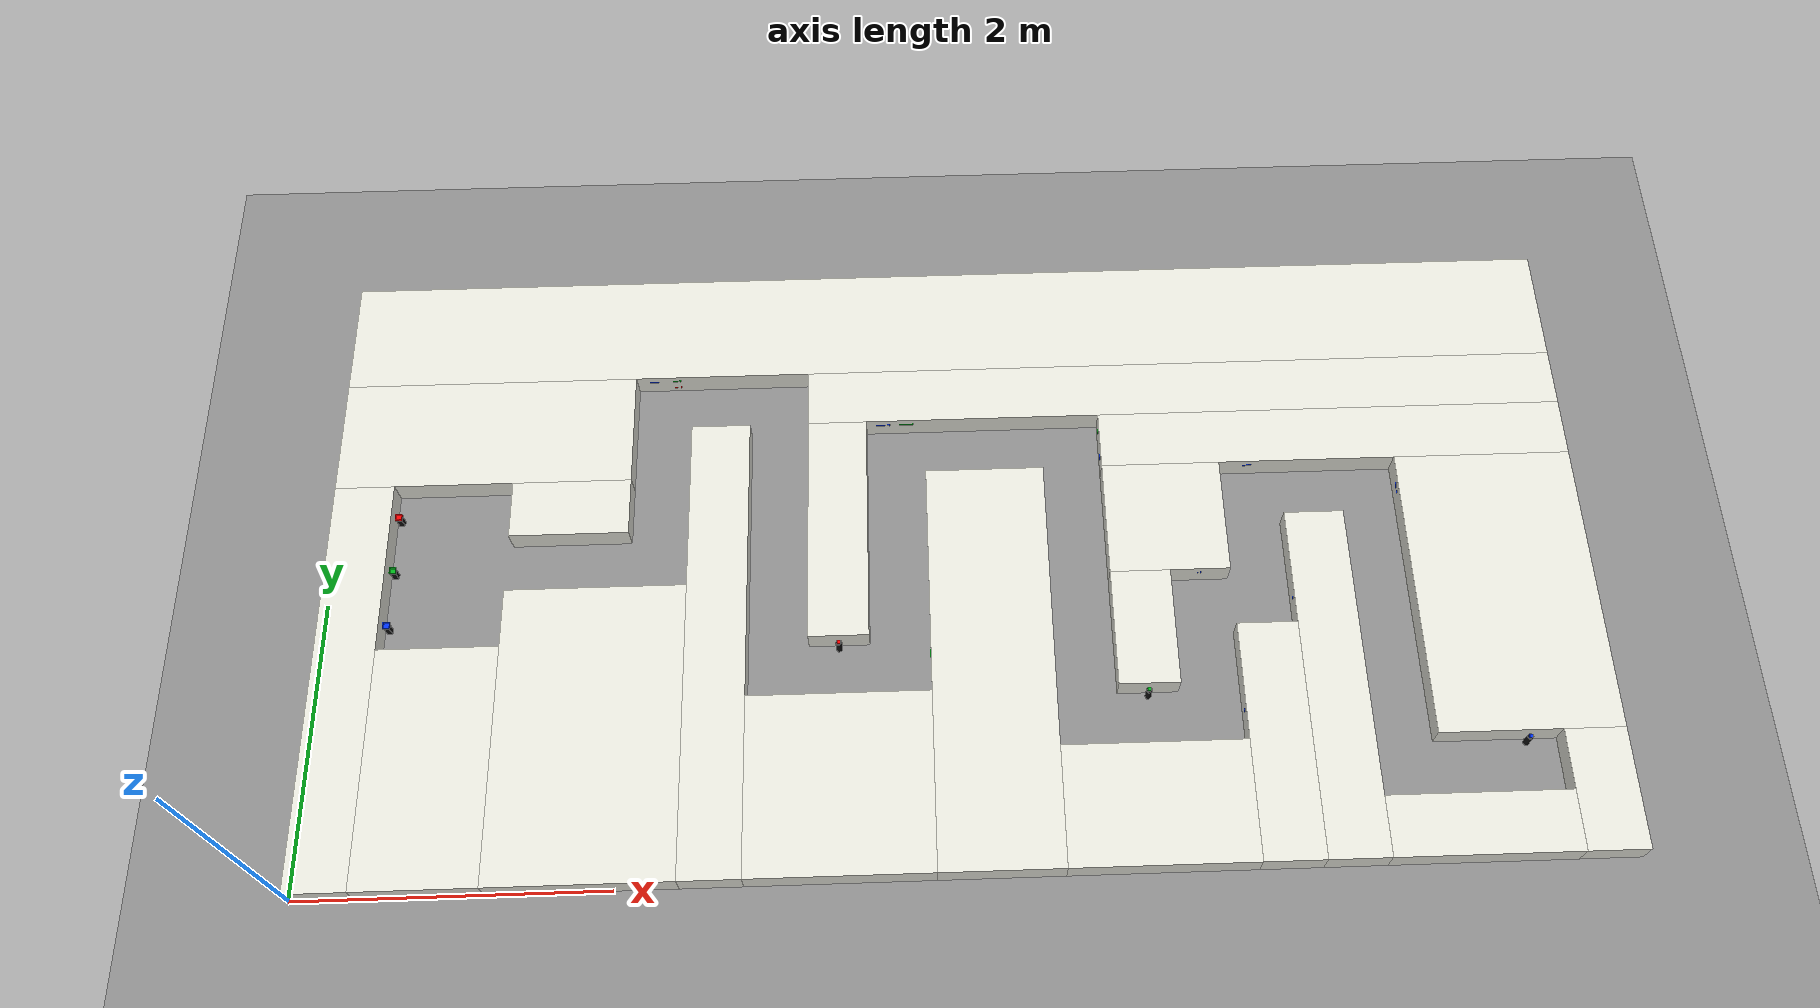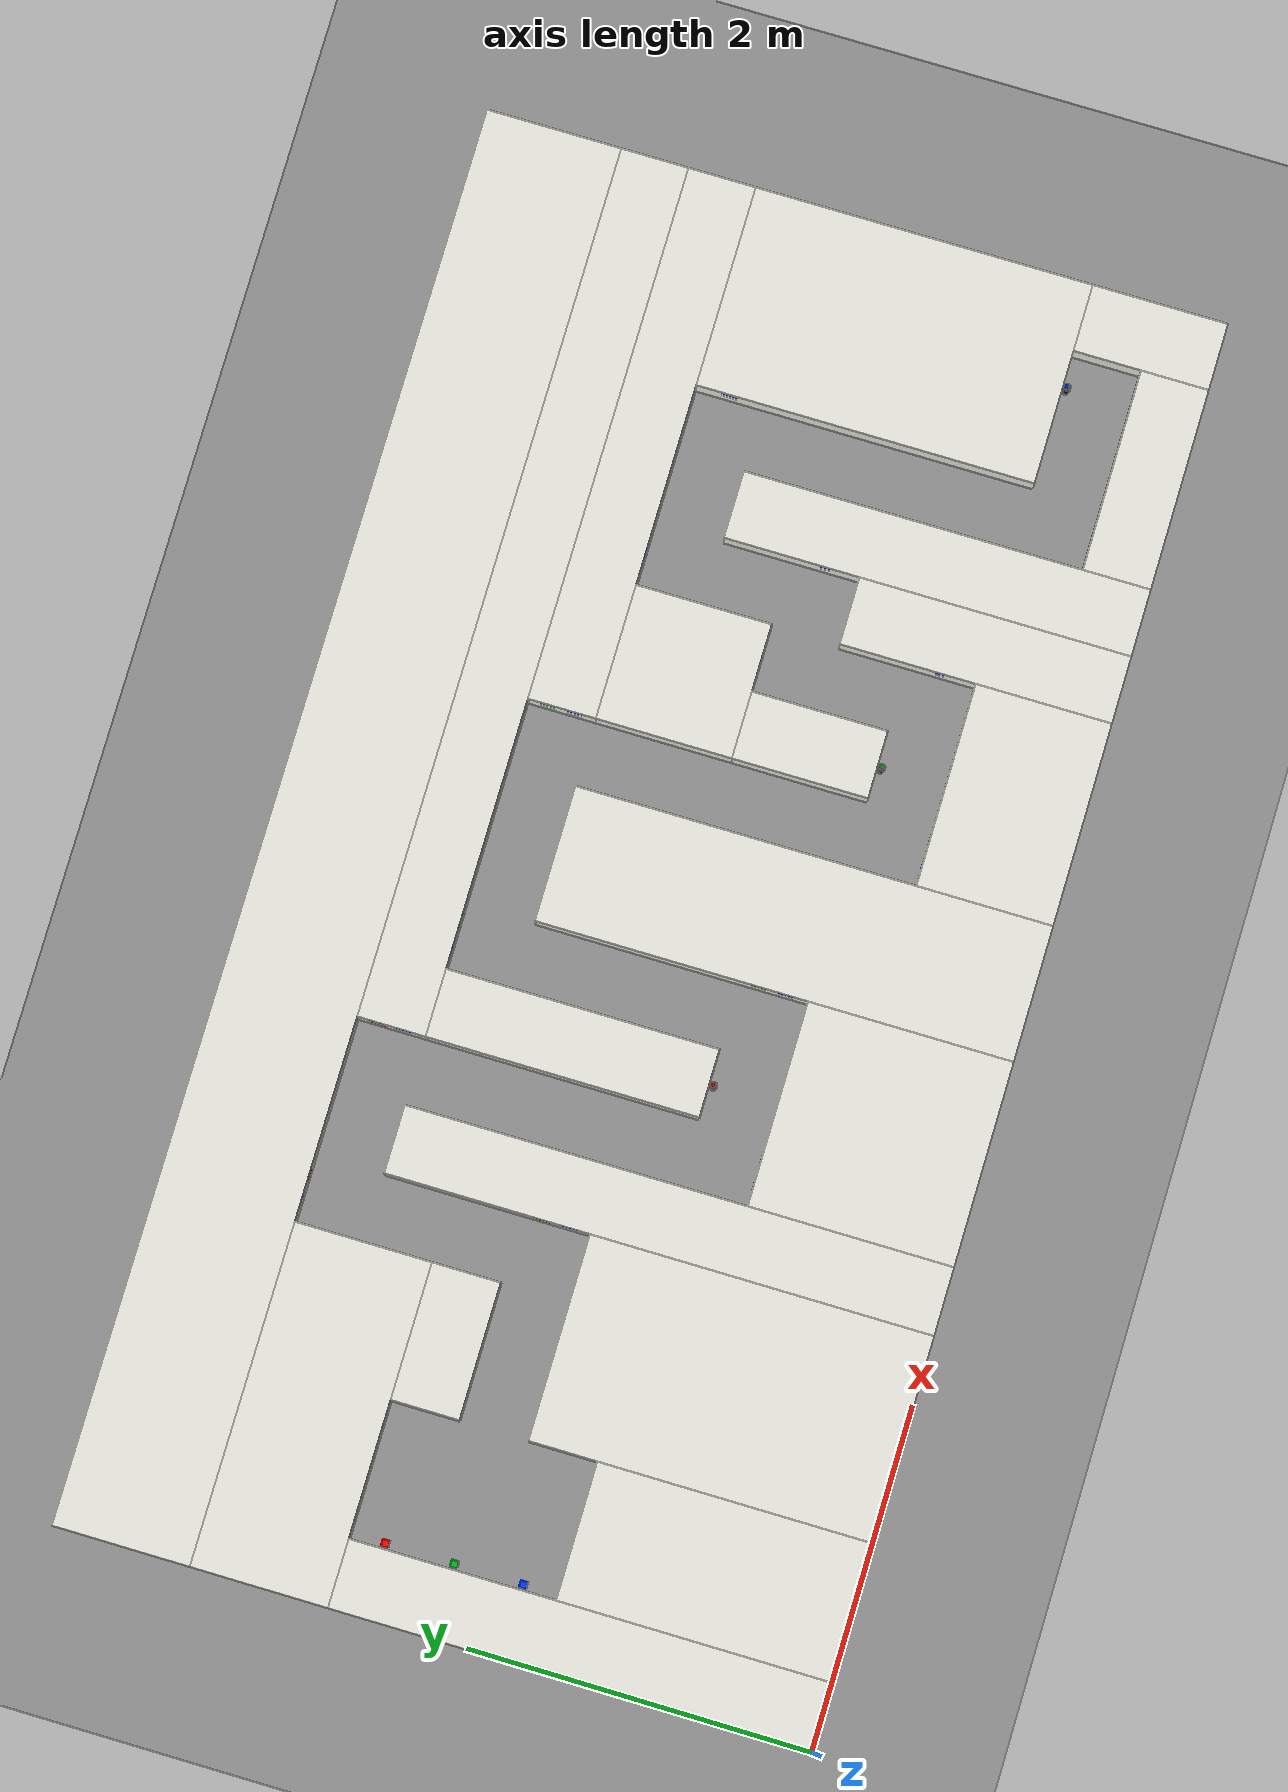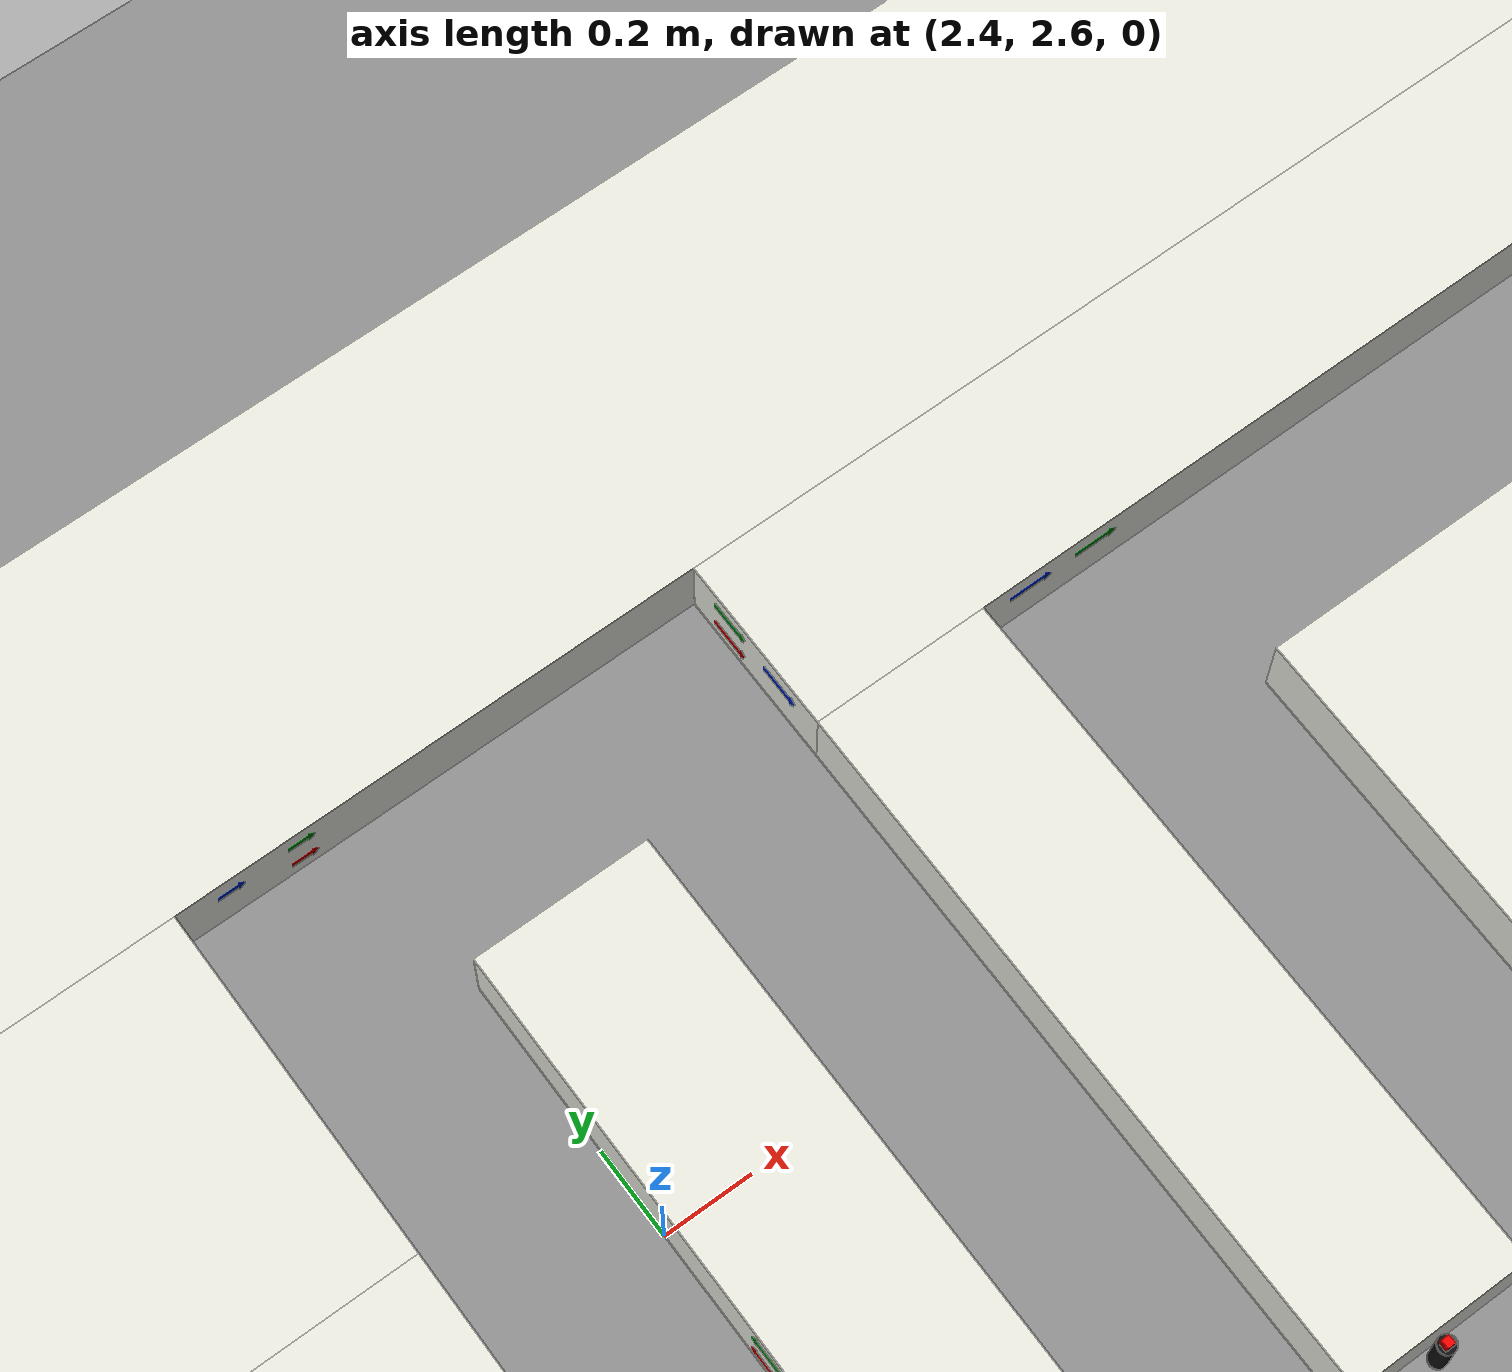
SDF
<?xml version="1.0"?>
<!-- Generado por gen_maze.py a partir de mazes/e1_serpentina_simple.yaml. No editar a mano: editar el YAML y regenerar. -->
<!-- E1 Serpentina: curvas y largos de flecha (simple: sin flechas laterales ni zonas) -->
<!-- Inicio del robot: x=1 y=2.2 yaw=0 -->
<sdf version="1.9">
  <world name="ros2_world">

    <plugin filename="gz-sim-physics-system"
            name="gz::sim::systems::Physics"/>

    <plugin filename="gz-sim-user-commands-system"
            name="gz::sim::systems::UserCommands"/>

    <plugin filename="gz-sim-scene-broadcaster-system"
            name="gz::sim::systems::SceneBroadcaster"/>

    <plugin filename="gz-sim-sensors-system"
            name="gz::sim::systems::Sensors">
      <render_engine>ogre2</render_engine>
    </plugin>

    <light type="directional" name="sun">
      <pose>0 0 10 0 0 0</pose>
      <diffuse>0.8 0.8 0.8 1</diffuse>
      <specular>0.2 0.2 0.2 1</specular>
      <direction>-0.5 0.1 -0.9</direction>
    </light>

    <model name="ground_plane">
      <static>true</static>
      <link name="link">
        <collision name="collision">
          <geometry>
            <plane>
              <normal>0 0 1</normal>
              <size>30 30</size>
            </plane>
          </geometry>
        </collision>
        <visual name="visual">
          <geometry>
            <plane>
              <normal>0 0 1</normal>
              <size>30 30</size>
            </plane>
          </geometry>
          <material>
            <ambient>0.55 0.55 0.55 1</ambient>
            <diffuse>0.55 0.55 0.55 1</diffuse>
          </material>
        </visual>
      </link>
    </model>

    <model name="paredes">
      <static>true</static>
      <link name="bloque_0">
        <pose>4.2 4 0.085 0 0 0</pose>
        <collision name="colision">
          <pose>0 0 0 0 0 0</pose>
          <geometry><box><size>8.4 0.8 0.17</size></box></geometry>
        </collision>
        <visual name="visual">
          <pose>0 0 0 0 0 0</pose>
          <geometry><box><size>8.4 0.8 0.17</size></box></geometry>
          <material>
            <ambient>0.9 0.9 0.86 1</ambient>
            <diffuse>0.9 0.9 0.86 1</diffuse>
          </material>
        </visual>
      </link>
      <link name="bloque_1">
        <pose>1 3.2 0.085 0 0 0</pose>
        <collision name="colision">
          <pose>0 0 0 0 0 0</pose>
          <geometry><box><size>2 0.8 0.17</size></box></geometry>
        </collision>
        <visual name="visual">
          <pose>0 0 0 0 0 0</pose>
          <geometry><box><size>2 0.8 0.17</size></box></geometry>
          <material>
            <ambient>0.9 0.9 0.86 1</ambient>
            <diffuse>0.9 0.9 0.86 1</diffuse>
          </material>
        </visual>
      </link>
      <link name="bloque_2">
        <pose>5.8 3.4 0.085 0 0 0</pose>
        <collision name="colision">
          <pose>0 0 0 0 0 0</pose>
          <geometry><box><size>5.2 0.4 0.17</size></box></geometry>
        </collision>
        <visual name="visual">
          <pose>0 0 0 0 0 0</pose>
          <geometry><box><size>5.2 0.4 0.17</size></box></geometry>
          <material>
            <ambient>0.9 0.9 0.86 1</ambient>
            <diffuse>0.9 0.9 0.86 1</diffuse>
          </material>
        </visual>
      </link>
      <link name="bloque_3">
        <pose>2.6 1.6 0.085 0 0 0</pose>
        <collision name="colision">
          <pose>0 0 0 0 0 0</pose>
          <geometry><box><size>0.4 3.2 0.17</size></box></geometry>
        </collision>
        <visual name="visual">
          <pose>0 0 0 0 0 0</pose>
          <geometry><box><size>0.4 3.2 0.17</size></box></geometry>
          <material>
            <ambient>0.9 0.9 0.86 1</ambient>
            <diffuse>0.9 0.9 0.86 1</diffuse>
          </material>
        </visual>
      </link>
      <link name="bloque_4">
        <pose>3.4 2.4 0.085 0 0 0</pose>
        <collision name="colision">
          <pose>0 0 0 0 0 0</pose>
          <geometry><box><size>0.4 1.6 0.17</size></box></geometry>
        </collision>
        <visual name="visual">
          <pose>0 0 0 0 0 0</pose>
          <geometry><box><size>0.4 1.6 0.17</size></box></geometry>
          <material>
            <ambient>0.9 0.9 0.86 1</ambient>
            <diffuse>0.9 0.9 0.86 1</diffuse>
          </material>
        </visual>
      </link>
      <link name="bloque_5">
        <pose>6.8 3 0.085 0 0 0</pose>
        <collision name="colision">
          <pose>0 0 0 0 0 0</pose>
          <geometry><box><size>3.2 0.4 0.17</size></box></geometry>
        </collision>
        <visual name="visual">
          <pose>0 0 0 0 0 0</pose>
          <geometry><box><size>3.2 0.4 0.17</size></box></geometry>
          <material>
            <ambient>0.9 0.9 0.86 1</ambient>
            <diffuse>0.9 0.9 0.86 1</diffuse>
          </material>
        </visual>
      </link>
      <link name="bloque_6">
        <pose>0.2 1.4 0.085 0 0 0</pose>
        <collision name="colision">
          <pose>0 0 0 0 0 0</pose>
          <geometry><box><size>0.4 2.8 0.17</size></box></geometry>
        </collision>
        <visual name="visual">
          <pose>0 0 0 0 0 0</pose>
          <geometry><box><size>0.4 2.8 0.17</size></box></geometry>
          <material>
            <ambient>0.9 0.9 0.86 1</ambient>
            <diffuse>0.9 0.9 0.86 1</diffuse>
          </material>
        </visual>
      </link>
      <link name="bloque_7">
        <pose>1.6 2.6 0.085 0 0 0</pose>
        <collision name="colision">
          <pose>0 0 0 0 0 0</pose>
          <geometry><box><size>0.8 0.4 0.17</size></box></geometry>
        </collision>
        <visual name="visual">
          <pose>0 0 0 0 0 0</pose>
          <geometry><box><size>0.8 0.4 0.17</size></box></geometry>
          <material>
            <ambient>0.9 0.9 0.86 1</ambient>
            <diffuse>0.9 0.9 0.86 1</diffuse>
          </material>
        </visual>
      </link>
      <link name="bloque_8">
        <pose>4.4 1.4 0.085 0 0 0</pose>
        <collision name="colision">
          <pose>0 0 0 0 0 0</pose>
          <geometry><box><size>0.8 2.8 0.17</size></box></geometry>
        </collision>
        <visual name="visual">
          <pose>0 0 0 0 0 0</pose>
          <geometry><box><size>0.8 2.8 0.17</size></box></geometry>
          <material>
            <ambient>0.9 0.9 0.86 1</ambient>
            <diffuse>0.9 0.9 0.86 1</diffuse>
          </material>
        </visual>
      </link>
      <link name="bloque_9">
        <pose>5.6 2.4 0.085 0 0 0</pose>
        <collision name="colision">
          <pose>0 0 0 0 0 0</pose>
          <geometry><box><size>0.8 0.8 0.17</size></box></geometry>
        </collision>
        <visual name="visual">
          <pose>0 0 0 0 0 0</pose>
          <geometry><box><size>0.8 0.8 0.17</size></box></geometry>
          <material>
            <ambient>0.9 0.9 0.86 1</ambient>
            <diffuse>0.9 0.9 0.86 1</diffuse>
          </material>
        </visual>
      </link>
      <link name="bloque_10">
        <pose>7.8 1.8 0.085 0 0 0</pose>
        <collision name="colision">
          <pose>0 0 0 0 0 0</pose>
          <geometry><box><size>1.2 2 0.17</size></box></geometry>
        </collision>
        <visual name="visual">
          <pose>0 0 0 0 0 0</pose>
          <geometry><box><size>1.2 2 0.17</size></box></geometry>
          <material>
            <ambient>0.9 0.9 0.86 1</ambient>
            <diffuse>0.9 0.9 0.86 1</diffuse>
          </material>
        </visual>
      </link>
      <link name="bloque_11">
        <pose>6.6 1.2 0.085 0 0 0</pose>
        <collision name="colision">
          <pose>0 0 0 0 0 0</pose>
          <geometry><box><size>0.4 2.4 0.17</size></box></geometry>
        </collision>
        <visual name="visual">
          <pose>0 0 0 0 0 0</pose>
          <geometry><box><size>0.4 2.4 0.17</size></box></geometry>
          <material>
            <ambient>0.9 0.9 0.86 1</ambient>
            <diffuse>0.9 0.9 0.86 1</diffuse>
          </material>
        </visual>
      </link>
      <link name="bloque_12">
        <pose>1.8 1 0.085 0 0 0</pose>
        <collision name="colision">
          <pose>0 0 0 0 0 0</pose>
          <geometry><box><size>1.2 2 0.17</size></box></geometry>
        </collision>
        <visual name="visual">
          <pose>0 0 0 0 0 0</pose>
          <geometry><box><size>1.2 2 0.17</size></box></geometry>
          <material>
            <ambient>0.9 0.9 0.86 1</ambient>
            <diffuse>0.9 0.9 0.86 1</diffuse>
          </material>
        </visual>
      </link>
      <link name="bloque_13">
        <pose>5.4 1.6 0.085 0 0 0</pose>
        <collision name="colision">
          <pose>0 0 0 0 0 0</pose>
          <geometry><box><size>0.4 0.8 0.17</size></box></geometry>
        </collision>
        <visual name="visual">
          <pose>0 0 0 0 0 0</pose>
          <geometry><box><size>0.4 0.8 0.17</size></box></geometry>
          <material>
            <ambient>0.9 0.9 0.86 1</ambient>
            <diffuse>0.9 0.9 0.86 1</diffuse>
          </material>
        </visual>
      </link>
      <link name="bloque_14">
        <pose>0.8 0.8 0.085 0 0 0</pose>
        <collision name="colision">
          <pose>0 0 0 0 0 0</pose>
          <geometry><box><size>0.8 1.6 0.17</size></box></geometry>
        </collision>
        <visual name="visual">
          <pose>0 0 0 0 0 0</pose>
          <geometry><box><size>0.8 1.6 0.17</size></box></geometry>
          <material>
            <ambient>0.9 0.9 0.86 1</ambient>
            <diffuse>0.9 0.9 0.86 1</diffuse>
          </material>
        </visual>
      </link>
      <link name="bloque_15">
        <pose>6.2 0.8 0.085 0 0 0</pose>
        <collision name="colision">
          <pose>0 0 0 0 0 0</pose>
          <geometry><box><size>0.4 1.6 0.17</size></box></geometry>
        </collision>
        <visual name="visual">
          <pose>0 0 0 0 0 0</pose>
          <geometry><box><size>0.4 1.6 0.17</size></box></geometry>
          <material>
            <ambient>0.9 0.9 0.86 1</ambient>
            <diffuse>0.9 0.9 0.86 1</diffuse>
          </material>
        </visual>
      </link>
      <link name="bloque_16">
        <pose>3.4 0.6 0.085 0 0 0</pose>
        <collision name="colision">
          <pose>0 0 0 0 0 0</pose>
          <geometry><box><size>1.2 1.2 0.17</size></box></geometry>
        </collision>
        <visual name="visual">
          <pose>0 0 0 0 0 0</pose>
          <geometry><box><size>1.2 1.2 0.17</size></box></geometry>
          <material>
            <ambient>0.9 0.9 0.86 1</ambient>
            <diffuse>0.9 0.9 0.86 1</diffuse>
          </material>
        </visual>
      </link>
      <link name="bloque_17">
        <pose>5.4 0.4 0.085 0 0 0</pose>
        <collision name="colision">
          <pose>0 0 0 0 0 0</pose>
          <geometry><box><size>1.2 0.8 0.17</size></box></geometry>
        </collision>
        <visual name="visual">
          <pose>0 0 0 0 0 0</pose>
          <geometry><box><size>1.2 0.8 0.17</size></box></geometry>
          <material>
            <ambient>0.9 0.9 0.86 1</ambient>
            <diffuse>0.9 0.9 0.86 1</diffuse>
          </material>
        </visual>
      </link>
      <link name="bloque_18">
        <pose>8.2 0.4 0.085 0 0 0</pose>
        <collision name="colision">
          <pose>0 0 0 0 0 0</pose>
          <geometry><box><size>0.4 0.8 0.17</size></box></geometry>
        </collision>
        <visual name="visual">
          <pose>0 0 0 0 0 0</pose>
          <geometry><box><size>0.4 0.8 0.17</size></box></geometry>
          <material>
            <ambient>0.9 0.9 0.86 1</ambient>
            <diffuse>0.9 0.9 0.86 1</diffuse>
          </material>
        </visual>
      </link>
      <link name="bloque_19">
        <pose>7.4 0.2 0.085 0 0 0</pose>
        <collision name="colision">
          <pose>0 0 0 0 0 0</pose>
          <geometry><box><size>1.2 0.4 0.17</size></box></geometry>
        </collision>
        <visual name="visual">
          <pose>0 0 0 0 0 0</pose>
          <geometry><box><size>1.2 0.4 0.17</size></box></geometry>
          <material>
            <ambient>0.9 0.9 0.86 1</ambient>
            <diffuse>0.9 0.9 0.86 1</diffuse>
          </material>
        </visual>
      </link>
    </model>

    <model name="flechas">
      <static>true</static>
      <link name="flecha_0">
        <pose>2.12 3.59875 0.115 0 0 0</pose>
        <visual name="p0">
          <pose>-0.0065 0 0 0 0 0</pose>
          <geometry><box><size>0.047 0.0015 0.01</size></box></geometry>
          <material>
            <ambient>0 0.2 1 1</ambient>
            <diffuse>0 0.2 1 1</diffuse>
          </material>
        </visual>
        <visual name="p1">
          <pose>0.01726 0 0 0 0 0</pose>
          <geometry><box><size>0.00052 0.0015 0.029</size></box></geometry>
          <material>
            <ambient>0 0.2 1 1</ambient>
            <diffuse>0 0.2 1 1</diffuse>
          </material>
        </visual>
        <visual name="p2">
          <pose>0.01778 0 0 0 0 0</pose>
          <geometry><box><size>0.00052 0.0015 0.02784</size></box></geometry>
          <material>
            <ambient>0 0.2 1 1</ambient>
            <diffuse>0 0.2 1 1</diffuse>
          </material>
        </visual>
        <visual name="p3">
          <pose>0.0183 0 0 0 0 0</pose>
          <geometry><box><size>0.00052 0.0015 0.02668</size></box></geometry>
          <material>
            <ambient>0 0.2 1 1</ambient>
            <diffuse>0 0.2 1 1</diffuse>
          </material>
        </visual>
        <visual name="p4">
          <pose>0.01882 0 0 0 0 0</pose>
          <geometry><box><size>0.00052 0.0015 0.02552</size></box></geometry>
          <material>
            <ambient>0 0.2 1 1</ambient>
            <diffuse>0 0.2 1 1</diffuse>
          </material>
        </visual>
        <visual name="p5">
          <pose>0.01934 0 0 0 0 0</pose>
          <geometry><box><size>0.00052 0.0015 0.02436</size></box></geometry>
          <material>
            <ambient>0 0.2 1 1</ambient>
            <diffuse>0 0.2 1 1</diffuse>
          </material>
        </visual>
        <visual name="p6">
          <pose>0.01986 0 0 0 0 0</pose>
          <geometry><box><size>0.00052 0.0015 0.0232</size></box></geometry>
          <material>
            <ambient>0 0.2 1 1</ambient>
            <diffuse>0 0.2 1 1</diffuse>
          </material>
        </visual>
        <visual name="p7">
          <pose>0.02038 0 0 0 0 0</pose>
          <geometry><box><size>0.00052 0.0015 0.02204</size></box></geometry>
          <material>
            <ambient>0 0.2 1 1</ambient>
            <diffuse>0 0.2 1 1</diffuse>
          </material>
        </visual>
        <visual name="p8">
          <pose>0.0209 0 0 0 0 0</pose>
          <geometry><box><size>0.00052 0.0015 0.02088</size></box></geometry>
          <material>
            <ambient>0 0.2 1 1</ambient>
            <diffuse>0 0.2 1 1</diffuse>
          </material>
        </visual>
        <visual name="p9">
          <pose>0.02142 0 0 0 0 0</pose>
          <geometry><box><size>0.00052 0.0015 0.01972</size></box></geometry>
          <material>
            <ambient>0 0.2 1 1</ambient>
            <diffuse>0 0.2 1 1</diffuse>
          </material>
        </visual>
        <visual name="p10">
          <pose>0.02194 0 0 0 0 0</pose>
          <geometry><box><size>0.00052 0.0015 0.01856</size></box></geometry>
          <material>
            <ambient>0 0.2 1 1</ambient>
            <diffuse>0 0.2 1 1</diffuse>
          </material>
        </visual>
        <visual name="p11">
          <pose>0.02246 0 0 0 0 0</pose>
          <geometry><box><size>0.00052 0.0015 0.0174</size></box></geometry>
          <material>
            <ambient>0 0.2 1 1</ambient>
            <diffuse>0 0.2 1 1</diffuse>
          </material>
        </visual>
        <visual name="p12">
          <pose>0.02298 0 0 0 0 0</pose>
          <geometry><box><size>0.00052 0.0015 0.01624</size></box></geometry>
          <material>
            <ambient>0 0.2 1 1</ambient>
            <diffuse>0 0.2 1 1</diffuse>
          </material>
        </visual>
        <visual name="p13">
          <pose>0.0235 0 0 0 0 0</pose>
          <geometry><box><size>0.00052 0.0015 0.01508</size></box></geometry>
          <material>
            <ambient>0 0.2 1 1</ambient>
            <diffuse>0 0.2 1 1</diffuse>
          </material>
        </visual>
        <visual name="p14">
          <pose>0.02402 0 0 0 0 0</pose>
          <geometry><box><size>0.00052 0.0015 0.01392</size></box></geometry>
          <material>
            <ambient>0 0.2 1 1</ambient>
            <diffuse>0 0.2 1 1</diffuse>
          </material>
        </visual>
        <visual name="p15">
          <pose>0.02454 0 0 0 0 0</pose>
          <geometry><box><size>0.00052 0.0015 0.01276</size></box></geometry>
          <material>
            <ambient>0 0.2 1 1</ambient>
            <diffuse>0 0.2 1 1</diffuse>
          </material>
        </visual>
        <visual name="p16">
          <pose>0.02506 0 0 0 0 0</pose>
          <geometry><box><size>0.00052 0.0015 0.0116</size></box></geometry>
          <material>
            <ambient>0 0.2 1 1</ambient>
            <diffuse>0 0.2 1 1</diffuse>
          </material>
        </visual>
        <visual name="p17">
          <pose>0.02558 0 0 0 0 0</pose>
          <geometry><box><size>0.00052 0.0015 0.01044</size></box></geometry>
          <material>
            <ambient>0 0.2 1 1</ambient>
            <diffuse>0 0.2 1 1</diffuse>
          </material>
        </visual>
        <visual name="p18">
          <pose>0.0261 0 0 0 0 0</pose>
          <geometry><box><size>0.00052 0.0015 0.00928</size></box></geometry>
          <material>
            <ambient>0 0.2 1 1</ambient>
            <diffuse>0 0.2 1 1</diffuse>
          </material>
        </visual>
        <visual name="p19">
          <pose>0.02662 0 0 0 0 0</pose>
          <geometry><box><size>0.00052 0.0015 0.00812</size></box></geometry>
          <material>
            <ambient>0 0.2 1 1</ambient>
            <diffuse>0 0.2 1 1</diffuse>
          </material>
        </visual>
        <visual name="p20">
          <pose>0.02714 0 0 0 0 0</pose>
          <geometry><box><size>0.00052 0.0015 0.00696</size></box></geometry>
          <material>
            <ambient>0 0.2 1 1</ambient>
            <diffuse>0 0.2 1 1</diffuse>
          </material>
        </visual>
        <visual name="p21">
          <pose>0.02766 0 0 0 0 0</pose>
          <geometry><box><size>0.00052 0.0015 0.0058</size></box></geometry>
          <material>
            <ambient>0 0.2 1 1</ambient>
            <diffuse>0 0.2 1 1</diffuse>
          </material>
        </visual>
        <visual name="p22">
          <pose>0.02818 0 0 0 0 0</pose>
          <geometry><box><size>0.00052 0.0015 0.00464</size></box></geometry>
          <material>
            <ambient>0 0.2 1 1</ambient>
            <diffuse>0 0.2 1 1</diffuse>
          </material>
        </visual>
        <visual name="p23">
          <pose>0.0287 0 0 0 0 0</pose>
          <geometry><box><size>0.00052 0.0015 0.00348</size></box></geometry>
          <material>
            <ambient>0 0.2 1 1</ambient>
            <diffuse>0 0.2 1 1</diffuse>
          </material>
        </visual>
        <visual name="p24">
          <pose>0.02922 0 0 0 0 0</pose>
          <geometry><box><size>0.00052 0.0015 0.00232</size></box></geometry>
          <material>
            <ambient>0 0.2 1 1</ambient>
            <diffuse>0 0.2 1 1</diffuse>
          </material>
        </visual>
        <visual name="p25">
          <pose>0.02974 0 0 0 0 0</pose>
          <geometry><box><size>0.00052 0.0015 0.00116</size></box></geometry>
          <material>
            <ambient>0 0.2 1 1</ambient>
            <diffuse>0 0.2 1 1</diffuse>
          </material>
        </visual>
      </link>
      <link name="flecha_1">
        <pose>2.28 3.59875 0.125 0 0 0</pose>
        <visual name="p0">
          <pose>-0.0065 0 0 0 0 0</pose>
          <geometry><box><size>0.047 0.0015 0.01</size></box></geometry>
          <material>
            <ambient>0 0.7 0.1 1</ambient>
            <diffuse>0 0.7 0.1 1</diffuse>
          </material>
        </visual>
        <visual name="p1">
          <pose>0.01726 0 0 0 0 0</pose>
          <geometry><box><size>0.00052 0.0015 0.029</size></box></geometry>
          <material>
            <ambient>0 0.7 0.1 1</ambient>
            <diffuse>0 0.7 0.1 1</diffuse>
          </material>
        </visual>
        <visual name="p2">
          <pose>0.01778 0 0 0 0 0</pose>
          <geometry><box><size>0.00052 0.0015 0.02784</size></box></geometry>
          <material>
            <ambient>0 0.7 0.1 1</ambient>
            <diffuse>0 0.7 0.1 1</diffuse>
          </material>
        </visual>
        <visual name="p3">
          <pose>0.0183 0 0 0 0 0</pose>
          <geometry><box><size>0.00052 0.0015 0.02668</size></box></geometry>
          <material>
            <ambient>0 0.7 0.1 1</ambient>
            <diffuse>0 0.7 0.1 1</diffuse>
          </material>
        </visual>
        <visual name="p4">
          <pose>0.01882 0 0 0 0 0</pose>
          <geometry><box><size>0.00052 0.0015 0.02552</size></box></geometry>
          <material>
            <ambient>0 0.7 0.1 1</ambient>
            <diffuse>0 0.7 0.1 1</diffuse>
          </material>
        </visual>
        <visual name="p5">
          <pose>0.01934 0 0 0 0 0</pose>
          <geometry><box><size>0.00052 0.0015 0.02436</size></box></geometry>
          <material>
            <ambient>0 0.7 0.1 1</ambient>
            <diffuse>0 0.7 0.1 1</diffuse>
          </material>
        </visual>
        <visual name="p6">
          <pose>0.01986 0 0 0 0 0</pose>
          <geometry><box><size>0.00052 0.0015 0.0232</size></box></geometry>
          <material>
            <ambient>0 0.7 0.1 1</ambient>
            <diffuse>0 0.7 0.1 1</diffuse>
          </material>
        </visual>
        <visual name="p7">
          <pose>0.02038 0 0 0 0 0</pose>
          <geometry><box><size>0.00052 0.0015 0.02204</size></box></geometry>
          <material>
            <ambient>0 0.7 0.1 1</ambient>
            <diffuse>0 0.7 0.1 1</diffuse>
          </material>
        </visual>
        <visual name="p8">
          <pose>0.0209 0 0 0 0 0</pose>
          <geometry><box><size>0.00052 0.0015 0.02088</size></box></geometry>
          <material>
            <ambient>0 0.7 0.1 1</ambient>
            <diffuse>0 0.7 0.1 1</diffuse>
          </material>
        </visual>
        <visual name="p9">
          <pose>0.02142 0 0 0 0 0</pose>
          <geometry><box><size>0.00052 0.0015 0.01972</size></box></geometry>
          <material>
            <ambient>0 0.7 0.1 1</ambient>
            <diffuse>0 0.7 0.1 1</diffuse>
          </material>
        </visual>
        <visual name="p10">
          <pose>0.02194 0 0 0 0 0</pose>
          <geometry><box><size>0.00052 0.0015 0.01856</size></box></geometry>
          <material>
            <ambient>0 0.7 0.1 1</ambient>
            <diffuse>0 0.7 0.1 1</diffuse>
          </material>
        </visual>
        <visual name="p11">
          <pose>0.02246 0 0 0 0 0</pose>
          <geometry><box><size>0.00052 0.0015 0.0174</size></box></geometry>
          <material>
            <ambient>0 0.7 0.1 1</ambient>
            <diffuse>0 0.7 0.1 1</diffuse>
          </material>
        </visual>
        <visual name="p12">
          <pose>0.02298 0 0 0 0 0</pose>
          <geometry><box><size>0.00052 0.0015 0.01624</size></box></geometry>
          <material>
            <ambient>0 0.7 0.1 1</ambient>
            <diffuse>0 0.7 0.1 1</diffuse>
          </material>
        </visual>
        <visual name="p13">
          <pose>0.0235 0 0 0 0 0</pose>
          <geometry><box><size>0.00052 0.0015 0.01508</size></box></geometry>
          <material>
            <ambient>0 0.7 0.1 1</ambient>
            <diffuse>0 0.7 0.1 1</diffuse>
          </material>
        </visual>
        <visual name="p14">
          <pose>0.02402 0 0 0 0 0</pose>
          <geometry><box><size>0.00052 0.0015 0.01392</size></box></geometry>
          <material>
            <ambient>0 0.7 0.1 1</ambient>
            <diffuse>0 0.7 0.1 1</diffuse>
          </material>
        </visual>
        <visual name="p15">
          <pose>0.02454 0 0 0 0 0</pose>
          <geometry><box><size>0.00052 0.0015 0.01276</size></box></geometry>
          <material>
            <ambient>0 0.7 0.1 1</ambient>
            <diffuse>0 0.7 0.1 1</diffuse>
          </material>
        </visual>
        <visual name="p16">
          <pose>0.02506 0 0 0 0 0</pose>
          <geometry><box><size>0.00052 0.0015 0.0116</size></box></geometry>
          <material>
            <ambient>0 0.7 0.1 1</ambient>
            <diffuse>0 0.7 0.1 1</diffuse>
          </material>
        </visual>
        <visual name="p17">
          <pose>0.02558 0 0 0 0 0</pose>
          <geometry><box><size>0.00052 0.0015 0.01044</size></box></geometry>
          <material>
            <ambient>0 0.7 0.1 1</ambient>
            <diffuse>0 0.7 0.1 1</diffuse>
          </material>
        </visual>
        <visual name="p18">
          <pose>0.0261 0 0 0 0 0</pose>
          <geometry><box><size>0.00052 0.0015 0.00928</size></box></geometry>
          <material>
            <ambient>0 0.7 0.1 1</ambient>
            <diffuse>0 0.7 0.1 1</diffuse>
          </material>
        </visual>
        <visual name="p19">
          <pose>0.02662 0 0 0 0 0</pose>
          <geometry><box><size>0.00052 0.0015 0.00812</size></box></geometry>
          <material>
            <ambient>0 0.7 0.1 1</ambient>
            <diffuse>0 0.7 0.1 1</diffuse>
          </material>
        </visual>
        <visual name="p20">
          <pose>0.02714 0 0 0 0 0</pose>
          <geometry><box><size>0.00052 0.0015 0.00696</size></box></geometry>
          <material>
            <ambient>0 0.7 0.1 1</ambient>
            <diffuse>0 0.7 0.1 1</diffuse>
          </material>
        </visual>
        <visual name="p21">
          <pose>0.02766 0 0 0 0 0</pose>
          <geometry><box><size>0.00052 0.0015 0.0058</size></box></geometry>
          <material>
            <ambient>0 0.7 0.1 1</ambient>
            <diffuse>0 0.7 0.1 1</diffuse>
          </material>
        </visual>
        <visual name="p22">
          <pose>0.02818 0 0 0 0 0</pose>
          <geometry><box><size>0.00052 0.0015 0.00464</size></box></geometry>
          <material>
            <ambient>0 0.7 0.1 1</ambient>
            <diffuse>0 0.7 0.1 1</diffuse>
          </material>
        </visual>
        <visual name="p23">
          <pose>0.0287 0 0 0 0 0</pose>
          <geometry><box><size>0.00052 0.0015 0.00348</size></box></geometry>
          <material>
            <ambient>0 0.7 0.1 1</ambient>
            <diffuse>0 0.7 0.1 1</diffuse>
          </material>
        </visual>
        <visual name="p24">
          <pose>0.02922 0 0 0 0 0</pose>
          <geometry><box><size>0.00052 0.0015 0.00232</size></box></geometry>
          <material>
            <ambient>0 0.7 0.1 1</ambient>
            <diffuse>0 0.7 0.1 1</diffuse>
          </material>
        </visual>
        <visual name="p25">
          <pose>0.02974 0 0 0 0 0</pose>
          <geometry><box><size>0.00052 0.0015 0.00116</size></box></geometry>
          <material>
            <ambient>0 0.7 0.1 1</ambient>
            <diffuse>0 0.7 0.1 1</diffuse>
          </material>
        </visual>
      </link>
      <link name="flecha_2">
        <pose>2.28 3.59875 0.045 0 0 0</pose>
        <visual name="p0">
          <pose>-0.0065 0 0 0 0 0</pose>
          <geometry><box><size>0.047 0.0015 0.01</size></box></geometry>
          <material>
            <ambient>1 0 0 1</ambient>
            <diffuse>1 0 0 1</diffuse>
          </material>
        </visual>
        <visual name="p1">
          <pose>0.01726 0 0 0 0 0</pose>
          <geometry><box><size>0.00052 0.0015 0.029</size></box></geometry>
          <material>
            <ambient>1 0 0 1</ambient>
            <diffuse>1 0 0 1</diffuse>
          </material>
        </visual>
        <visual name="p2">
          <pose>0.01778 0 0 0 0 0</pose>
          <geometry><box><size>0.00052 0.0015 0.02784</size></box></geometry>
          <material>
            <ambient>1 0 0 1</ambient>
            <diffuse>1 0 0 1</diffuse>
          </material>
        </visual>
        <visual name="p3">
          <pose>0.0183 0 0 0 0 0</pose>
          <geometry><box><size>0.00052 0.0015 0.02668</size></box></geometry>
          <material>
            <ambient>1 0 0 1</ambient>
            <diffuse>1 0 0 1</diffuse>
          </material>
        </visual>
        <visual name="p4">
          <pose>0.01882 0 0 0 0 0</pose>
          <geometry><box><size>0.00052 0.0015 0.02552</size></box></geometry>
          <material>
            <ambient>1 0 0 1</ambient>
            <diffuse>1 0 0 1</diffuse>
          </material>
        </visual>
        <visual name="p5">
          <pose>0.01934 0 0 0 0 0</pose>
          <geometry><box><size>0.00052 0.0015 0.02436</size></box></geometry>
          <material>
            <ambient>1 0 0 1</ambient>
            <diffuse>1 0 0 1</diffuse>
          </material>
        </visual>
        <visual name="p6">
          <pose>0.01986 0 0 0 0 0</pose>
          <geometry><box><size>0.00052 0.0015 0.0232</size></box></geometry>
          <material>
            <ambient>1 0 0 1</ambient>
            <diffuse>1 0 0 1</diffuse>
          </material>
        </visual>
        <visual name="p7">
          <pose>0.02038 0 0 0 0 0</pose>
          <geometry><box><size>0.00052 0.0015 0.02204</size></box></geometry>
          <material>
            <ambient>1 0 0 1</ambient>
            <diffuse>1 0 0 1</diffuse>
          </material>
        </visual>
        <visual name="p8">
          <pose>0.0209 0 0 0 0 0</pose>
          <geometry><box><size>0.00052 0.0015 0.02088</size></box></geometry>
          <material>
            <ambient>1 0 0 1</ambient>
            <diffuse>1 0 0 1</diffuse>
          </material>
        </visual>
        <visual name="p9">
          <pose>0.02142 0 0 0 0 0</pose>
          <geometry><box><size>0.00052 0.0015 0.01972</size></box></geometry>
          <material>
            <ambient>1 0 0 1</ambient>
            <diffuse>1 0 0 1</diffuse>
          </material>
        </visual>
        <visual name="p10">
          <pose>0.02194 0 0 0 0 0</pose>
          <geometry><box><size>0.00052 0.0015 0.01856</size></box></geometry>
          <material>
            <ambient>1 0 0 1</ambient>
            <diffuse>1 0 0 1</diffuse>
          </material>
        </visual>
        <visual name="p11">
          <pose>0.02246 0 0 0 0 0</pose>
          <geometry><box><size>0.00052 0.0015 0.0174</size></box></geometry>
          <material>
            <ambient>1 0 0 1</ambient>
            <diffuse>1 0 0 1</diffuse>
          </material>
        </visual>
        <visual name="p12">
          <pose>0.02298 0 0 0 0 0</pose>
          <geometry><box><size>0.00052 0.0015 0.01624</size></box></geometry>
          <material>
            <ambient>1 0 0 1</ambient>
            <diffuse>1 0 0 1</diffuse>
          </material>
        </visual>
        <visual name="p13">
          <pose>0.0235 0 0 0 0 0</pose>
          <geometry><box><size>0.00052 0.0015 0.01508</size></box></geometry>
          <material>
            <ambient>1 0 0 1</ambient>
            <diffuse>1 0 0 1</diffuse>
          </material>
        </visual>
        <visual name="p14">
          <pose>0.02402 0 0 0 0 0</pose>
          <geometry><box><size>0.00052 0.0015 0.01392</size></box></geometry>
          <material>
            <ambient>1 0 0 1</ambient>
            <diffuse>1 0 0 1</diffuse>
          </material>
        </visual>
        <visual name="p15">
          <pose>0.02454 0 0 0 0 0</pose>
          <geometry><box><size>0.00052 0.0015 0.01276</size></box></geometry>
          <material>
            <ambient>1 0 0 1</ambient>
            <diffuse>1 0 0 1</diffuse>
          </material>
        </visual>
        <visual name="p16">
          <pose>0.02506 0 0 0 0 0</pose>
          <geometry><box><size>0.00052 0.0015 0.0116</size></box></geometry>
          <material>
            <ambient>1 0 0 1</ambient>
            <diffuse>1 0 0 1</diffuse>
          </material>
        </visual>
        <visual name="p17">
          <pose>0.02558 0 0 0 0 0</pose>
          <geometry><box><size>0.00052 0.0015 0.01044</size></box></geometry>
          <material>
            <ambient>1 0 0 1</ambient>
            <diffuse>1 0 0 1</diffuse>
          </material>
        </visual>
        <visual name="p18">
          <pose>0.0261 0 0 0 0 0</pose>
          <geometry><box><size>0.00052 0.0015 0.00928</size></box></geometry>
          <material>
            <ambient>1 0 0 1</ambient>
            <diffuse>1 0 0 1</diffuse>
          </material>
        </visual>
        <visual name="p19">
          <pose>0.02662 0 0 0 0 0</pose>
          <geometry><box><size>0.00052 0.0015 0.00812</size></box></geometry>
          <material>
            <ambient>1 0 0 1</ambient>
            <diffuse>1 0 0 1</diffuse>
          </material>
        </visual>
        <visual name="p20">
          <pose>0.02714 0 0 0 0 0</pose>
          <geometry><box><size>0.00052 0.0015 0.00696</size></box></geometry>
          <material>
            <ambient>1 0 0 1</ambient>
            <diffuse>1 0 0 1</diffuse>
          </material>
        </visual>
        <visual name="p21">
          <pose>0.02766 0 0 0 0 0</pose>
          <geometry><box><size>0.00052 0.0015 0.0058</size></box></geometry>
          <material>
            <ambient>1 0 0 1</ambient>
            <diffuse>1 0 0 1</diffuse>
          </material>
        </visual>
        <visual name="p22">
          <pose>0.02818 0 0 0 0 0</pose>
          <geometry><box><size>0.00052 0.0015 0.00464</size></box></geometry>
          <material>
            <ambient>1 0 0 1</ambient>
            <diffuse>1 0 0 1</diffuse>
          </material>
        </visual>
        <visual name="p23">
          <pose>0.0287 0 0 0 0 0</pose>
          <geometry><box><size>0.00052 0.0015 0.00348</size></box></geometry>
          <material>
            <ambient>1 0 0 1</ambient>
            <diffuse>1 0 0 1</diffuse>
          </material>
        </visual>
        <visual name="p24">
          <pose>0.02922 0 0 0 0 0</pose>
          <geometry><box><size>0.00052 0.0015 0.00232</size></box></geometry>
          <material>
            <ambient>1 0 0 1</ambient>
            <diffuse>1 0 0 1</diffuse>
          </material>
        </visual>
        <visual name="p25">
          <pose>0.02974 0 0 0 0 0</pose>
          <geometry><box><size>0.00052 0.0015 0.00116</size></box></geometry>
          <material>
            <ambient>1 0 0 1</ambient>
            <diffuse>1 0 0 1</diffuse>
          </material>
        </visual>
      </link>
      <link name="flecha_3">
        <pose>3.19875 3.32 0.115 0 0 -1.5708</pose>
        <visual name="p0">
          <pose>-0.007 0 0 0 0 0</pose>
          <geometry><box><size>0.085 0.0015 0.01</size></box></geometry>
          <material>
            <ambient>0 0.2 1 1</ambient>
            <diffuse>0 0.2 1 1</diffuse>
          </material>
        </visual>
        <visual name="p1">
          <pose>0.03578 0 0 0 0 0</pose>
          <geometry><box><size>0.00056 0.0015 0.029</size></box></geometry>
          <material>
            <ambient>0 0.2 1 1</ambient>
            <diffuse>0 0.2 1 1</diffuse>
          </material>
        </visual>
        <visual name="p2">
          <pose>0.03634 0 0 0 0 0</pose>
          <geometry><box><size>0.00056 0.0015 0.02784</size></box></geometry>
          <material>
            <ambient>0 0.2 1 1</ambient>
            <diffuse>0 0.2 1 1</diffuse>
          </material>
        </visual>
        <visual name="p3">
          <pose>0.0369 0 0 0 0 0</pose>
          <geometry><box><size>0.00056 0.0015 0.02668</size></box></geometry>
          <material>
            <ambient>0 0.2 1 1</ambient>
            <diffuse>0 0.2 1 1</diffuse>
          </material>
        </visual>
        <visual name="p4">
          <pose>0.03746 0 0 0 0 0</pose>
          <geometry><box><size>0.00056 0.0015 0.02552</size></box></geometry>
          <material>
            <ambient>0 0.2 1 1</ambient>
            <diffuse>0 0.2 1 1</diffuse>
          </material>
        </visual>
        <visual name="p5">
          <pose>0.03802 0 0 0 0 0</pose>
          <geometry><box><size>0.00056 0.0015 0.02436</size></box></geometry>
          <material>
            <ambient>0 0.2 1 1</ambient>
            <diffuse>0 0.2 1 1</diffuse>
          </material>
        </visual>
        <visual name="p6">
          <pose>0.03858 0 0 0 0 0</pose>
          <geometry><box><size>0.00056 0.0015 0.0232</size></box></geometry>
          <material>
            <ambient>0 0.2 1 1</ambient>
            <diffuse>0 0.2 1 1</diffuse>
          </material>
        </visual>
        <visual name="p7">
          <pose>0.03914 0 0 0 0 0</pose>
          <geometry><box><size>0.00056 0.0015 0.02204</size></box></geometry>
          <material>
            <ambient>0 0.2 1 1</ambient>
            <diffuse>0 0.2 1 1</diffuse>
          </material>
        </visual>
        <visual name="p8">
          <pose>0.0397 0 0 0 0 0</pose>
          <geometry><box><size>0.00056 0.0015 0.02088</size></box></geometry>
          <material>
            <ambient>0 0.2 1 1</ambient>
            <diffuse>0 0.2 1 1</diffuse>
          </material>
        </visual>
        <visual name="p9">
          <pose>0.04026 0 0 0 0 0</pose>
          <geometry><box><size>0.00056 0.0015 0.01972</size></box></geometry>
          <material>
            <ambient>0 0.2 1 1</ambient>
            <diffuse>0 0.2 1 1</diffuse>
          </material>
        </visual>
        <visual name="p10">
          <pose>0.04082 0 0 0 0 0</pose>
          <geometry><box><size>0.00056 0.0015 0.01856</size></box></geometry>
          <material>
            <ambient>0 0.2 1 1</ambient>
            <diffuse>0 0.2 1 1</diffuse>
          </material>
        </visual>
        <visual name="p11">
          <pose>0.04138 0 0 0 0 0</pose>
          <geometry><box><size>0.00056 0.0015 0.0174</size></box></geometry>
          <material>
            <ambient>0 0.2 1 1</ambient>
            <diffuse>0 0.2 1 1</diffuse>
          </material>
        </visual>
        <visual name="p12">
          <pose>0.04194 0 0 0 0 0</pose>
          <geometry><box><size>0.00056 0.0015 0.01624</size></box></geometry>
          <material>
            <ambient>0 0.2 1 1</ambient>
            <diffuse>0 0.2 1 1</diffuse>
          </material>
        </visual>
        <visual name="p13">
          <pose>0.0425 0 0 0 0 0</pose>
          <geometry><box><size>0.00056 0.0015 0.01508</size></box></geometry>
          <material>
            <ambient>0 0.2 1 1</ambient>
            <diffuse>0 0.2 1 1</diffuse>
          </material>
        </visual>
        <visual name="p14">
          <pose>0.04306 0 0 0 0 0</pose>
          <geometry><box><size>0.00056 0.0015 0.01392</size></box></geometry>
          <material>
            <ambient>0 0.2 1 1</ambient>
            <diffuse>0 0.2 1 1</diffuse>
          </material>
        </visual>
        <visual name="p15">
          <pose>0.04362 0 0 0 0 0</pose>
          <geometry><box><size>0.00056 0.0015 0.01276</size></box></geometry>
          <material>
            <ambient>0 0.2 1 1</ambient>
            <diffuse>0 0.2 1 1</diffuse>
          </material>
        </visual>
        <visual name="p16">
          <pose>0.04418 0 0 0 0 0</pose>
          <geometry><box><size>0.00056 0.0015 0.0116</size></box></geometry>
          <material>
            <ambient>0 0.2 1 1</ambient>
            <diffuse>0 0.2 1 1</diffuse>
          </material>
        </visual>
        <visual name="p17">
          <pose>0.04474 0 0 0 0 0</pose>
          <geometry><box><size>0.00056 0.0015 0.01044</size></box></geometry>
          <material>
            <ambient>0 0.2 1 1</ambient>
            <diffuse>0 0.2 1 1</diffuse>
          </material>
        </visual>
        <visual name="p18">
          <pose>0.0453 0 0 0 0 0</pose>
          <geometry><box><size>0.00056 0.0015 0.00928</size></box></geometry>
          <material>
            <ambient>0 0.2 1 1</ambient>
            <diffuse>0 0.2 1 1</diffuse>
          </material>
        </visual>
        <visual name="p19">
          <pose>0.04586 0 0 0 0 0</pose>
          <geometry><box><size>0.00056 0.0015 0.00812</size></box></geometry>
          <material>
            <ambient>0 0.2 1 1</ambient>
            <diffuse>0 0.2 1 1</diffuse>
          </material>
        </visual>
        <visual name="p20">
          <pose>0.04642 0 0 0 0 0</pose>
          <geometry><box><size>0.00056 0.0015 0.00696</size></box></geometry>
          <material>
            <ambient>0 0.2 1 1</ambient>
            <diffuse>0 0.2 1 1</diffuse>
          </material>
        </visual>
        <visual name="p21">
          <pose>0.04698 0 0 0 0 0</pose>
          <geometry><box><size>0.00056 0.0015 0.0058</size></box></geometry>
          <material>
            <ambient>0 0.2 1 1</ambient>
            <diffuse>0 0.2 1 1</diffuse>
          </material>
        </visual>
        <visual name="p22">
          <pose>0.04754 0 0 0 0 0</pose>
          <geometry><box><size>0.00056 0.0015 0.00464</size></box></geometry>
          <material>
            <ambient>0 0.2 1 1</ambient>
            <diffuse>0 0.2 1 1</diffuse>
          </material>
        </visual>
        <visual name="p23">
          <pose>0.0481 0 0 0 0 0</pose>
          <geometry><box><size>0.00056 0.0015 0.00348</size></box></geometry>
          <material>
            <ambient>0 0.2 1 1</ambient>
            <diffuse>0 0.2 1 1</diffuse>
          </material>
        </visual>
        <visual name="p24">
          <pose>0.04866 0 0 0 0 0</pose>
          <geometry><box><size>0.00056 0.0015 0.00232</size></box></geometry>
          <material>
            <ambient>0 0.2 1 1</ambient>
            <diffuse>0 0.2 1 1</diffuse>
          </material>
        </visual>
        <visual name="p25">
          <pose>0.04922 0 0 0 0 0</pose>
          <geometry><box><size>0.00056 0.0015 0.00116</size></box></geometry>
          <material>
            <ambient>0 0.2 1 1</ambient>
            <diffuse>0 0.2 1 1</diffuse>
          </material>
        </visual>
      </link>
      <link name="flecha_4">
        <pose>3.19875 3.48 0.125 0 0 -1.5708</pose>
        <visual name="p0">
          <pose>-0.007 0 0 0 0 0</pose>
          <geometry><box><size>0.085 0.0015 0.01</size></box></geometry>
          <material>
            <ambient>0 0.7 0.1 1</ambient>
            <diffuse>0 0.7 0.1 1</diffuse>
          </material>
        </visual>
        <visual name="p1">
          <pose>0.03578 0 0 0 0 0</pose>
          <geometry><box><size>0.00056 0.0015 0.029</size></box></geometry>
          <material>
            <ambient>0 0.7 0.1 1</ambient>
            <diffuse>0 0.7 0.1 1</diffuse>
          </material>
        </visual>
        <visual name="p2">
          <pose>0.03634 0 0 0 0 0</pose>
          <geometry><box><size>0.00056 0.0015 0.02784</size></box></geometry>
          <material>
            <ambient>0 0.7 0.1 1</ambient>
            <diffuse>0 0.7 0.1 1</diffuse>
          </material>
        </visual>
        <visual name="p3">
          <pose>0.0369 0 0 0 0 0</pose>
          <geometry><box><size>0.00056 0.0015 0.02668</size></box></geometry>
          <material>
            <ambient>0 0.7 0.1 1</ambient>
            <diffuse>0 0.7 0.1 1</diffuse>
          </material>
        </visual>
        <visual name="p4">
          <pose>0.03746 0 0 0 0 0</pose>
          <geometry><box><size>0.00056 0.0015 0.02552</size></box></geometry>
          <material>
            <ambient>0 0.7 0.1 1</ambient>
            <diffuse>0 0.7 0.1 1</diffuse>
          </material>
        </visual>
        <visual name="p5">
          <pose>0.03802 0 0 0 0 0</pose>
          <geometry><box><size>0.00056 0.0015 0.02436</size></box></geometry>
          <material>
            <ambient>0 0.7 0.1 1</ambient>
            <diffuse>0 0.7 0.1 1</diffuse>
          </material>
        </visual>
        <visual name="p6">
          <pose>0.03858 0 0 0 0 0</pose>
          <geometry><box><size>0.00056 0.0015 0.0232</size></box></geometry>
          <material>
            <ambient>0 0.7 0.1 1</ambient>
            <diffuse>0 0.7 0.1 1</diffuse>
          </material>
        </visual>
        <visual name="p7">
          <pose>0.03914 0 0 0 0 0</pose>
          <geometry><box><size>0.00056 0.0015 0.02204</size></box></geometry>
          <material>
            <ambient>0 0.7 0.1 1</ambient>
            <diffuse>0 0.7 0.1 1</diffuse>
          </material>
        </visual>
        <visual name="p8">
          <pose>0.0397 0 0 0 0 0</pose>
          <geometry><box><size>0.00056 0.0015 0.02088</size></box></geometry>
          <material>
            <ambient>0 0.7 0.1 1</ambient>
            <diffuse>0 0.7 0.1 1</diffuse>
          </material>
        </visual>
        <visual name="p9">
          <pose>0.04026 0 0 0 0 0</pose>
          <geometry><box><size>0.00056 0.0015 0.01972</size></box></geometry>
          <material>
            <ambient>0 0.7 0.1 1</ambient>
            <diffuse>0 0.7 0.1 1</diffuse>
          </material>
        </visual>
        <visual name="p10">
          <pose>0.04082 0 0 0 0 0</pose>
          <geometry><box><size>0.00056 0.0015 0.01856</size></box></geometry>
          <material>
            <ambient>0 0.7 0.1 1</ambient>
            <diffuse>0 0.7 0.1 1</diffuse>
          </material>
        </visual>
        <visual name="p11">
          <pose>0.04138 0 0 0 0 0</pose>
          <geometry><box><size>0.00056 0.0015 0.0174</size></box></geometry>
          <material>
            <ambient>0 0.7 0.1 1</ambient>
            <diffuse>0 0.7 0.1 1</diffuse>
          </material>
        </visual>
        <visual name="p12">
          <pose>0.04194 0 0 0 0 0</pose>
          <geometry><box><size>0.00056 0.0015 0.01624</size></box></geometry>
          <material>
            <ambient>0 0.7 0.1 1</ambient>
            <diffuse>0 0.7 0.1 1</diffuse>
          </material>
        </visual>
        <visual name="p13">
          <pose>0.0425 0 0 0 0 0</pose>
          <geometry><box><size>0.00056 0.0015 0.01508</size></box></geometry>
          <material>
            <ambient>0 0.7 0.1 1</ambient>
            <diffuse>0 0.7 0.1 1</diffuse>
          </material>
        </visual>
        <visual name="p14">
          <pose>0.04306 0 0 0 0 0</pose>
          <geometry><box><size>0.00056 0.0015 0.01392</size></box></geometry>
          <material>
            <ambient>0 0.7 0.1 1</ambient>
            <diffuse>0 0.7 0.1 1</diffuse>
          </material>
        </visual>
        <visual name="p15">
          <pose>0.04362 0 0 0 0 0</pose>
          <geometry><box><size>0.00056 0.0015 0.01276</size></box></geometry>
          <material>
            <ambient>0 0.7 0.1 1</ambient>
            <diffuse>0 0.7 0.1 1</diffuse>
          </material>
        </visual>
        <visual name="p16">
          <pose>0.04418 0 0 0 0 0</pose>
          <geometry><box><size>0.00056 0.0015 0.0116</size></box></geometry>
          <material>
            <ambient>0 0.7 0.1 1</ambient>
            <diffuse>0 0.7 0.1 1</diffuse>
          </material>
        </visual>
        <visual name="p17">
          <pose>0.04474 0 0 0 0 0</pose>
          <geometry><box><size>0.00056 0.0015 0.01044</size></box></geometry>
          <material>
            <ambient>0 0.7 0.1 1</ambient>
            <diffuse>0 0.7 0.1 1</diffuse>
          </material>
        </visual>
        <visual name="p18">
          <pose>0.0453 0 0 0 0 0</pose>
          <geometry><box><size>0.00056 0.0015 0.00928</size></box></geometry>
          <material>
            <ambient>0 0.7 0.1 1</ambient>
            <diffuse>0 0.7 0.1 1</diffuse>
          </material>
        </visual>
        <visual name="p19">
          <pose>0.04586 0 0 0 0 0</pose>
          <geometry><box><size>0.00056 0.0015 0.00812</size></box></geometry>
          <material>
            <ambient>0 0.7 0.1 1</ambient>
            <diffuse>0 0.7 0.1 1</diffuse>
          </material>
        </visual>
        <visual name="p20">
          <pose>0.04642 0 0 0 0 0</pose>
          <geometry><box><size>0.00056 0.0015 0.00696</size></box></geometry>
          <material>
            <ambient>0 0.7 0.1 1</ambient>
            <diffuse>0 0.7 0.1 1</diffuse>
          </material>
        </visual>
        <visual name="p21">
          <pose>0.04698 0 0 0 0 0</pose>
          <geometry><box><size>0.00056 0.0015 0.0058</size></box></geometry>
          <material>
            <ambient>0 0.7 0.1 1</ambient>
            <diffuse>0 0.7 0.1 1</diffuse>
          </material>
        </visual>
        <visual name="p22">
          <pose>0.04754 0 0 0 0 0</pose>
          <geometry><box><size>0.00056 0.0015 0.00464</size></box></geometry>
          <material>
            <ambient>0 0.7 0.1 1</ambient>
            <diffuse>0 0.7 0.1 1</diffuse>
          </material>
        </visual>
        <visual name="p23">
          <pose>0.0481 0 0 0 0 0</pose>
          <geometry><box><size>0.00056 0.0015 0.00348</size></box></geometry>
          <material>
            <ambient>0 0.7 0.1 1</ambient>
            <diffuse>0 0.7 0.1 1</diffuse>
          </material>
        </visual>
        <visual name="p24">
          <pose>0.04866 0 0 0 0 0</pose>
          <geometry><box><size>0.00056 0.0015 0.00232</size></box></geometry>
          <material>
            <ambient>0 0.7 0.1 1</ambient>
            <diffuse>0 0.7 0.1 1</diffuse>
          </material>
        </visual>
        <visual name="p25">
          <pose>0.04922 0 0 0 0 0</pose>
          <geometry><box><size>0.00056 0.0015 0.00116</size></box></geometry>
          <material>
            <ambient>0 0.7 0.1 1</ambient>
            <diffuse>0 0.7 0.1 1</diffuse>
          </material>
        </visual>
      </link>
      <link name="flecha_5">
        <pose>3.19875 3.48 0.045 0 0 -1.5708</pose>
        <visual name="p0">
          <pose>-0.007 0 0 0 0 0</pose>
          <geometry><box><size>0.085 0.0015 0.01</size></box></geometry>
          <material>
            <ambient>1 0 0 1</ambient>
            <diffuse>1 0 0 1</diffuse>
          </material>
        </visual>
        <visual name="p1">
          <pose>0.03578 0 0 0 0 0</pose>
          <geometry><box><size>0.00056 0.0015 0.029</size></box></geometry>
          <material>
            <ambient>1 0 0 1</ambient>
            <diffuse>1 0 0 1</diffuse>
          </material>
        </visual>
        <visual name="p2">
          <pose>0.03634 0 0 0 0 0</pose>
          <geometry><box><size>0.00056 0.0015 0.02784</size></box></geometry>
          <material>
            <ambient>1 0 0 1</ambient>
            <diffuse>1 0 0 1</diffuse>
          </material>
        </visual>
        <visual name="p3">
          <pose>0.0369 0 0 0 0 0</pose>
          <geometry><box><size>0.00056 0.0015 0.02668</size></box></geometry>
          <material>
            <ambient>1 0 0 1</ambient>
            <diffuse>1 0 0 1</diffuse>
          </material>
        </visual>
        <visual name="p4">
          <pose>0.03746 0 0 0 0 0</pose>
          <geometry><box><size>0.00056 0.0015 0.02552</size></box></geometry>
          <material>
            <ambient>1 0 0 1</ambient>
            <diffuse>1 0 0 1</diffuse>
          </material>
        </visual>
        <visual name="p5">
          <pose>0.03802 0 0 0 0 0</pose>
          <geometry><box><size>0.00056 0.0015 0.02436</size></box></geometry>
          <material>
            <ambient>1 0 0 1</ambient>
            <diffuse>1 0 0 1</diffuse>
          </material>
        </visual>
        <visual name="p6">
          <pose>0.03858 0 0 0 0 0</pose>
          <geometry><box><size>0.00056 0.0015 0.0232</size></box></geometry>
          <material>
            <ambient>1 0 0 1</ambient>
            <diffuse>1 0 0 1</diffuse>
          </material>
        </visual>
        <visual name="p7">
          <pose>0.03914 0 0 0 0 0</pose>
          <geometry><box><size>0.00056 0.0015 0.02204</size></box></geometry>
          <material>
            <ambient>1 0 0 1</ambient>
            <diffuse>1 0 0 1</diffuse>
          </material>
        </visual>
        <visual name="p8">
          <pose>0.0397 0 0 0 0 0</pose>
          <geometry><box><size>0.00056 0.0015 0.02088</size></box></geometry>
          <material>
            <ambient>1 0 0 1</ambient>
            <diffuse>1 0 0 1</diffuse>
          </material>
        </visual>
        <visual name="p9">
          <pose>0.04026 0 0 0 0 0</pose>
          <geometry><box><size>0.00056 0.0015 0.01972</size></box></geometry>
          <material>
            <ambient>1 0 0 1</ambient>
            <diffuse>1 0 0 1</diffuse>
          </material>
        </visual>
        <visual name="p10">
          <pose>0.04082 0 0 0 0 0</pose>
          <geometry><box><size>0.00056 0.0015 0.01856</size></box></geometry>
          <material>
            <ambient>1 0 0 1</ambient>
            <diffuse>1 0 0 1</diffuse>
          </material>
        </visual>
        <visual name="p11">
          <pose>0.04138 0 0 0 0 0</pose>
          <geometry><box><size>0.00056 0.0015 0.0174</size></box></geometry>
          <material>
            <ambient>1 0 0 1</ambient>
            <diffuse>1 0 0 1</diffuse>
          </material>
        </visual>
        <visual name="p12">
          <pose>0.04194 0 0 0 0 0</pose>
          <geometry><box><size>0.00056 0.0015 0.01624</size></box></geometry>
          <material>
            <ambient>1 0 0 1</ambient>
            <diffuse>1 0 0 1</diffuse>
          </material>
        </visual>
        <visual name="p13">
          <pose>0.0425 0 0 0 0 0</pose>
          <geometry><box><size>0.00056 0.0015 0.01508</size></box></geometry>
          <material>
            <ambient>1 0 0 1</ambient>
            <diffuse>1 0 0 1</diffuse>
          </material>
        </visual>
        <visual name="p14">
          <pose>0.04306 0 0 0 0 0</pose>
          <geometry><box><size>0.00056 0.0015 0.01392</size></box></geometry>
          <material>
            <ambient>1 0 0 1</ambient>
            <diffuse>1 0 0 1</diffuse>
          </material>
        </visual>
        <visual name="p15">
          <pose>0.04362 0 0 0 0 0</pose>
          <geometry><box><size>0.00056 0.0015 0.01276</size></box></geometry>
          <material>
            <ambient>1 0 0 1</ambient>
            <diffuse>1 0 0 1</diffuse>
          </material>
        </visual>
        <visual name="p16">
          <pose>0.04418 0 0 0 0 0</pose>
          <geometry><box><size>0.00056 0.0015 0.0116</size></box></geometry>
          <material>
            <ambient>1 0 0 1</ambient>
            <diffuse>1 0 0 1</diffuse>
          </material>
        </visual>
        <visual name="p17">
          <pose>0.04474 0 0 0 0 0</pose>
          <geometry><box><size>0.00056 0.0015 0.01044</size></box></geometry>
          <material>
            <ambient>1 0 0 1</ambient>
            <diffuse>1 0 0 1</diffuse>
          </material>
        </visual>
        <visual name="p18">
          <pose>0.0453 0 0 0 0 0</pose>
          <geometry><box><size>0.00056 0.0015 0.00928</size></box></geometry>
          <material>
            <ambient>1 0 0 1</ambient>
            <diffuse>1 0 0 1</diffuse>
          </material>
        </visual>
        <visual name="p19">
          <pose>0.04586 0 0 0 0 0</pose>
          <geometry><box><size>0.00056 0.0015 0.00812</size></box></geometry>
          <material>
            <ambient>1 0 0 1</ambient>
            <diffuse>1 0 0 1</diffuse>
          </material>
        </visual>
        <visual name="p20">
          <pose>0.04642 0 0 0 0 0</pose>
          <geometry><box><size>0.00056 0.0015 0.00696</size></box></geometry>
          <material>
            <ambient>1 0 0 1</ambient>
            <diffuse>1 0 0 1</diffuse>
          </material>
        </visual>
        <visual name="p21">
          <pose>0.04698 0 0 0 0 0</pose>
          <geometry><box><size>0.00056 0.0015 0.0058</size></box></geometry>
          <material>
            <ambient>1 0 0 1</ambient>
            <diffuse>1 0 0 1</diffuse>
          </material>
        </visual>
        <visual name="p22">
          <pose>0.04754 0 0 0 0 0</pose>
          <geometry><box><size>0.00056 0.0015 0.00464</size></box></geometry>
          <material>
            <ambient>1 0 0 1</ambient>
            <diffuse>1 0 0 1</diffuse>
          </material>
        </visual>
        <visual name="p23">
          <pose>0.0481 0 0 0 0 0</pose>
          <geometry><box><size>0.00056 0.0015 0.00348</size></box></geometry>
          <material>
            <ambient>1 0 0 1</ambient>
            <diffuse>1 0 0 1</diffuse>
          </material>
        </visual>
        <visual name="p24">
          <pose>0.04866 0 0 0 0 0</pose>
          <geometry><box><size>0.00056 0.0015 0.00232</size></box></geometry>
          <material>
            <ambient>1 0 0 1</ambient>
            <diffuse>1 0 0 1</diffuse>
          </material>
        </visual>
        <visual name="p25">
          <pose>0.04922 0 0 0 0 0</pose>
          <geometry><box><size>0.00056 0.0015 0.00116</size></box></geometry>
          <material>
            <ambient>1 0 0 1</ambient>
            <diffuse>1 0 0 1</diffuse>
          </material>
        </visual>
      </link>
      <link name="flecha_6">
        <pose>3.72 3.19875 0.115 0 0 0</pose>
        <visual name="p0">
          <pose>-0.007 0 0 0 0 0</pose>
          <geometry><box><size>0.085 0.0015 0.01</size></box></geometry>
          <material>
            <ambient>0 0.2 1 1</ambient>
            <diffuse>0 0.2 1 1</diffuse>
          </material>
        </visual>
        <visual name="p1">
          <pose>0.03578 0 0 0 0 0</pose>
          <geometry><box><size>0.00056 0.0015 0.029</size></box></geometry>
          <material>
            <ambient>0 0.2 1 1</ambient>
            <diffuse>0 0.2 1 1</diffuse>
          </material>
        </visual>
        <visual name="p2">
          <pose>0.03634 0 0 0 0 0</pose>
          <geometry><box><size>0.00056 0.0015 0.02784</size></box></geometry>
          <material>
            <ambient>0 0.2 1 1</ambient>
            <diffuse>0 0.2 1 1</diffuse>
          </material>
        </visual>
        <visual name="p3">
          <pose>0.0369 0 0 0 0 0</pose>
          <geometry><box><size>0.00056 0.0015 0.02668</size></box></geometry>
          <material>
            <ambient>0 0.2 1 1</ambient>
            <diffuse>0 0.2 1 1</diffuse>
          </material>
        </visual>
        <visual name="p4">
          <pose>0.03746 0 0 0 0 0</pose>
          <geometry><box><size>0.00056 0.0015 0.02552</size></box></geometry>
          <material>
            <ambient>0 0.2 1 1</ambient>
            <diffuse>0 0.2 1 1</diffuse>
          </material>
        </visual>
        <visual name="p5">
          <pose>0.03802 0 0 0 0 0</pose>
          <geometry><box><size>0.00056 0.0015 0.02436</size></box></geometry>
          <material>
            <ambient>0 0.2 1 1</ambient>
            <diffuse>0 0.2 1 1</diffuse>
          </material>
        </visual>
        <visual name="p6">
          <pose>0.03858 0 0 0 0 0</pose>
          <geometry><box><size>0.00056 0.0015 0.0232</size></box></geometry>
          <material>
            <ambient>0 0.2 1 1</ambient>
            <diffuse>0 0.2 1 1</diffuse>
          </material>
        </visual>
        <visual name="p7">
          <pose>0.03914 0 0 0 0 0</pose>
          <geometry><box><size>0.00056 0.0015 0.02204</size></box></geometry>
          <material>
            <ambient>0 0.2 1 1</ambient>
            <diffuse>0 0.2 1 1</diffuse>
          </material>
        </visual>
        <visual name="p8">
          <pose>0.0397 0 0 0 0 0</pose>
          <geometry><box><size>0.00056 0.0015 0.02088</size></box></geometry>
          <material>
            <ambient>0 0.2 1 1</ambient>
            <diffuse>0 0.2 1 1</diffuse>
          </material>
        </visual>
        <visual name="p9">
          <pose>0.04026 0 0 0 0 0</pose>
          <geometry><box><size>0.00056 0.0015 0.01972</size></box></geometry>
          <material>
            <ambient>0 0.2 1 1</ambient>
            <diffuse>0 0.2 1 1</diffuse>
          </material>
        </visual>
        <visual name="p10">
          <pose>0.04082 0 0 0 0 0</pose>
          <geometry><box><size>0.00056 0.0015 0.01856</size></box></geometry>
          <material>
            <ambient>0 0.2 1 1</ambient>
            <diffuse>0 0.2 1 1</diffuse>
          </material>
        </visual>
        <visual name="p11">
          <pose>0.04138 0 0 0 0 0</pose>
          <geometry><box><size>0.00056 0.0015 0.0174</size></box></geometry>
          <material>
            <ambient>0 0.2 1 1</ambient>
            <diffuse>0 0.2 1 1</diffuse>
          </material>
        </visual>
        <visual name="p12">
          <pose>0.04194 0 0 0 0 0</pose>
          <geometry><box><size>0.00056 0.0015 0.01624</size></box></geometry>
          <material>
            <ambient>0 0.2 1 1</ambient>
            <diffuse>0 0.2 1 1</diffuse>
          </material>
        </visual>
        <visual name="p13">
          <pose>0.0425 0 0 0 0 0</pose>
          <geometry><box><size>0.00056 0.0015 0.01508</size></box></geometry>
          <material>
            <ambient>0 0.2 1 1</ambient>
            <diffuse>0 0.2 1 1</diffuse>
          </material>
        </visual>
        <visual name="p14">
          <pose>0.04306 0 0 0 0 0</pose>
          <geometry><box><size>0.00056 0.0015 0.01392</size></box></geometry>
          <material>
            <ambient>0 0.2 1 1</ambient>
            <diffuse>0 0.2 1 1</diffuse>
          </material>
        </visual>
        <visual name="p15">
          <pose>0.04362 0 0 0 0 0</pose>
          <geometry><box><size>0.00056 0.0015 0.01276</size></box></geometry>
          <material>
            <ambient>0 0.2 1 1</ambient>
            <diffuse>0 0.2 1 1</diffuse>
          </material>
        </visual>
        <visual name="p16">
          <pose>0.04418 0 0 0 0 0</pose>
          <geometry><box><size>0.00056 0.0015 0.0116</size></box></geometry>
          <material>
            <ambient>0 0.2 1 1</ambient>
            <diffuse>0 0.2 1 1</diffuse>
          </material>
        </visual>
        <visual name="p17">
          <pose>0.04474 0 0 0 0 0</pose>
          <geometry><box><size>0.00056 0.0015 0.01044</size></box></geometry>
          <material>
            <ambient>0 0.2 1 1</ambient>
            <diffuse>0 0.2 1 1</diffuse>
          </material>
        </visual>
        <visual name="p18">
          <pose>0.0453 0 0 0 0 0</pose>
          <geometry><box><size>0.00056 0.0015 0.00928</size></box></geometry>
          <material>
            <ambient>0 0.2 1 1</ambient>
            <diffuse>0 0.2 1 1</diffuse>
          </material>
        </visual>
        <visual name="p19">
          <pose>0.04586 0 0 0 0 0</pose>
          <geometry><box><size>0.00056 0.0015 0.00812</size></box></geometry>
          <material>
            <ambient>0 0.2 1 1</ambient>
            <diffuse>0 0.2 1 1</diffuse>
          </material>
        </visual>
        <visual name="p20">
          <pose>0.04642 0 0 0 0 0</pose>
          <geometry><box><size>0.00056 0.0015 0.00696</size></box></geometry>
          <material>
            <ambient>0 0.2 1 1</ambient>
            <diffuse>0 0.2 1 1</diffuse>
          </material>
        </visual>
        <visual name="p21">
          <pose>0.04698 0 0 0 0 0</pose>
          <geometry><box><size>0.00056 0.0015 0.0058</size></box></geometry>
          <material>
            <ambient>0 0.2 1 1</ambient>
            <diffuse>0 0.2 1 1</diffuse>
          </material>
        </visual>
        <visual name="p22">
          <pose>0.04754 0 0 0 0 0</pose>
          <geometry><box><size>0.00056 0.0015 0.00464</size></box></geometry>
          <material>
            <ambient>0 0.2 1 1</ambient>
            <diffuse>0 0.2 1 1</diffuse>
          </material>
        </visual>
        <visual name="p23">
          <pose>0.0481 0 0 0 0 0</pose>
          <geometry><box><size>0.00056 0.0015 0.00348</size></box></geometry>
          <material>
            <ambient>0 0.2 1 1</ambient>
            <diffuse>0 0.2 1 1</diffuse>
          </material>
        </visual>
        <visual name="p24">
          <pose>0.04866 0 0 0 0 0</pose>
          <geometry><box><size>0.00056 0.0015 0.00232</size></box></geometry>
          <material>
            <ambient>0 0.2 1 1</ambient>
            <diffuse>0 0.2 1 1</diffuse>
          </material>
        </visual>
        <visual name="p25">
          <pose>0.04922 0 0 0 0 0</pose>
          <geometry><box><size>0.00056 0.0015 0.00116</size></box></geometry>
          <material>
            <ambient>0 0.2 1 1</ambient>
            <diffuse>0 0.2 1 1</diffuse>
          </material>
        </visual>
      </link>
      <link name="flecha_7">
        <pose>3.88 3.19875 0.115 0 0 0</pose>
        <visual name="p0">
          <pose>-0.007 0 0 0 0 0</pose>
          <geometry><box><size>0.085 0.0015 0.01</size></box></geometry>
          <material>
            <ambient>0 0.7 0.1 1</ambient>
            <diffuse>0 0.7 0.1 1</diffuse>
          </material>
        </visual>
        <visual name="p1">
          <pose>0.03578 0 0 0 0 0</pose>
          <geometry><box><size>0.00056 0.0015 0.029</size></box></geometry>
          <material>
            <ambient>0 0.7 0.1 1</ambient>
            <diffuse>0 0.7 0.1 1</diffuse>
          </material>
        </visual>
        <visual name="p2">
          <pose>0.03634 0 0 0 0 0</pose>
          <geometry><box><size>0.00056 0.0015 0.02784</size></box></geometry>
          <material>
            <ambient>0 0.7 0.1 1</ambient>
            <diffuse>0 0.7 0.1 1</diffuse>
          </material>
        </visual>
        <visual name="p3">
          <pose>0.0369 0 0 0 0 0</pose>
          <geometry><box><size>0.00056 0.0015 0.02668</size></box></geometry>
          <material>
            <ambient>0 0.7 0.1 1</ambient>
            <diffuse>0 0.7 0.1 1</diffuse>
          </material>
        </visual>
        <visual name="p4">
          <pose>0.03746 0 0 0 0 0</pose>
          <geometry><box><size>0.00056 0.0015 0.02552</size></box></geometry>
          <material>
            <ambient>0 0.7 0.1 1</ambient>
            <diffuse>0 0.7 0.1 1</diffuse>
          </material>
        </visual>
        <visual name="p5">
          <pose>0.03802 0 0 0 0 0</pose>
          <geometry><box><size>0.00056 0.0015 0.02436</size></box></geometry>
          <material>
            <ambient>0 0.7 0.1 1</ambient>
            <diffuse>0 0.7 0.1 1</diffuse>
          </material>
        </visual>
        <visual name="p6">
          <pose>0.03858 0 0 0 0 0</pose>
          <geometry><box><size>0.00056 0.0015 0.0232</size></box></geometry>
          <material>
            <ambient>0 0.7 0.1 1</ambient>
            <diffuse>0 0.7 0.1 1</diffuse>
          </material>
        </visual>
        <visual name="p7">
          <pose>0.03914 0 0 0 0 0</pose>
          <geometry><box><size>0.00056 0.0015 0.02204</size></box></geometry>
          <material>
            <ambient>0 0.7 0.1 1</ambient>
            <diffuse>0 0.7 0.1 1</diffuse>
          </material>
        </visual>
        <visual name="p8">
          <pose>0.0397 0 0 0 0 0</pose>
          <geometry><box><size>0.00056 0.0015 0.02088</size></box></geometry>
          <material>
            <ambient>0 0.7 0.1 1</ambient>
            <diffuse>0 0.7 0.1 1</diffuse>
          </material>
        </visual>
        <visual name="p9">
          <pose>0.04026 0 0 0 0 0</pose>
          <geometry><box><size>0.00056 0.0015 0.01972</size></box></geometry>
          <material>
            <ambient>0 0.7 0.1 1</ambient>
            <diffuse>0 0.7 0.1 1</diffuse>
          </material>
        </visual>
        <visual name="p10">
          <pose>0.04082 0 0 0 0 0</pose>
          <geometry><box><size>0.00056 0.0015 0.01856</size></box></geometry>
          <material>
            <ambient>0 0.7 0.1 1</ambient>
            <diffuse>0 0.7 0.1 1</diffuse>
          </material>
        </visual>
        <visual name="p11">
          <pose>0.04138 0 0 0 0 0</pose>
          <geometry><box><size>0.00056 0.0015 0.0174</size></box></geometry>
          <material>
            <ambient>0 0.7 0.1 1</ambient>
            <diffuse>0 0.7 0.1 1</diffuse>
          </material>
        </visual>
        <visual name="p12">
          <pose>0.04194 0 0 0 0 0</pose>
          <geometry><box><size>0.00056 0.0015 0.01624</size></box></geometry>
          <material>
            <ambient>0 0.7 0.1 1</ambient>
            <diffuse>0 0.7 0.1 1</diffuse>
          </material>
        </visual>
        <visual name="p13">
          <pose>0.0425 0 0 0 0 0</pose>
          <geometry><box><size>0.00056 0.0015 0.01508</size></box></geometry>
          <material>
            <ambient>0 0.7 0.1 1</ambient>
            <diffuse>0 0.7 0.1 1</diffuse>
          </material>
        </visual>
        <visual name="p14">
          <pose>0.04306 0 0 0 0 0</pose>
          <geometry><box><size>0.00056 0.0015 0.01392</size></box></geometry>
          <material>
            <ambient>0 0.7 0.1 1</ambient>
            <diffuse>0 0.7 0.1 1</diffuse>
          </material>
        </visual>
        <visual name="p15">
          <pose>0.04362 0 0 0 0 0</pose>
          <geometry><box><size>0.00056 0.0015 0.01276</size></box></geometry>
          <material>
            <ambient>0 0.7 0.1 1</ambient>
            <diffuse>0 0.7 0.1 1</diffuse>
          </material>
        </visual>
        <visual name="p16">
          <pose>0.04418 0 0 0 0 0</pose>
          <geometry><box><size>0.00056 0.0015 0.0116</size></box></geometry>
          <material>
            <ambient>0 0.7 0.1 1</ambient>
            <diffuse>0 0.7 0.1 1</diffuse>
          </material>
        </visual>
        <visual name="p17">
          <pose>0.04474 0 0 0 0 0</pose>
          <geometry><box><size>0.00056 0.0015 0.01044</size></box></geometry>
          <material>
            <ambient>0 0.7 0.1 1</ambient>
            <diffuse>0 0.7 0.1 1</diffuse>
          </material>
        </visual>
        <visual name="p18">
          <pose>0.0453 0 0 0 0 0</pose>
          <geometry><box><size>0.00056 0.0015 0.00928</size></box></geometry>
          <material>
            <ambient>0 0.7 0.1 1</ambient>
            <diffuse>0 0.7 0.1 1</diffuse>
          </material>
        </visual>
        <visual name="p19">
          <pose>0.04586 0 0 0 0 0</pose>
          <geometry><box><size>0.00056 0.0015 0.00812</size></box></geometry>
          <material>
            <ambient>0 0.7 0.1 1</ambient>
            <diffuse>0 0.7 0.1 1</diffuse>
          </material>
        </visual>
        <visual name="p20">
          <pose>0.04642 0 0 0 0 0</pose>
          <geometry><box><size>0.00056 0.0015 0.00696</size></box></geometry>
          <material>
            <ambient>0 0.7 0.1 1</ambient>
            <diffuse>0 0.7 0.1 1</diffuse>
          </material>
        </visual>
        <visual name="p21">
          <pose>0.04698 0 0 0 0 0</pose>
          <geometry><box><size>0.00056 0.0015 0.0058</size></box></geometry>
          <material>
            <ambient>0 0.7 0.1 1</ambient>
            <diffuse>0 0.7 0.1 1</diffuse>
          </material>
        </visual>
        <visual name="p22">
          <pose>0.04754 0 0 0 0 0</pose>
          <geometry><box><size>0.00056 0.0015 0.00464</size></box></geometry>
          <material>
            <ambient>0 0.7 0.1 1</ambient>
            <diffuse>0 0.7 0.1 1</diffuse>
          </material>
        </visual>
        <visual name="p23">
          <pose>0.0481 0 0 0 0 0</pose>
          <geometry><box><size>0.00056 0.0015 0.00348</size></box></geometry>
          <material>
            <ambient>0 0.7 0.1 1</ambient>
            <diffuse>0 0.7 0.1 1</diffuse>
          </material>
        </visual>
        <visual name="p24">
          <pose>0.04866 0 0 0 0 0</pose>
          <geometry><box><size>0.00056 0.0015 0.00232</size></box></geometry>
          <material>
            <ambient>0 0.7 0.1 1</ambient>
            <diffuse>0 0.7 0.1 1</diffuse>
          </material>
        </visual>
        <visual name="p25">
          <pose>0.04922 0 0 0 0 0</pose>
          <geometry><box><size>0.00056 0.0015 0.00116</size></box></geometry>
          <material>
            <ambient>0 0.7 0.1 1</ambient>
            <diffuse>0 0.7 0.1 1</diffuse>
          </material>
        </visual>
      </link>
      <link name="flecha_8">
        <pose>5.19875 2.92 0.115 0 0 -1.5708</pose>
        <visual name="p0">
          <pose>-0.007 0 0 0 0 0</pose>
          <geometry><box><size>0.085 0.0015 0.01</size></box></geometry>
          <material>
            <ambient>0 0.2 1 1</ambient>
            <diffuse>0 0.2 1 1</diffuse>
          </material>
        </visual>
        <visual name="p1">
          <pose>0.03578 0 0 0 0 0</pose>
          <geometry><box><size>0.00056 0.0015 0.029</size></box></geometry>
          <material>
            <ambient>0 0.2 1 1</ambient>
            <diffuse>0 0.2 1 1</diffuse>
          </material>
        </visual>
        <visual name="p2">
          <pose>0.03634 0 0 0 0 0</pose>
          <geometry><box><size>0.00056 0.0015 0.02784</size></box></geometry>
          <material>
            <ambient>0 0.2 1 1</ambient>
            <diffuse>0 0.2 1 1</diffuse>
          </material>
        </visual>
        <visual name="p3">
          <pose>0.0369 0 0 0 0 0</pose>
          <geometry><box><size>0.00056 0.0015 0.02668</size></box></geometry>
          <material>
            <ambient>0 0.2 1 1</ambient>
            <diffuse>0 0.2 1 1</diffuse>
          </material>
        </visual>
        <visual name="p4">
          <pose>0.03746 0 0 0 0 0</pose>
          <geometry><box><size>0.00056 0.0015 0.02552</size></box></geometry>
          <material>
            <ambient>0 0.2 1 1</ambient>
            <diffuse>0 0.2 1 1</diffuse>
          </material>
        </visual>
        <visual name="p5">
          <pose>0.03802 0 0 0 0 0</pose>
          <geometry><box><size>0.00056 0.0015 0.02436</size></box></geometry>
          <material>
            <ambient>0 0.2 1 1</ambient>
            <diffuse>0 0.2 1 1</diffuse>
          </material>
        </visual>
        <visual name="p6">
          <pose>0.03858 0 0 0 0 0</pose>
          <geometry><box><size>0.00056 0.0015 0.0232</size></box></geometry>
          <material>
            <ambient>0 0.2 1 1</ambient>
            <diffuse>0 0.2 1 1</diffuse>
          </material>
        </visual>
        <visual name="p7">
          <pose>0.03914 0 0 0 0 0</pose>
          <geometry><box><size>0.00056 0.0015 0.02204</size></box></geometry>
          <material>
            <ambient>0 0.2 1 1</ambient>
            <diffuse>0 0.2 1 1</diffuse>
          </material>
        </visual>
        <visual name="p8">
          <pose>0.0397 0 0 0 0 0</pose>
          <geometry><box><size>0.00056 0.0015 0.02088</size></box></geometry>
          <material>
            <ambient>0 0.2 1 1</ambient>
            <diffuse>0 0.2 1 1</diffuse>
          </material>
        </visual>
        <visual name="p9">
          <pose>0.04026 0 0 0 0 0</pose>
          <geometry><box><size>0.00056 0.0015 0.01972</size></box></geometry>
          <material>
            <ambient>0 0.2 1 1</ambient>
            <diffuse>0 0.2 1 1</diffuse>
          </material>
        </visual>
        <visual name="p10">
          <pose>0.04082 0 0 0 0 0</pose>
          <geometry><box><size>0.00056 0.0015 0.01856</size></box></geometry>
          <material>
            <ambient>0 0.2 1 1</ambient>
            <diffuse>0 0.2 1 1</diffuse>
          </material>
        </visual>
        <visual name="p11">
          <pose>0.04138 0 0 0 0 0</pose>
          <geometry><box><size>0.00056 0.0015 0.0174</size></box></geometry>
          <material>
            <ambient>0 0.2 1 1</ambient>
            <diffuse>0 0.2 1 1</diffuse>
          </material>
        </visual>
        <visual name="p12">
          <pose>0.04194 0 0 0 0 0</pose>
          <geometry><box><size>0.00056 0.0015 0.01624</size></box></geometry>
          <material>
            <ambient>0 0.2 1 1</ambient>
            <diffuse>0 0.2 1 1</diffuse>
          </material>
        </visual>
        <visual name="p13">
          <pose>0.0425 0 0 0 0 0</pose>
          <geometry><box><size>0.00056 0.0015 0.01508</size></box></geometry>
          <material>
            <ambient>0 0.2 1 1</ambient>
            <diffuse>0 0.2 1 1</diffuse>
          </material>
        </visual>
        <visual name="p14">
          <pose>0.04306 0 0 0 0 0</pose>
          <geometry><box><size>0.00056 0.0015 0.01392</size></box></geometry>
          <material>
            <ambient>0 0.2 1 1</ambient>
            <diffuse>0 0.2 1 1</diffuse>
          </material>
        </visual>
        <visual name="p15">
          <pose>0.04362 0 0 0 0 0</pose>
          <geometry><box><size>0.00056 0.0015 0.01276</size></box></geometry>
          <material>
            <ambient>0 0.2 1 1</ambient>
            <diffuse>0 0.2 1 1</diffuse>
          </material>
        </visual>
        <visual name="p16">
          <pose>0.04418 0 0 0 0 0</pose>
          <geometry><box><size>0.00056 0.0015 0.0116</size></box></geometry>
          <material>
            <ambient>0 0.2 1 1</ambient>
            <diffuse>0 0.2 1 1</diffuse>
          </material>
        </visual>
        <visual name="p17">
          <pose>0.04474 0 0 0 0 0</pose>
          <geometry><box><size>0.00056 0.0015 0.01044</size></box></geometry>
          <material>
            <ambient>0 0.2 1 1</ambient>
            <diffuse>0 0.2 1 1</diffuse>
          </material>
        </visual>
        <visual name="p18">
          <pose>0.0453 0 0 0 0 0</pose>
          <geometry><box><size>0.00056 0.0015 0.00928</size></box></geometry>
          <material>
            <ambient>0 0.2 1 1</ambient>
            <diffuse>0 0.2 1 1</diffuse>
          </material>
        </visual>
        <visual name="p19">
          <pose>0.04586 0 0 0 0 0</pose>
          <geometry><box><size>0.00056 0.0015 0.00812</size></box></geometry>
          <material>
            <ambient>0 0.2 1 1</ambient>
            <diffuse>0 0.2 1 1</diffuse>
          </material>
        </visual>
        <visual name="p20">
          <pose>0.04642 0 0 0 0 0</pose>
          <geometry><box><size>0.00056 0.0015 0.00696</size></box></geometry>
          <material>
            <ambient>0 0.2 1 1</ambient>
            <diffuse>0 0.2 1 1</diffuse>
          </material>
        </visual>
        <visual name="p21">
          <pose>0.04698 0 0 0 0 0</pose>
          <geometry><box><size>0.00056 0.0015 0.0058</size></box></geometry>
          <material>
            <ambient>0 0.2 1 1</ambient>
            <diffuse>0 0.2 1 1</diffuse>
          </material>
        </visual>
        <visual name="p22">
          <pose>0.04754 0 0 0 0 0</pose>
          <geometry><box><size>0.00056 0.0015 0.00464</size></box></geometry>
          <material>
            <ambient>0 0.2 1 1</ambient>
            <diffuse>0 0.2 1 1</diffuse>
          </material>
        </visual>
        <visual name="p23">
          <pose>0.0481 0 0 0 0 0</pose>
          <geometry><box><size>0.00056 0.0015 0.00348</size></box></geometry>
          <material>
            <ambient>0 0.2 1 1</ambient>
            <diffuse>0 0.2 1 1</diffuse>
          </material>
        </visual>
        <visual name="p24">
          <pose>0.04866 0 0 0 0 0</pose>
          <geometry><box><size>0.00056 0.0015 0.00232</size></box></geometry>
          <material>
            <ambient>0 0.2 1 1</ambient>
            <diffuse>0 0.2 1 1</diffuse>
          </material>
        </visual>
        <visual name="p25">
          <pose>0.04922 0 0 0 0 0</pose>
          <geometry><box><size>0.00056 0.0015 0.00116</size></box></geometry>
          <material>
            <ambient>0 0.2 1 1</ambient>
            <diffuse>0 0.2 1 1</diffuse>
          </material>
        </visual>
      </link>
      <link name="flecha_9">
        <pose>5.19875 3.08 0.115 0 0 -1.5708</pose>
        <visual name="p0">
          <pose>-0.007 0 0 0 0 0</pose>
          <geometry><box><size>0.085 0.0015 0.01</size></box></geometry>
          <material>
            <ambient>0 0.7 0.1 1</ambient>
            <diffuse>0 0.7 0.1 1</diffuse>
          </material>
        </visual>
        <visual name="p1">
          <pose>0.03578 0 0 0 0 0</pose>
          <geometry><box><size>0.00056 0.0015 0.029</size></box></geometry>
          <material>
            <ambient>0 0.7 0.1 1</ambient>
            <diffuse>0 0.7 0.1 1</diffuse>
          </material>
        </visual>
        <visual name="p2">
          <pose>0.03634 0 0 0 0 0</pose>
          <geometry><box><size>0.00056 0.0015 0.02784</size></box></geometry>
          <material>
            <ambient>0 0.7 0.1 1</ambient>
            <diffuse>0 0.7 0.1 1</diffuse>
          </material>
        </visual>
        <visual name="p3">
          <pose>0.0369 0 0 0 0 0</pose>
          <geometry><box><size>0.00056 0.0015 0.02668</size></box></geometry>
          <material>
            <ambient>0 0.7 0.1 1</ambient>
            <diffuse>0 0.7 0.1 1</diffuse>
          </material>
        </visual>
        <visual name="p4">
          <pose>0.03746 0 0 0 0 0</pose>
          <geometry><box><size>0.00056 0.0015 0.02552</size></box></geometry>
          <material>
            <ambient>0 0.7 0.1 1</ambient>
            <diffuse>0 0.7 0.1 1</diffuse>
          </material>
        </visual>
        <visual name="p5">
          <pose>0.03802 0 0 0 0 0</pose>
          <geometry><box><size>0.00056 0.0015 0.02436</size></box></geometry>
          <material>
            <ambient>0 0.7 0.1 1</ambient>
            <diffuse>0 0.7 0.1 1</diffuse>
          </material>
        </visual>
        <visual name="p6">
          <pose>0.03858 0 0 0 0 0</pose>
          <geometry><box><size>0.00056 0.0015 0.0232</size></box></geometry>
          <material>
            <ambient>0 0.7 0.1 1</ambient>
            <diffuse>0 0.7 0.1 1</diffuse>
          </material>
        </visual>
        <visual name="p7">
          <pose>0.03914 0 0 0 0 0</pose>
          <geometry><box><size>0.00056 0.0015 0.02204</size></box></geometry>
          <material>
            <ambient>0 0.7 0.1 1</ambient>
            <diffuse>0 0.7 0.1 1</diffuse>
          </material>
        </visual>
        <visual name="p8">
          <pose>0.0397 0 0 0 0 0</pose>
          <geometry><box><size>0.00056 0.0015 0.02088</size></box></geometry>
          <material>
            <ambient>0 0.7 0.1 1</ambient>
            <diffuse>0 0.7 0.1 1</diffuse>
          </material>
        </visual>
        <visual name="p9">
          <pose>0.04026 0 0 0 0 0</pose>
          <geometry><box><size>0.00056 0.0015 0.01972</size></box></geometry>
          <material>
            <ambient>0 0.7 0.1 1</ambient>
            <diffuse>0 0.7 0.1 1</diffuse>
          </material>
        </visual>
        <visual name="p10">
          <pose>0.04082 0 0 0 0 0</pose>
          <geometry><box><size>0.00056 0.0015 0.01856</size></box></geometry>
          <material>
            <ambient>0 0.7 0.1 1</ambient>
            <diffuse>0 0.7 0.1 1</diffuse>
          </material>
        </visual>
        <visual name="p11">
          <pose>0.04138 0 0 0 0 0</pose>
          <geometry><box><size>0.00056 0.0015 0.0174</size></box></geometry>
          <material>
            <ambient>0 0.7 0.1 1</ambient>
            <diffuse>0 0.7 0.1 1</diffuse>
          </material>
        </visual>
        <visual name="p12">
          <pose>0.04194 0 0 0 0 0</pose>
          <geometry><box><size>0.00056 0.0015 0.01624</size></box></geometry>
          <material>
            <ambient>0 0.7 0.1 1</ambient>
            <diffuse>0 0.7 0.1 1</diffuse>
          </material>
        </visual>
        <visual name="p13">
          <pose>0.0425 0 0 0 0 0</pose>
          <geometry><box><size>0.00056 0.0015 0.01508</size></box></geometry>
          <material>
            <ambient>0 0.7 0.1 1</ambient>
            <diffuse>0 0.7 0.1 1</diffuse>
          </material>
        </visual>
        <visual name="p14">
          <pose>0.04306 0 0 0 0 0</pose>
          <geometry><box><size>0.00056 0.0015 0.01392</size></box></geometry>
          <material>
            <ambient>0 0.7 0.1 1</ambient>
            <diffuse>0 0.7 0.1 1</diffuse>
          </material>
        </visual>
        <visual name="p15">
          <pose>0.04362 0 0 0 0 0</pose>
          <geometry><box><size>0.00056 0.0015 0.01276</size></box></geometry>
          <material>
            <ambient>0 0.7 0.1 1</ambient>
            <diffuse>0 0.7 0.1 1</diffuse>
          </material>
        </visual>
        <visual name="p16">
          <pose>0.04418 0 0 0 0 0</pose>
          <geometry><box><size>0.00056 0.0015 0.0116</size></box></geometry>
          <material>
            <ambient>0 0.7 0.1 1</ambient>
            <diffuse>0 0.7 0.1 1</diffuse>
          </material>
        </visual>
        <visual name="p17">
          <pose>0.04474 0 0 0 0 0</pose>
          <geometry><box><size>0.00056 0.0015 0.01044</size></box></geometry>
          <material>
            <ambient>0 0.7 0.1 1</ambient>
            <diffuse>0 0.7 0.1 1</diffuse>
          </material>
        </visual>
        <visual name="p18">
          <pose>0.0453 0 0 0 0 0</pose>
          <geometry><box><size>0.00056 0.0015 0.00928</size></box></geometry>
          <material>
            <ambient>0 0.7 0.1 1</ambient>
            <diffuse>0 0.7 0.1 1</diffuse>
          </material>
        </visual>
        <visual name="p19">
          <pose>0.04586 0 0 0 0 0</pose>
          <geometry><box><size>0.00056 0.0015 0.00812</size></box></geometry>
          <material>
            <ambient>0 0.7 0.1 1</ambient>
            <diffuse>0 0.7 0.1 1</diffuse>
          </material>
        </visual>
        <visual name="p20">
          <pose>0.04642 0 0 0 0 0</pose>
          <geometry><box><size>0.00056 0.0015 0.00696</size></box></geometry>
          <material>
            <ambient>0 0.7 0.1 1</ambient>
            <diffuse>0 0.7 0.1 1</diffuse>
          </material>
        </visual>
        <visual name="p21">
          <pose>0.04698 0 0 0 0 0</pose>
          <geometry><box><size>0.00056 0.0015 0.0058</size></box></geometry>
          <material>
            <ambient>0 0.7 0.1 1</ambient>
            <diffuse>0 0.7 0.1 1</diffuse>
          </material>
        </visual>
        <visual name="p22">
          <pose>0.04754 0 0 0 0 0</pose>
          <geometry><box><size>0.00056 0.0015 0.00464</size></box></geometry>
          <material>
            <ambient>0 0.7 0.1 1</ambient>
            <diffuse>0 0.7 0.1 1</diffuse>
          </material>
        </visual>
        <visual name="p23">
          <pose>0.0481 0 0 0 0 0</pose>
          <geometry><box><size>0.00056 0.0015 0.00348</size></box></geometry>
          <material>
            <ambient>0 0.7 0.1 1</ambient>
            <diffuse>0 0.7 0.1 1</diffuse>
          </material>
        </visual>
        <visual name="p24">
          <pose>0.04866 0 0 0 0 0</pose>
          <geometry><box><size>0.00056 0.0015 0.00232</size></box></geometry>
          <material>
            <ambient>0 0.7 0.1 1</ambient>
            <diffuse>0 0.7 0.1 1</diffuse>
          </material>
        </visual>
        <visual name="p25">
          <pose>0.04922 0 0 0 0 0</pose>
          <geometry><box><size>0.00056 0.0015 0.00116</size></box></geometry>
          <material>
            <ambient>0 0.7 0.1 1</ambient>
            <diffuse>0 0.7 0.1 1</diffuse>
          </material>
        </visual>
      </link>
      <link name="flecha_10">
        <pose>6.2 2.79875 0.115 0 -0.20944 0</pose>
        <visual name="p0">
          <pose>-0.0065 0 0 0 0 0</pose>
          <geometry><box><size>0.047 0.0015 0.01</size></box></geometry>
          <material>
            <ambient>0 0.2 1 1</ambient>
            <diffuse>0 0.2 1 1</diffuse>
          </material>
        </visual>
        <visual name="p1">
          <pose>0.01726 0 0 0 0 0</pose>
          <geometry><box><size>0.00052 0.0015 0.029</size></box></geometry>
          <material>
            <ambient>0 0.2 1 1</ambient>
            <diffuse>0 0.2 1 1</diffuse>
          </material>
        </visual>
        <visual name="p2">
          <pose>0.01778 0 0 0 0 0</pose>
          <geometry><box><size>0.00052 0.0015 0.02784</size></box></geometry>
          <material>
            <ambient>0 0.2 1 1</ambient>
            <diffuse>0 0.2 1 1</diffuse>
          </material>
        </visual>
        <visual name="p3">
          <pose>0.0183 0 0 0 0 0</pose>
          <geometry><box><size>0.00052 0.0015 0.02668</size></box></geometry>
          <material>
            <ambient>0 0.2 1 1</ambient>
            <diffuse>0 0.2 1 1</diffuse>
          </material>
        </visual>
        <visual name="p4">
          <pose>0.01882 0 0 0 0 0</pose>
          <geometry><box><size>0.00052 0.0015 0.02552</size></box></geometry>
          <material>
            <ambient>0 0.2 1 1</ambient>
            <diffuse>0 0.2 1 1</diffuse>
          </material>
        </visual>
        <visual name="p5">
          <pose>0.01934 0 0 0 0 0</pose>
          <geometry><box><size>0.00052 0.0015 0.02436</size></box></geometry>
          <material>
            <ambient>0 0.2 1 1</ambient>
            <diffuse>0 0.2 1 1</diffuse>
          </material>
        </visual>
        <visual name="p6">
          <pose>0.01986 0 0 0 0 0</pose>
          <geometry><box><size>0.00052 0.0015 0.0232</size></box></geometry>
          <material>
            <ambient>0 0.2 1 1</ambient>
            <diffuse>0 0.2 1 1</diffuse>
          </material>
        </visual>
        <visual name="p7">
          <pose>0.02038 0 0 0 0 0</pose>
          <geometry><box><size>0.00052 0.0015 0.02204</size></box></geometry>
          <material>
            <ambient>0 0.2 1 1</ambient>
            <diffuse>0 0.2 1 1</diffuse>
          </material>
        </visual>
        <visual name="p8">
          <pose>0.0209 0 0 0 0 0</pose>
          <geometry><box><size>0.00052 0.0015 0.02088</size></box></geometry>
          <material>
            <ambient>0 0.2 1 1</ambient>
            <diffuse>0 0.2 1 1</diffuse>
          </material>
        </visual>
        <visual name="p9">
          <pose>0.02142 0 0 0 0 0</pose>
          <geometry><box><size>0.00052 0.0015 0.01972</size></box></geometry>
          <material>
            <ambient>0 0.2 1 1</ambient>
            <diffuse>0 0.2 1 1</diffuse>
          </material>
        </visual>
        <visual name="p10">
          <pose>0.02194 0 0 0 0 0</pose>
          <geometry><box><size>0.00052 0.0015 0.01856</size></box></geometry>
          <material>
            <ambient>0 0.2 1 1</ambient>
            <diffuse>0 0.2 1 1</diffuse>
          </material>
        </visual>
        <visual name="p11">
          <pose>0.02246 0 0 0 0 0</pose>
          <geometry><box><size>0.00052 0.0015 0.0174</size></box></geometry>
          <material>
            <ambient>0 0.2 1 1</ambient>
            <diffuse>0 0.2 1 1</diffuse>
          </material>
        </visual>
        <visual name="p12">
          <pose>0.02298 0 0 0 0 0</pose>
          <geometry><box><size>0.00052 0.0015 0.01624</size></box></geometry>
          <material>
            <ambient>0 0.2 1 1</ambient>
            <diffuse>0 0.2 1 1</diffuse>
          </material>
        </visual>
        <visual name="p13">
          <pose>0.0235 0 0 0 0 0</pose>
          <geometry><box><size>0.00052 0.0015 0.01508</size></box></geometry>
          <material>
            <ambient>0 0.2 1 1</ambient>
            <diffuse>0 0.2 1 1</diffuse>
          </material>
        </visual>
        <visual name="p14">
          <pose>0.02402 0 0 0 0 0</pose>
          <geometry><box><size>0.00052 0.0015 0.01392</size></box></geometry>
          <material>
            <ambient>0 0.2 1 1</ambient>
            <diffuse>0 0.2 1 1</diffuse>
          </material>
        </visual>
        <visual name="p15">
          <pose>0.02454 0 0 0 0 0</pose>
          <geometry><box><size>0.00052 0.0015 0.01276</size></box></geometry>
          <material>
            <ambient>0 0.2 1 1</ambient>
            <diffuse>0 0.2 1 1</diffuse>
          </material>
        </visual>
        <visual name="p16">
          <pose>0.02506 0 0 0 0 0</pose>
          <geometry><box><size>0.00052 0.0015 0.0116</size></box></geometry>
          <material>
            <ambient>0 0.2 1 1</ambient>
            <diffuse>0 0.2 1 1</diffuse>
          </material>
        </visual>
        <visual name="p17">
          <pose>0.02558 0 0 0 0 0</pose>
          <geometry><box><size>0.00052 0.0015 0.01044</size></box></geometry>
          <material>
            <ambient>0 0.2 1 1</ambient>
            <diffuse>0 0.2 1 1</diffuse>
          </material>
        </visual>
        <visual name="p18">
          <pose>0.0261 0 0 0 0 0</pose>
          <geometry><box><size>0.00052 0.0015 0.00928</size></box></geometry>
          <material>
            <ambient>0 0.2 1 1</ambient>
            <diffuse>0 0.2 1 1</diffuse>
          </material>
        </visual>
        <visual name="p19">
          <pose>0.02662 0 0 0 0 0</pose>
          <geometry><box><size>0.00052 0.0015 0.00812</size></box></geometry>
          <material>
            <ambient>0 0.2 1 1</ambient>
            <diffuse>0 0.2 1 1</diffuse>
          </material>
        </visual>
        <visual name="p20">
          <pose>0.02714 0 0 0 0 0</pose>
          <geometry><box><size>0.00052 0.0015 0.00696</size></box></geometry>
          <material>
            <ambient>0 0.2 1 1</ambient>
            <diffuse>0 0.2 1 1</diffuse>
          </material>
        </visual>
        <visual name="p21">
          <pose>0.02766 0 0 0 0 0</pose>
          <geometry><box><size>0.00052 0.0015 0.0058</size></box></geometry>
          <material>
            <ambient>0 0.2 1 1</ambient>
            <diffuse>0 0.2 1 1</diffuse>
          </material>
        </visual>
        <visual name="p22">
          <pose>0.02818 0 0 0 0 0</pose>
          <geometry><box><size>0.00052 0.0015 0.00464</size></box></geometry>
          <material>
            <ambient>0 0.2 1 1</ambient>
            <diffuse>0 0.2 1 1</diffuse>
          </material>
        </visual>
        <visual name="p23">
          <pose>0.0287 0 0 0 0 0</pose>
          <geometry><box><size>0.00052 0.0015 0.00348</size></box></geometry>
          <material>
            <ambient>0 0.2 1 1</ambient>
            <diffuse>0 0.2 1 1</diffuse>
          </material>
        </visual>
        <visual name="p24">
          <pose>0.02922 0 0 0 0 0</pose>
          <geometry><box><size>0.00052 0.0015 0.00232</size></box></geometry>
          <material>
            <ambient>0 0.2 1 1</ambient>
            <diffuse>0 0.2 1 1</diffuse>
          </material>
        </visual>
        <visual name="p25">
          <pose>0.02974 0 0 0 0 0</pose>
          <geometry><box><size>0.00052 0.0015 0.00116</size></box></geometry>
          <material>
            <ambient>0 0.2 1 1</ambient>
            <diffuse>0 0.2 1 1</diffuse>
          </material>
        </visual>
      </link>
      <link name="flecha_11">
        <pose>7.19875 2.6 0.115 0 0.15708 -1.5708</pose>
        <visual name="p0">
          <pose>-0.007 0 0 0 0 0</pose>
          <geometry><box><size>0.085 0.0015 0.01</size></box></geometry>
          <material>
            <ambient>0 0.2 1 1</ambient>
            <diffuse>0 0.2 1 1</diffuse>
          </material>
        </visual>
        <visual name="p1">
          <pose>0.03578 0 0 0 0 0</pose>
          <geometry><box><size>0.00056 0.0015 0.029</size></box></geometry>
          <material>
            <ambient>0 0.2 1 1</ambient>
            <diffuse>0 0.2 1 1</diffuse>
          </material>
        </visual>
        <visual name="p2">
          <pose>0.03634 0 0 0 0 0</pose>
          <geometry><box><size>0.00056 0.0015 0.02784</size></box></geometry>
          <material>
            <ambient>0 0.2 1 1</ambient>
            <diffuse>0 0.2 1 1</diffuse>
          </material>
        </visual>
        <visual name="p3">
          <pose>0.0369 0 0 0 0 0</pose>
          <geometry><box><size>0.00056 0.0015 0.02668</size></box></geometry>
          <material>
            <ambient>0 0.2 1 1</ambient>
            <diffuse>0 0.2 1 1</diffuse>
          </material>
        </visual>
        <visual name="p4">
          <pose>0.03746 0 0 0 0 0</pose>
          <geometry><box><size>0.00056 0.0015 0.02552</size></box></geometry>
          <material>
            <ambient>0 0.2 1 1</ambient>
            <diffuse>0 0.2 1 1</diffuse>
          </material>
        </visual>
        <visual name="p5">
          <pose>0.03802 0 0 0 0 0</pose>
          <geometry><box><size>0.00056 0.0015 0.02436</size></box></geometry>
          <material>
            <ambient>0 0.2 1 1</ambient>
            <diffuse>0 0.2 1 1</diffuse>
          </material>
        </visual>
        <visual name="p6">
          <pose>0.03858 0 0 0 0 0</pose>
          <geometry><box><size>0.00056 0.0015 0.0232</size></box></geometry>
          <material>
            <ambient>0 0.2 1 1</ambient>
            <diffuse>0 0.2 1 1</diffuse>
          </material>
        </visual>
        <visual name="p7">
          <pose>0.03914 0 0 0 0 0</pose>
          <geometry><box><size>0.00056 0.0015 0.02204</size></box></geometry>
          <material>
            <ambient>0 0.2 1 1</ambient>
            <diffuse>0 0.2 1 1</diffuse>
          </material>
        </visual>
        <visual name="p8">
          <pose>0.0397 0 0 0 0 0</pose>
          <geometry><box><size>0.00056 0.0015 0.02088</size></box></geometry>
          <material>
            <ambient>0 0.2 1 1</ambient>
            <diffuse>0 0.2 1 1</diffuse>
          </material>
        </visual>
        <visual name="p9">
          <pose>0.04026 0 0 0 0 0</pose>
          <geometry><box><size>0.00056 0.0015 0.01972</size></box></geometry>
          <material>
            <ambient>0 0.2 1 1</ambient>
            <diffuse>0 0.2 1 1</diffuse>
          </material>
        </visual>
        <visual name="p10">
          <pose>0.04082 0 0 0 0 0</pose>
          <geometry><box><size>0.00056 0.0015 0.01856</size></box></geometry>
          <material>
            <ambient>0 0.2 1 1</ambient>
            <diffuse>0 0.2 1 1</diffuse>
          </material>
        </visual>
        <visual name="p11">
          <pose>0.04138 0 0 0 0 0</pose>
          <geometry><box><size>0.00056 0.0015 0.0174</size></box></geometry>
          <material>
            <ambient>0 0.2 1 1</ambient>
            <diffuse>0 0.2 1 1</diffuse>
          </material>
        </visual>
        <visual name="p12">
          <pose>0.04194 0 0 0 0 0</pose>
          <geometry><box><size>0.00056 0.0015 0.01624</size></box></geometry>
          <material>
            <ambient>0 0.2 1 1</ambient>
            <diffuse>0 0.2 1 1</diffuse>
          </material>
        </visual>
        <visual name="p13">
          <pose>0.0425 0 0 0 0 0</pose>
          <geometry><box><size>0.00056 0.0015 0.01508</size></box></geometry>
          <material>
            <ambient>0 0.2 1 1</ambient>
            <diffuse>0 0.2 1 1</diffuse>
          </material>
        </visual>
        <visual name="p14">
          <pose>0.04306 0 0 0 0 0</pose>
          <geometry><box><size>0.00056 0.0015 0.01392</size></box></geometry>
          <material>
            <ambient>0 0.2 1 1</ambient>
            <diffuse>0 0.2 1 1</diffuse>
          </material>
        </visual>
        <visual name="p15">
          <pose>0.04362 0 0 0 0 0</pose>
          <geometry><box><size>0.00056 0.0015 0.01276</size></box></geometry>
          <material>
            <ambient>0 0.2 1 1</ambient>
            <diffuse>0 0.2 1 1</diffuse>
          </material>
        </visual>
        <visual name="p16">
          <pose>0.04418 0 0 0 0 0</pose>
          <geometry><box><size>0.00056 0.0015 0.0116</size></box></geometry>
          <material>
            <ambient>0 0.2 1 1</ambient>
            <diffuse>0 0.2 1 1</diffuse>
          </material>
        </visual>
        <visual name="p17">
          <pose>0.04474 0 0 0 0 0</pose>
          <geometry><box><size>0.00056 0.0015 0.01044</size></box></geometry>
          <material>
            <ambient>0 0.2 1 1</ambient>
            <diffuse>0 0.2 1 1</diffuse>
          </material>
        </visual>
        <visual name="p18">
          <pose>0.0453 0 0 0 0 0</pose>
          <geometry><box><size>0.00056 0.0015 0.00928</size></box></geometry>
          <material>
            <ambient>0 0.2 1 1</ambient>
            <diffuse>0 0.2 1 1</diffuse>
          </material>
        </visual>
        <visual name="p19">
          <pose>0.04586 0 0 0 0 0</pose>
          <geometry><box><size>0.00056 0.0015 0.00812</size></box></geometry>
          <material>
            <ambient>0 0.2 1 1</ambient>
            <diffuse>0 0.2 1 1</diffuse>
          </material>
        </visual>
        <visual name="p20">
          <pose>0.04642 0 0 0 0 0</pose>
          <geometry><box><size>0.00056 0.0015 0.00696</size></box></geometry>
          <material>
            <ambient>0 0.2 1 1</ambient>
            <diffuse>0 0.2 1 1</diffuse>
          </material>
        </visual>
        <visual name="p21">
          <pose>0.04698 0 0 0 0 0</pose>
          <geometry><box><size>0.00056 0.0015 0.0058</size></box></geometry>
          <material>
            <ambient>0 0.2 1 1</ambient>
            <diffuse>0 0.2 1 1</diffuse>
          </material>
        </visual>
        <visual name="p22">
          <pose>0.04754 0 0 0 0 0</pose>
          <geometry><box><size>0.00056 0.0015 0.00464</size></box></geometry>
          <material>
            <ambient>0 0.2 1 1</ambient>
            <diffuse>0 0.2 1 1</diffuse>
          </material>
        </visual>
        <visual name="p23">
          <pose>0.0481 0 0 0 0 0</pose>
          <geometry><box><size>0.00056 0.0015 0.00348</size></box></geometry>
          <material>
            <ambient>0 0.2 1 1</ambient>
            <diffuse>0 0.2 1 1</diffuse>
          </material>
        </visual>
        <visual name="p24">
          <pose>0.04866 0 0 0 0 0</pose>
          <geometry><box><size>0.00056 0.0015 0.00232</size></box></geometry>
          <material>
            <ambient>0 0.2 1 1</ambient>
            <diffuse>0 0.2 1 1</diffuse>
          </material>
        </visual>
        <visual name="p25">
          <pose>0.04922 0 0 0 0 0</pose>
          <geometry><box><size>0.00056 0.0015 0.00116</size></box></geometry>
          <material>
            <ambient>0 0.2 1 1</ambient>
            <diffuse>0 0.2 1 1</diffuse>
          </material>
        </visual>
      </link>
      <link name="flecha_12">
        <pose>2.39875 2.12 0.115 0 0 1.5708</pose>
        <visual name="p0">
          <pose>-0.007 0 0 0 0 0</pose>
          <geometry><box><size>0.085 0.0015 0.01</size></box></geometry>
          <material>
            <ambient>0 0.2 1 1</ambient>
            <diffuse>0 0.2 1 1</diffuse>
          </material>
        </visual>
        <visual name="p1">
          <pose>0.03578 0 0 0 0 0</pose>
          <geometry><box><size>0.00056 0.0015 0.029</size></box></geometry>
          <material>
            <ambient>0 0.2 1 1</ambient>
            <diffuse>0 0.2 1 1</diffuse>
          </material>
        </visual>
        <visual name="p2">
          <pose>0.03634 0 0 0 0 0</pose>
          <geometry><box><size>0.00056 0.0015 0.02784</size></box></geometry>
          <material>
            <ambient>0 0.2 1 1</ambient>
            <diffuse>0 0.2 1 1</diffuse>
          </material>
        </visual>
        <visual name="p3">
          <pose>0.0369 0 0 0 0 0</pose>
          <geometry><box><size>0.00056 0.0015 0.02668</size></box></geometry>
          <material>
            <ambient>0 0.2 1 1</ambient>
            <diffuse>0 0.2 1 1</diffuse>
          </material>
        </visual>
        <visual name="p4">
          <pose>0.03746 0 0 0 0 0</pose>
          <geometry><box><size>0.00056 0.0015 0.02552</size></box></geometry>
          <material>
            <ambient>0 0.2 1 1</ambient>
            <diffuse>0 0.2 1 1</diffuse>
          </material>
        </visual>
        <visual name="p5">
          <pose>0.03802 0 0 0 0 0</pose>
          <geometry><box><size>0.00056 0.0015 0.02436</size></box></geometry>
          <material>
            <ambient>0 0.2 1 1</ambient>
            <diffuse>0 0.2 1 1</diffuse>
          </material>
        </visual>
        <visual name="p6">
          <pose>0.03858 0 0 0 0 0</pose>
          <geometry><box><size>0.00056 0.0015 0.0232</size></box></geometry>
          <material>
            <ambient>0 0.2 1 1</ambient>
            <diffuse>0 0.2 1 1</diffuse>
          </material>
        </visual>
        <visual name="p7">
          <pose>0.03914 0 0 0 0 0</pose>
          <geometry><box><size>0.00056 0.0015 0.02204</size></box></geometry>
          <material>
            <ambient>0 0.2 1 1</ambient>
            <diffuse>0 0.2 1 1</diffuse>
          </material>
        </visual>
        <visual name="p8">
          <pose>0.0397 0 0 0 0 0</pose>
          <geometry><box><size>0.00056 0.0015 0.02088</size></box></geometry>
          <material>
            <ambient>0 0.2 1 1</ambient>
            <diffuse>0 0.2 1 1</diffuse>
          </material>
        </visual>
        <visual name="p9">
          <pose>0.04026 0 0 0 0 0</pose>
          <geometry><box><size>0.00056 0.0015 0.01972</size></box></geometry>
          <material>
            <ambient>0 0.2 1 1</ambient>
            <diffuse>0 0.2 1 1</diffuse>
          </material>
        </visual>
        <visual name="p10">
          <pose>0.04082 0 0 0 0 0</pose>
          <geometry><box><size>0.00056 0.0015 0.01856</size></box></geometry>
          <material>
            <ambient>0 0.2 1 1</ambient>
            <diffuse>0 0.2 1 1</diffuse>
          </material>
        </visual>
        <visual name="p11">
          <pose>0.04138 0 0 0 0 0</pose>
          <geometry><box><size>0.00056 0.0015 0.0174</size></box></geometry>
          <material>
            <ambient>0 0.2 1 1</ambient>
            <diffuse>0 0.2 1 1</diffuse>
          </material>
        </visual>
        <visual name="p12">
          <pose>0.04194 0 0 0 0 0</pose>
          <geometry><box><size>0.00056 0.0015 0.01624</size></box></geometry>
          <material>
            <ambient>0 0.2 1 1</ambient>
            <diffuse>0 0.2 1 1</diffuse>
          </material>
        </visual>
        <visual name="p13">
          <pose>0.0425 0 0 0 0 0</pose>
          <geometry><box><size>0.00056 0.0015 0.01508</size></box></geometry>
          <material>
            <ambient>0 0.2 1 1</ambient>
            <diffuse>0 0.2 1 1</diffuse>
          </material>
        </visual>
        <visual name="p14">
          <pose>0.04306 0 0 0 0 0</pose>
          <geometry><box><size>0.00056 0.0015 0.01392</size></box></geometry>
          <material>
            <ambient>0 0.2 1 1</ambient>
            <diffuse>0 0.2 1 1</diffuse>
          </material>
        </visual>
        <visual name="p15">
          <pose>0.04362 0 0 0 0 0</pose>
          <geometry><box><size>0.00056 0.0015 0.01276</size></box></geometry>
          <material>
            <ambient>0 0.2 1 1</ambient>
            <diffuse>0 0.2 1 1</diffuse>
          </material>
        </visual>
        <visual name="p16">
          <pose>0.04418 0 0 0 0 0</pose>
          <geometry><box><size>0.00056 0.0015 0.0116</size></box></geometry>
          <material>
            <ambient>0 0.2 1 1</ambient>
            <diffuse>0 0.2 1 1</diffuse>
          </material>
        </visual>
        <visual name="p17">
          <pose>0.04474 0 0 0 0 0</pose>
          <geometry><box><size>0.00056 0.0015 0.01044</size></box></geometry>
          <material>
            <ambient>0 0.2 1 1</ambient>
            <diffuse>0 0.2 1 1</diffuse>
          </material>
        </visual>
        <visual name="p18">
          <pose>0.0453 0 0 0 0 0</pose>
          <geometry><box><size>0.00056 0.0015 0.00928</size></box></geometry>
          <material>
            <ambient>0 0.2 1 1</ambient>
            <diffuse>0 0.2 1 1</diffuse>
          </material>
        </visual>
        <visual name="p19">
          <pose>0.04586 0 0 0 0 0</pose>
          <geometry><box><size>0.00056 0.0015 0.00812</size></box></geometry>
          <material>
            <ambient>0 0.2 1 1</ambient>
            <diffuse>0 0.2 1 1</diffuse>
          </material>
        </visual>
        <visual name="p20">
          <pose>0.04642 0 0 0 0 0</pose>
          <geometry><box><size>0.00056 0.0015 0.00696</size></box></geometry>
          <material>
            <ambient>0 0.2 1 1</ambient>
            <diffuse>0 0.2 1 1</diffuse>
          </material>
        </visual>
        <visual name="p21">
          <pose>0.04698 0 0 0 0 0</pose>
          <geometry><box><size>0.00056 0.0015 0.0058</size></box></geometry>
          <material>
            <ambient>0 0.2 1 1</ambient>
            <diffuse>0 0.2 1 1</diffuse>
          </material>
        </visual>
        <visual name="p22">
          <pose>0.04754 0 0 0 0 0</pose>
          <geometry><box><size>0.00056 0.0015 0.00464</size></box></geometry>
          <material>
            <ambient>0 0.2 1 1</ambient>
            <diffuse>0 0.2 1 1</diffuse>
          </material>
        </visual>
        <visual name="p23">
          <pose>0.0481 0 0 0 0 0</pose>
          <geometry><box><size>0.00056 0.0015 0.00348</size></box></geometry>
          <material>
            <ambient>0 0.2 1 1</ambient>
            <diffuse>0 0.2 1 1</diffuse>
          </material>
        </visual>
        <visual name="p24">
          <pose>0.04866 0 0 0 0 0</pose>
          <geometry><box><size>0.00056 0.0015 0.00232</size></box></geometry>
          <material>
            <ambient>0 0.2 1 1</ambient>
            <diffuse>0 0.2 1 1</diffuse>
          </material>
        </visual>
        <visual name="p25">
          <pose>0.04922 0 0 0 0 0</pose>
          <geometry><box><size>0.00056 0.0015 0.00116</size></box></geometry>
          <material>
            <ambient>0 0.2 1 1</ambient>
            <diffuse>0 0.2 1 1</diffuse>
          </material>
        </visual>
      </link>
      <link name="flecha_13">
        <pose>2.39875 2.28 0.125 0 0 1.5708</pose>
        <visual name="p0">
          <pose>-0.007 0 0 0 0 0</pose>
          <geometry><box><size>0.085 0.0015 0.01</size></box></geometry>
          <material>
            <ambient>0 0.7 0.1 1</ambient>
            <diffuse>0 0.7 0.1 1</diffuse>
          </material>
        </visual>
        <visual name="p1">
          <pose>0.03578 0 0 0 0 0</pose>
          <geometry><box><size>0.00056 0.0015 0.029</size></box></geometry>
          <material>
            <ambient>0 0.7 0.1 1</ambient>
            <diffuse>0 0.7 0.1 1</diffuse>
          </material>
        </visual>
        <visual name="p2">
          <pose>0.03634 0 0 0 0 0</pose>
          <geometry><box><size>0.00056 0.0015 0.02784</size></box></geometry>
          <material>
            <ambient>0 0.7 0.1 1</ambient>
            <diffuse>0 0.7 0.1 1</diffuse>
          </material>
        </visual>
        <visual name="p3">
          <pose>0.0369 0 0 0 0 0</pose>
          <geometry><box><size>0.00056 0.0015 0.02668</size></box></geometry>
          <material>
            <ambient>0 0.7 0.1 1</ambient>
            <diffuse>0 0.7 0.1 1</diffuse>
          </material>
        </visual>
        <visual name="p4">
          <pose>0.03746 0 0 0 0 0</pose>
          <geometry><box><size>0.00056 0.0015 0.02552</size></box></geometry>
          <material>
            <ambient>0 0.7 0.1 1</ambient>
            <diffuse>0 0.7 0.1 1</diffuse>
          </material>
        </visual>
        <visual name="p5">
          <pose>0.03802 0 0 0 0 0</pose>
          <geometry><box><size>0.00056 0.0015 0.02436</size></box></geometry>
          <material>
            <ambient>0 0.7 0.1 1</ambient>
            <diffuse>0 0.7 0.1 1</diffuse>
          </material>
        </visual>
        <visual name="p6">
          <pose>0.03858 0 0 0 0 0</pose>
          <geometry><box><size>0.00056 0.0015 0.0232</size></box></geometry>
          <material>
            <ambient>0 0.7 0.1 1</ambient>
            <diffuse>0 0.7 0.1 1</diffuse>
          </material>
        </visual>
        <visual name="p7">
          <pose>0.03914 0 0 0 0 0</pose>
          <geometry><box><size>0.00056 0.0015 0.02204</size></box></geometry>
          <material>
            <ambient>0 0.7 0.1 1</ambient>
            <diffuse>0 0.7 0.1 1</diffuse>
          </material>
        </visual>
        <visual name="p8">
          <pose>0.0397 0 0 0 0 0</pose>
          <geometry><box><size>0.00056 0.0015 0.02088</size></box></geometry>
          <material>
            <ambient>0 0.7 0.1 1</ambient>
            <diffuse>0 0.7 0.1 1</diffuse>
          </material>
        </visual>
        <visual name="p9">
          <pose>0.04026 0 0 0 0 0</pose>
          <geometry><box><size>0.00056 0.0015 0.01972</size></box></geometry>
          <material>
            <ambient>0 0.7 0.1 1</ambient>
            <diffuse>0 0.7 0.1 1</diffuse>
          </material>
        </visual>
        <visual name="p10">
          <pose>0.04082 0 0 0 0 0</pose>
          <geometry><box><size>0.00056 0.0015 0.01856</size></box></geometry>
          <material>
            <ambient>0 0.7 0.1 1</ambient>
            <diffuse>0 0.7 0.1 1</diffuse>
          </material>
        </visual>
        <visual name="p11">
          <pose>0.04138 0 0 0 0 0</pose>
          <geometry><box><size>0.00056 0.0015 0.0174</size></box></geometry>
          <material>
            <ambient>0 0.7 0.1 1</ambient>
            <diffuse>0 0.7 0.1 1</diffuse>
          </material>
        </visual>
        <visual name="p12">
          <pose>0.04194 0 0 0 0 0</pose>
          <geometry><box><size>0.00056 0.0015 0.01624</size></box></geometry>
          <material>
            <ambient>0 0.7 0.1 1</ambient>
            <diffuse>0 0.7 0.1 1</diffuse>
          </material>
        </visual>
        <visual name="p13">
          <pose>0.0425 0 0 0 0 0</pose>
          <geometry><box><size>0.00056 0.0015 0.01508</size></box></geometry>
          <material>
            <ambient>0 0.7 0.1 1</ambient>
            <diffuse>0 0.7 0.1 1</diffuse>
          </material>
        </visual>
        <visual name="p14">
          <pose>0.04306 0 0 0 0 0</pose>
          <geometry><box><size>0.00056 0.0015 0.01392</size></box></geometry>
          <material>
            <ambient>0 0.7 0.1 1</ambient>
            <diffuse>0 0.7 0.1 1</diffuse>
          </material>
        </visual>
        <visual name="p15">
          <pose>0.04362 0 0 0 0 0</pose>
          <geometry><box><size>0.00056 0.0015 0.01276</size></box></geometry>
          <material>
            <ambient>0 0.7 0.1 1</ambient>
            <diffuse>0 0.7 0.1 1</diffuse>
          </material>
        </visual>
        <visual name="p16">
          <pose>0.04418 0 0 0 0 0</pose>
          <geometry><box><size>0.00056 0.0015 0.0116</size></box></geometry>
          <material>
            <ambient>0 0.7 0.1 1</ambient>
            <diffuse>0 0.7 0.1 1</diffuse>
          </material>
        </visual>
        <visual name="p17">
          <pose>0.04474 0 0 0 0 0</pose>
          <geometry><box><size>0.00056 0.0015 0.01044</size></box></geometry>
          <material>
            <ambient>0 0.7 0.1 1</ambient>
            <diffuse>0 0.7 0.1 1</diffuse>
          </material>
        </visual>
        <visual name="p18">
          <pose>0.0453 0 0 0 0 0</pose>
          <geometry><box><size>0.00056 0.0015 0.00928</size></box></geometry>
          <material>
            <ambient>0 0.7 0.1 1</ambient>
            <diffuse>0 0.7 0.1 1</diffuse>
          </material>
        </visual>
        <visual name="p19">
          <pose>0.04586 0 0 0 0 0</pose>
          <geometry><box><size>0.00056 0.0015 0.00812</size></box></geometry>
          <material>
            <ambient>0 0.7 0.1 1</ambient>
            <diffuse>0 0.7 0.1 1</diffuse>
          </material>
        </visual>
        <visual name="p20">
          <pose>0.04642 0 0 0 0 0</pose>
          <geometry><box><size>0.00056 0.0015 0.00696</size></box></geometry>
          <material>
            <ambient>0 0.7 0.1 1</ambient>
            <diffuse>0 0.7 0.1 1</diffuse>
          </material>
        </visual>
        <visual name="p21">
          <pose>0.04698 0 0 0 0 0</pose>
          <geometry><box><size>0.00056 0.0015 0.0058</size></box></geometry>
          <material>
            <ambient>0 0.7 0.1 1</ambient>
            <diffuse>0 0.7 0.1 1</diffuse>
          </material>
        </visual>
        <visual name="p22">
          <pose>0.04754 0 0 0 0 0</pose>
          <geometry><box><size>0.00056 0.0015 0.00464</size></box></geometry>
          <material>
            <ambient>0 0.7 0.1 1</ambient>
            <diffuse>0 0.7 0.1 1</diffuse>
          </material>
        </visual>
        <visual name="p23">
          <pose>0.0481 0 0 0 0 0</pose>
          <geometry><box><size>0.00056 0.0015 0.00348</size></box></geometry>
          <material>
            <ambient>0 0.7 0.1 1</ambient>
            <diffuse>0 0.7 0.1 1</diffuse>
          </material>
        </visual>
        <visual name="p24">
          <pose>0.04866 0 0 0 0 0</pose>
          <geometry><box><size>0.00056 0.0015 0.00232</size></box></geometry>
          <material>
            <ambient>0 0.7 0.1 1</ambient>
            <diffuse>0 0.7 0.1 1</diffuse>
          </material>
        </visual>
        <visual name="p25">
          <pose>0.04922 0 0 0 0 0</pose>
          <geometry><box><size>0.00056 0.0015 0.00116</size></box></geometry>
          <material>
            <ambient>0 0.7 0.1 1</ambient>
            <diffuse>0 0.7 0.1 1</diffuse>
          </material>
        </visual>
      </link>
      <link name="flecha_14">
        <pose>2.39875 2.28 0.045 0 0 1.5708</pose>
        <visual name="p0">
          <pose>-0.007 0 0 0 0 0</pose>
          <geometry><box><size>0.085 0.0015 0.01</size></box></geometry>
          <material>
            <ambient>1 0 0 1</ambient>
            <diffuse>1 0 0 1</diffuse>
          </material>
        </visual>
        <visual name="p1">
          <pose>0.03578 0 0 0 0 0</pose>
          <geometry><box><size>0.00056 0.0015 0.029</size></box></geometry>
          <material>
            <ambient>1 0 0 1</ambient>
            <diffuse>1 0 0 1</diffuse>
          </material>
        </visual>
        <visual name="p2">
          <pose>0.03634 0 0 0 0 0</pose>
          <geometry><box><size>0.00056 0.0015 0.02784</size></box></geometry>
          <material>
            <ambient>1 0 0 1</ambient>
            <diffuse>1 0 0 1</diffuse>
          </material>
        </visual>
        <visual name="p3">
          <pose>0.0369 0 0 0 0 0</pose>
          <geometry><box><size>0.00056 0.0015 0.02668</size></box></geometry>
          <material>
            <ambient>1 0 0 1</ambient>
            <diffuse>1 0 0 1</diffuse>
          </material>
        </visual>
        <visual name="p4">
          <pose>0.03746 0 0 0 0 0</pose>
          <geometry><box><size>0.00056 0.0015 0.02552</size></box></geometry>
          <material>
            <ambient>1 0 0 1</ambient>
            <diffuse>1 0 0 1</diffuse>
          </material>
        </visual>
        <visual name="p5">
          <pose>0.03802 0 0 0 0 0</pose>
          <geometry><box><size>0.00056 0.0015 0.02436</size></box></geometry>
          <material>
            <ambient>1 0 0 1</ambient>
            <diffuse>1 0 0 1</diffuse>
          </material>
        </visual>
        <visual name="p6">
          <pose>0.03858 0 0 0 0 0</pose>
          <geometry><box><size>0.00056 0.0015 0.0232</size></box></geometry>
          <material>
            <ambient>1 0 0 1</ambient>
            <diffuse>1 0 0 1</diffuse>
          </material>
        </visual>
        <visual name="p7">
          <pose>0.03914 0 0 0 0 0</pose>
          <geometry><box><size>0.00056 0.0015 0.02204</size></box></geometry>
          <material>
            <ambient>1 0 0 1</ambient>
            <diffuse>1 0 0 1</diffuse>
          </material>
        </visual>
        <visual name="p8">
          <pose>0.0397 0 0 0 0 0</pose>
          <geometry><box><size>0.00056 0.0015 0.02088</size></box></geometry>
          <material>
            <ambient>1 0 0 1</ambient>
            <diffuse>1 0 0 1</diffuse>
          </material>
        </visual>
        <visual name="p9">
          <pose>0.04026 0 0 0 0 0</pose>
          <geometry><box><size>0.00056 0.0015 0.01972</size></box></geometry>
          <material>
            <ambient>1 0 0 1</ambient>
            <diffuse>1 0 0 1</diffuse>
          </material>
        </visual>
        <visual name="p10">
          <pose>0.04082 0 0 0 0 0</pose>
          <geometry><box><size>0.00056 0.0015 0.01856</size></box></geometry>
          <material>
            <ambient>1 0 0 1</ambient>
            <diffuse>1 0 0 1</diffuse>
          </material>
        </visual>
        <visual name="p11">
          <pose>0.04138 0 0 0 0 0</pose>
          <geometry><box><size>0.00056 0.0015 0.0174</size></box></geometry>
          <material>
            <ambient>1 0 0 1</ambient>
            <diffuse>1 0 0 1</diffuse>
          </material>
        </visual>
        <visual name="p12">
          <pose>0.04194 0 0 0 0 0</pose>
          <geometry><box><size>0.00056 0.0015 0.01624</size></box></geometry>
          <material>
            <ambient>1 0 0 1</ambient>
            <diffuse>1 0 0 1</diffuse>
          </material>
        </visual>
        <visual name="p13">
          <pose>0.0425 0 0 0 0 0</pose>
          <geometry><box><size>0.00056 0.0015 0.01508</size></box></geometry>
          <material>
            <ambient>1 0 0 1</ambient>
            <diffuse>1 0 0 1</diffuse>
          </material>
        </visual>
        <visual name="p14">
          <pose>0.04306 0 0 0 0 0</pose>
          <geometry><box><size>0.00056 0.0015 0.01392</size></box></geometry>
          <material>
            <ambient>1 0 0 1</ambient>
            <diffuse>1 0 0 1</diffuse>
          </material>
        </visual>
        <visual name="p15">
          <pose>0.04362 0 0 0 0 0</pose>
          <geometry><box><size>0.00056 0.0015 0.01276</size></box></geometry>
          <material>
            <ambient>1 0 0 1</ambient>
            <diffuse>1 0 0 1</diffuse>
          </material>
        </visual>
        <visual name="p16">
          <pose>0.04418 0 0 0 0 0</pose>
          <geometry><box><size>0.00056 0.0015 0.0116</size></box></geometry>
          <material>
            <ambient>1 0 0 1</ambient>
            <diffuse>1 0 0 1</diffuse>
          </material>
        </visual>
        <visual name="p17">
          <pose>0.04474 0 0 0 0 0</pose>
          <geometry><box><size>0.00056 0.0015 0.01044</size></box></geometry>
          <material>
            <ambient>1 0 0 1</ambient>
            <diffuse>1 0 0 1</diffuse>
          </material>
        </visual>
        <visual name="p18">
          <pose>0.0453 0 0 0 0 0</pose>
          <geometry><box><size>0.00056 0.0015 0.00928</size></box></geometry>
          <material>
            <ambient>1 0 0 1</ambient>
            <diffuse>1 0 0 1</diffuse>
          </material>
        </visual>
        <visual name="p19">
          <pose>0.04586 0 0 0 0 0</pose>
          <geometry><box><size>0.00056 0.0015 0.00812</size></box></geometry>
          <material>
            <ambient>1 0 0 1</ambient>
            <diffuse>1 0 0 1</diffuse>
          </material>
        </visual>
        <visual name="p20">
          <pose>0.04642 0 0 0 0 0</pose>
          <geometry><box><size>0.00056 0.0015 0.00696</size></box></geometry>
          <material>
            <ambient>1 0 0 1</ambient>
            <diffuse>1 0 0 1</diffuse>
          </material>
        </visual>
        <visual name="p21">
          <pose>0.04698 0 0 0 0 0</pose>
          <geometry><box><size>0.00056 0.0015 0.0058</size></box></geometry>
          <material>
            <ambient>1 0 0 1</ambient>
            <diffuse>1 0 0 1</diffuse>
          </material>
        </visual>
        <visual name="p22">
          <pose>0.04754 0 0 0 0 0</pose>
          <geometry><box><size>0.00056 0.0015 0.00464</size></box></geometry>
          <material>
            <ambient>1 0 0 1</ambient>
            <diffuse>1 0 0 1</diffuse>
          </material>
        </visual>
        <visual name="p23">
          <pose>0.0481 0 0 0 0 0</pose>
          <geometry><box><size>0.00056 0.0015 0.00348</size></box></geometry>
          <material>
            <ambient>1 0 0 1</ambient>
            <diffuse>1 0 0 1</diffuse>
          </material>
        </visual>
        <visual name="p24">
          <pose>0.04866 0 0 0 0 0</pose>
          <geometry><box><size>0.00056 0.0015 0.00232</size></box></geometry>
          <material>
            <ambient>1 0 0 1</ambient>
            <diffuse>1 0 0 1</diffuse>
          </material>
        </visual>
        <visual name="p25">
          <pose>0.04922 0 0 0 0 0</pose>
          <geometry><box><size>0.00056 0.0015 0.00116</size></box></geometry>
          <material>
            <ambient>1 0 0 1</ambient>
            <diffuse>1 0 0 1</diffuse>
          </material>
        </visual>
      </link>
      <link name="flecha_15">
        <pose>5.8 1.99875 0.115 0 0 0</pose>
        <visual name="p0">
          <pose>-0.0055 0 0 0 0 0</pose>
          <geometry><box><size>0.019 0.0015 0.01</size></box></geometry>
          <material>
            <ambient>0 0.2 1 1</ambient>
            <diffuse>0 0.2 1 1</diffuse>
          </material>
        </visual>
        <visual name="p1">
          <pose>0.00422 0 0 0 0 0</pose>
          <geometry><box><size>0.00044 0.0015 0.03</size></box></geometry>
          <material>
            <ambient>0 0.2 1 1</ambient>
            <diffuse>0 0.2 1 1</diffuse>
          </material>
        </visual>
        <visual name="p2">
          <pose>0.00466 0 0 0 0 0</pose>
          <geometry><box><size>0.00044 0.0015 0.0288</size></box></geometry>
          <material>
            <ambient>0 0.2 1 1</ambient>
            <diffuse>0 0.2 1 1</diffuse>
          </material>
        </visual>
        <visual name="p3">
          <pose>0.0051 0 0 0 0 0</pose>
          <geometry><box><size>0.00044 0.0015 0.0276</size></box></geometry>
          <material>
            <ambient>0 0.2 1 1</ambient>
            <diffuse>0 0.2 1 1</diffuse>
          </material>
        </visual>
        <visual name="p4">
          <pose>0.00554 0 0 0 0 0</pose>
          <geometry><box><size>0.00044 0.0015 0.0264</size></box></geometry>
          <material>
            <ambient>0 0.2 1 1</ambient>
            <diffuse>0 0.2 1 1</diffuse>
          </material>
        </visual>
        <visual name="p5">
          <pose>0.00598 0 0 0 0 0</pose>
          <geometry><box><size>0.00044 0.0015 0.0252</size></box></geometry>
          <material>
            <ambient>0 0.2 1 1</ambient>
            <diffuse>0 0.2 1 1</diffuse>
          </material>
        </visual>
        <visual name="p6">
          <pose>0.00642 0 0 0 0 0</pose>
          <geometry><box><size>0.00044 0.0015 0.024</size></box></geometry>
          <material>
            <ambient>0 0.2 1 1</ambient>
            <diffuse>0 0.2 1 1</diffuse>
          </material>
        </visual>
        <visual name="p7">
          <pose>0.00686 0 0 0 0 0</pose>
          <geometry><box><size>0.00044 0.0015 0.0228</size></box></geometry>
          <material>
            <ambient>0 0.2 1 1</ambient>
            <diffuse>0 0.2 1 1</diffuse>
          </material>
        </visual>
        <visual name="p8">
          <pose>0.0073 0 0 0 0 0</pose>
          <geometry><box><size>0.00044 0.0015 0.0216</size></box></geometry>
          <material>
            <ambient>0 0.2 1 1</ambient>
            <diffuse>0 0.2 1 1</diffuse>
          </material>
        </visual>
        <visual name="p9">
          <pose>0.00774 0 0 0 0 0</pose>
          <geometry><box><size>0.00044 0.0015 0.0204</size></box></geometry>
          <material>
            <ambient>0 0.2 1 1</ambient>
            <diffuse>0 0.2 1 1</diffuse>
          </material>
        </visual>
        <visual name="p10">
          <pose>0.00818 0 0 0 0 0</pose>
          <geometry><box><size>0.00044 0.0015 0.0192</size></box></geometry>
          <material>
            <ambient>0 0.2 1 1</ambient>
            <diffuse>0 0.2 1 1</diffuse>
          </material>
        </visual>
        <visual name="p11">
          <pose>0.00862 0 0 0 0 0</pose>
          <geometry><box><size>0.00044 0.0015 0.018</size></box></geometry>
          <material>
            <ambient>0 0.2 1 1</ambient>
            <diffuse>0 0.2 1 1</diffuse>
          </material>
        </visual>
        <visual name="p12">
          <pose>0.00906 0 0 0 0 0</pose>
          <geometry><box><size>0.00044 0.0015 0.0168</size></box></geometry>
          <material>
            <ambient>0 0.2 1 1</ambient>
            <diffuse>0 0.2 1 1</diffuse>
          </material>
        </visual>
        <visual name="p13">
          <pose>0.0095 0 0 0 0 0</pose>
          <geometry><box><size>0.00044 0.0015 0.0156</size></box></geometry>
          <material>
            <ambient>0 0.2 1 1</ambient>
            <diffuse>0 0.2 1 1</diffuse>
          </material>
        </visual>
        <visual name="p14">
          <pose>0.00994 0 0 0 0 0</pose>
          <geometry><box><size>0.00044 0.0015 0.0144</size></box></geometry>
          <material>
            <ambient>0 0.2 1 1</ambient>
            <diffuse>0 0.2 1 1</diffuse>
          </material>
        </visual>
        <visual name="p15">
          <pose>0.01038 0 0 0 0 0</pose>
          <geometry><box><size>0.00044 0.0015 0.0132</size></box></geometry>
          <material>
            <ambient>0 0.2 1 1</ambient>
            <diffuse>0 0.2 1 1</diffuse>
          </material>
        </visual>
        <visual name="p16">
          <pose>0.01082 0 0 0 0 0</pose>
          <geometry><box><size>0.00044 0.0015 0.012</size></box></geometry>
          <material>
            <ambient>0 0.2 1 1</ambient>
            <diffuse>0 0.2 1 1</diffuse>
          </material>
        </visual>
        <visual name="p17">
          <pose>0.01126 0 0 0 0 0</pose>
          <geometry><box><size>0.00044 0.0015 0.0108</size></box></geometry>
          <material>
            <ambient>0 0.2 1 1</ambient>
            <diffuse>0 0.2 1 1</diffuse>
          </material>
        </visual>
        <visual name="p18">
          <pose>0.0117 0 0 0 0 0</pose>
          <geometry><box><size>0.00044 0.0015 0.0096</size></box></geometry>
          <material>
            <ambient>0 0.2 1 1</ambient>
            <diffuse>0 0.2 1 1</diffuse>
          </material>
        </visual>
        <visual name="p19">
          <pose>0.01214 0 0 0 0 0</pose>
          <geometry><box><size>0.00044 0.0015 0.0084</size></box></geometry>
          <material>
            <ambient>0 0.2 1 1</ambient>
            <diffuse>0 0.2 1 1</diffuse>
          </material>
        </visual>
        <visual name="p20">
          <pose>0.01258 0 0 0 0 0</pose>
          <geometry><box><size>0.00044 0.0015 0.0072</size></box></geometry>
          <material>
            <ambient>0 0.2 1 1</ambient>
            <diffuse>0 0.2 1 1</diffuse>
          </material>
        </visual>
        <visual name="p21">
          <pose>0.01302 0 0 0 0 0</pose>
          <geometry><box><size>0.00044 0.0015 0.006</size></box></geometry>
          <material>
            <ambient>0 0.2 1 1</ambient>
            <diffuse>0 0.2 1 1</diffuse>
          </material>
        </visual>
        <visual name="p22">
          <pose>0.01346 0 0 0 0 0</pose>
          <geometry><box><size>0.00044 0.0015 0.0048</size></box></geometry>
          <material>
            <ambient>0 0.2 1 1</ambient>
            <diffuse>0 0.2 1 1</diffuse>
          </material>
        </visual>
        <visual name="p23">
          <pose>0.0139 0 0 0 0 0</pose>
          <geometry><box><size>0.00044 0.0015 0.0036</size></box></geometry>
          <material>
            <ambient>0 0.2 1 1</ambient>
            <diffuse>0 0.2 1 1</diffuse>
          </material>
        </visual>
        <visual name="p24">
          <pose>0.01434 0 0 0 0 0</pose>
          <geometry><box><size>0.00044 0.0015 0.0024</size></box></geometry>
          <material>
            <ambient>0 0.2 1 1</ambient>
            <diffuse>0 0.2 1 1</diffuse>
          </material>
        </visual>
        <visual name="p25">
          <pose>0.01478 0 0 0 0 0</pose>
          <geometry><box><size>0.00044 0.0015 0.0012</size></box></geometry>
          <material>
            <ambient>0 0.2 1 1</ambient>
            <diffuse>0 0.2 1 1</diffuse>
          </material>
        </visual>
      </link>
      <link name="flecha_16">
        <pose>6.39875 1.8 0.115 0 0.20944 1.5708</pose>
        <visual name="p0">
          <pose>-0.0065 0 0 0 0 0</pose>
          <geometry><box><size>0.047 0.0015 0.01</size></box></geometry>
          <material>
            <ambient>0 0.2 1 1</ambient>
            <diffuse>0 0.2 1 1</diffuse>
          </material>
        </visual>
        <visual name="p1">
          <pose>0.01726 0 0 0 0 0</pose>
          <geometry><box><size>0.00052 0.0015 0.029</size></box></geometry>
          <material>
            <ambient>0 0.2 1 1</ambient>
            <diffuse>0 0.2 1 1</diffuse>
          </material>
        </visual>
        <visual name="p2">
          <pose>0.01778 0 0 0 0 0</pose>
          <geometry><box><size>0.00052 0.0015 0.02784</size></box></geometry>
          <material>
            <ambient>0 0.2 1 1</ambient>
            <diffuse>0 0.2 1 1</diffuse>
          </material>
        </visual>
        <visual name="p3">
          <pose>0.0183 0 0 0 0 0</pose>
          <geometry><box><size>0.00052 0.0015 0.02668</size></box></geometry>
          <material>
            <ambient>0 0.2 1 1</ambient>
            <diffuse>0 0.2 1 1</diffuse>
          </material>
        </visual>
        <visual name="p4">
          <pose>0.01882 0 0 0 0 0</pose>
          <geometry><box><size>0.00052 0.0015 0.02552</size></box></geometry>
          <material>
            <ambient>0 0.2 1 1</ambient>
            <diffuse>0 0.2 1 1</diffuse>
          </material>
        </visual>
        <visual name="p5">
          <pose>0.01934 0 0 0 0 0</pose>
          <geometry><box><size>0.00052 0.0015 0.02436</size></box></geometry>
          <material>
            <ambient>0 0.2 1 1</ambient>
            <diffuse>0 0.2 1 1</diffuse>
          </material>
        </visual>
        <visual name="p6">
          <pose>0.01986 0 0 0 0 0</pose>
          <geometry><box><size>0.00052 0.0015 0.0232</size></box></geometry>
          <material>
            <ambient>0 0.2 1 1</ambient>
            <diffuse>0 0.2 1 1</diffuse>
          </material>
        </visual>
        <visual name="p7">
          <pose>0.02038 0 0 0 0 0</pose>
          <geometry><box><size>0.00052 0.0015 0.02204</size></box></geometry>
          <material>
            <ambient>0 0.2 1 1</ambient>
            <diffuse>0 0.2 1 1</diffuse>
          </material>
        </visual>
        <visual name="p8">
          <pose>0.0209 0 0 0 0 0</pose>
          <geometry><box><size>0.00052 0.0015 0.02088</size></box></geometry>
          <material>
            <ambient>0 0.2 1 1</ambient>
            <diffuse>0 0.2 1 1</diffuse>
          </material>
        </visual>
        <visual name="p9">
          <pose>0.02142 0 0 0 0 0</pose>
          <geometry><box><size>0.00052 0.0015 0.01972</size></box></geometry>
          <material>
            <ambient>0 0.2 1 1</ambient>
            <diffuse>0 0.2 1 1</diffuse>
          </material>
        </visual>
        <visual name="p10">
          <pose>0.02194 0 0 0 0 0</pose>
          <geometry><box><size>0.00052 0.0015 0.01856</size></box></geometry>
          <material>
            <ambient>0 0.2 1 1</ambient>
            <diffuse>0 0.2 1 1</diffuse>
          </material>
        </visual>
        <visual name="p11">
          <pose>0.02246 0 0 0 0 0</pose>
          <geometry><box><size>0.00052 0.0015 0.0174</size></box></geometry>
          <material>
            <ambient>0 0.2 1 1</ambient>
            <diffuse>0 0.2 1 1</diffuse>
          </material>
        </visual>
        <visual name="p12">
          <pose>0.02298 0 0 0 0 0</pose>
          <geometry><box><size>0.00052 0.0015 0.01624</size></box></geometry>
          <material>
            <ambient>0 0.2 1 1</ambient>
            <diffuse>0 0.2 1 1</diffuse>
          </material>
        </visual>
        <visual name="p13">
          <pose>0.0235 0 0 0 0 0</pose>
          <geometry><box><size>0.00052 0.0015 0.01508</size></box></geometry>
          <material>
            <ambient>0 0.2 1 1</ambient>
            <diffuse>0 0.2 1 1</diffuse>
          </material>
        </visual>
        <visual name="p14">
          <pose>0.02402 0 0 0 0 0</pose>
          <geometry><box><size>0.00052 0.0015 0.01392</size></box></geometry>
          <material>
            <ambient>0 0.2 1 1</ambient>
            <diffuse>0 0.2 1 1</diffuse>
          </material>
        </visual>
        <visual name="p15">
          <pose>0.02454 0 0 0 0 0</pose>
          <geometry><box><size>0.00052 0.0015 0.01276</size></box></geometry>
          <material>
            <ambient>0 0.2 1 1</ambient>
            <diffuse>0 0.2 1 1</diffuse>
          </material>
        </visual>
        <visual name="p16">
          <pose>0.02506 0 0 0 0 0</pose>
          <geometry><box><size>0.00052 0.0015 0.0116</size></box></geometry>
          <material>
            <ambient>0 0.2 1 1</ambient>
            <diffuse>0 0.2 1 1</diffuse>
          </material>
        </visual>
        <visual name="p17">
          <pose>0.02558 0 0 0 0 0</pose>
          <geometry><box><size>0.00052 0.0015 0.01044</size></box></geometry>
          <material>
            <ambient>0 0.2 1 1</ambient>
            <diffuse>0 0.2 1 1</diffuse>
          </material>
        </visual>
        <visual name="p18">
          <pose>0.0261 0 0 0 0 0</pose>
          <geometry><box><size>0.00052 0.0015 0.00928</size></box></geometry>
          <material>
            <ambient>0 0.2 1 1</ambient>
            <diffuse>0 0.2 1 1</diffuse>
          </material>
        </visual>
        <visual name="p19">
          <pose>0.02662 0 0 0 0 0</pose>
          <geometry><box><size>0.00052 0.0015 0.00812</size></box></geometry>
          <material>
            <ambient>0 0.2 1 1</ambient>
            <diffuse>0 0.2 1 1</diffuse>
          </material>
        </visual>
        <visual name="p20">
          <pose>0.02714 0 0 0 0 0</pose>
          <geometry><box><size>0.00052 0.0015 0.00696</size></box></geometry>
          <material>
            <ambient>0 0.2 1 1</ambient>
            <diffuse>0 0.2 1 1</diffuse>
          </material>
        </visual>
        <visual name="p21">
          <pose>0.02766 0 0 0 0 0</pose>
          <geometry><box><size>0.00052 0.0015 0.0058</size></box></geometry>
          <material>
            <ambient>0 0.2 1 1</ambient>
            <diffuse>0 0.2 1 1</diffuse>
          </material>
        </visual>
        <visual name="p22">
          <pose>0.02818 0 0 0 0 0</pose>
          <geometry><box><size>0.00052 0.0015 0.00464</size></box></geometry>
          <material>
            <ambient>0 0.2 1 1</ambient>
            <diffuse>0 0.2 1 1</diffuse>
          </material>
        </visual>
        <visual name="p23">
          <pose>0.0287 0 0 0 0 0</pose>
          <geometry><box><size>0.00052 0.0015 0.00348</size></box></geometry>
          <material>
            <ambient>0 0.2 1 1</ambient>
            <diffuse>0 0.2 1 1</diffuse>
          </material>
        </visual>
        <visual name="p24">
          <pose>0.02922 0 0 0 0 0</pose>
          <geometry><box><size>0.00052 0.0015 0.00232</size></box></geometry>
          <material>
            <ambient>0 0.2 1 1</ambient>
            <diffuse>0 0.2 1 1</diffuse>
          </material>
        </visual>
        <visual name="p25">
          <pose>0.02974 0 0 0 0 0</pose>
          <geometry><box><size>0.00052 0.0015 0.00116</size></box></geometry>
          <material>
            <ambient>0 0.2 1 1</ambient>
            <diffuse>0 0.2 1 1</diffuse>
          </material>
        </visual>
      </link>
      <link name="flecha_17">
        <pose>2.92 1.20125 0.115 0 0 0</pose>
        <visual name="p0">
          <pose>-0.0065 0 0 0 0 0</pose>
          <geometry><box><size>0.047 0.0015 0.01</size></box></geometry>
          <material>
            <ambient>0 0.2 1 1</ambient>
            <diffuse>0 0.2 1 1</diffuse>
          </material>
        </visual>
        <visual name="p1">
          <pose>0.01726 0 0 0 0 0</pose>
          <geometry><box><size>0.00052 0.0015 0.029</size></box></geometry>
          <material>
            <ambient>0 0.2 1 1</ambient>
            <diffuse>0 0.2 1 1</diffuse>
          </material>
        </visual>
        <visual name="p2">
          <pose>0.01778 0 0 0 0 0</pose>
          <geometry><box><size>0.00052 0.0015 0.02784</size></box></geometry>
          <material>
            <ambient>0 0.2 1 1</ambient>
            <diffuse>0 0.2 1 1</diffuse>
          </material>
        </visual>
        <visual name="p3">
          <pose>0.0183 0 0 0 0 0</pose>
          <geometry><box><size>0.00052 0.0015 0.02668</size></box></geometry>
          <material>
            <ambient>0 0.2 1 1</ambient>
            <diffuse>0 0.2 1 1</diffuse>
          </material>
        </visual>
        <visual name="p4">
          <pose>0.01882 0 0 0 0 0</pose>
          <geometry><box><size>0.00052 0.0015 0.02552</size></box></geometry>
          <material>
            <ambient>0 0.2 1 1</ambient>
            <diffuse>0 0.2 1 1</diffuse>
          </material>
        </visual>
        <visual name="p5">
          <pose>0.01934 0 0 0 0 0</pose>
          <geometry><box><size>0.00052 0.0015 0.02436</size></box></geometry>
          <material>
            <ambient>0 0.2 1 1</ambient>
            <diffuse>0 0.2 1 1</diffuse>
          </material>
        </visual>
        <visual name="p6">
          <pose>0.01986 0 0 0 0 0</pose>
          <geometry><box><size>0.00052 0.0015 0.0232</size></box></geometry>
          <material>
            <ambient>0 0.2 1 1</ambient>
            <diffuse>0 0.2 1 1</diffuse>
          </material>
        </visual>
        <visual name="p7">
          <pose>0.02038 0 0 0 0 0</pose>
          <geometry><box><size>0.00052 0.0015 0.02204</size></box></geometry>
          <material>
            <ambient>0 0.2 1 1</ambient>
            <diffuse>0 0.2 1 1</diffuse>
          </material>
        </visual>
        <visual name="p8">
          <pose>0.0209 0 0 0 0 0</pose>
          <geometry><box><size>0.00052 0.0015 0.02088</size></box></geometry>
          <material>
            <ambient>0 0.2 1 1</ambient>
            <diffuse>0 0.2 1 1</diffuse>
          </material>
        </visual>
        <visual name="p9">
          <pose>0.02142 0 0 0 0 0</pose>
          <geometry><box><size>0.00052 0.0015 0.01972</size></box></geometry>
          <material>
            <ambient>0 0.2 1 1</ambient>
            <diffuse>0 0.2 1 1</diffuse>
          </material>
        </visual>
        <visual name="p10">
          <pose>0.02194 0 0 0 0 0</pose>
          <geometry><box><size>0.00052 0.0015 0.01856</size></box></geometry>
          <material>
            <ambient>0 0.2 1 1</ambient>
            <diffuse>0 0.2 1 1</diffuse>
          </material>
        </visual>
        <visual name="p11">
          <pose>0.02246 0 0 0 0 0</pose>
          <geometry><box><size>0.00052 0.0015 0.0174</size></box></geometry>
          <material>
            <ambient>0 0.2 1 1</ambient>
            <diffuse>0 0.2 1 1</diffuse>
          </material>
        </visual>
        <visual name="p12">
          <pose>0.02298 0 0 0 0 0</pose>
          <geometry><box><size>0.00052 0.0015 0.01624</size></box></geometry>
          <material>
            <ambient>0 0.2 1 1</ambient>
            <diffuse>0 0.2 1 1</diffuse>
          </material>
        </visual>
        <visual name="p13">
          <pose>0.0235 0 0 0 0 0</pose>
          <geometry><box><size>0.00052 0.0015 0.01508</size></box></geometry>
          <material>
            <ambient>0 0.2 1 1</ambient>
            <diffuse>0 0.2 1 1</diffuse>
          </material>
        </visual>
        <visual name="p14">
          <pose>0.02402 0 0 0 0 0</pose>
          <geometry><box><size>0.00052 0.0015 0.01392</size></box></geometry>
          <material>
            <ambient>0 0.2 1 1</ambient>
            <diffuse>0 0.2 1 1</diffuse>
          </material>
        </visual>
        <visual name="p15">
          <pose>0.02454 0 0 0 0 0</pose>
          <geometry><box><size>0.00052 0.0015 0.01276</size></box></geometry>
          <material>
            <ambient>0 0.2 1 1</ambient>
            <diffuse>0 0.2 1 1</diffuse>
          </material>
        </visual>
        <visual name="p16">
          <pose>0.02506 0 0 0 0 0</pose>
          <geometry><box><size>0.00052 0.0015 0.0116</size></box></geometry>
          <material>
            <ambient>0 0.2 1 1</ambient>
            <diffuse>0 0.2 1 1</diffuse>
          </material>
        </visual>
        <visual name="p17">
          <pose>0.02558 0 0 0 0 0</pose>
          <geometry><box><size>0.00052 0.0015 0.01044</size></box></geometry>
          <material>
            <ambient>0 0.2 1 1</ambient>
            <diffuse>0 0.2 1 1</diffuse>
          </material>
        </visual>
        <visual name="p18">
          <pose>0.0261 0 0 0 0 0</pose>
          <geometry><box><size>0.00052 0.0015 0.00928</size></box></geometry>
          <material>
            <ambient>0 0.2 1 1</ambient>
            <diffuse>0 0.2 1 1</diffuse>
          </material>
        </visual>
        <visual name="p19">
          <pose>0.02662 0 0 0 0 0</pose>
          <geometry><box><size>0.00052 0.0015 0.00812</size></box></geometry>
          <material>
            <ambient>0 0.2 1 1</ambient>
            <diffuse>0 0.2 1 1</diffuse>
          </material>
        </visual>
        <visual name="p20">
          <pose>0.02714 0 0 0 0 0</pose>
          <geometry><box><size>0.00052 0.0015 0.00696</size></box></geometry>
          <material>
            <ambient>0 0.2 1 1</ambient>
            <diffuse>0 0.2 1 1</diffuse>
          </material>
        </visual>
        <visual name="p21">
          <pose>0.02766 0 0 0 0 0</pose>
          <geometry><box><size>0.00052 0.0015 0.0058</size></box></geometry>
          <material>
            <ambient>0 0.2 1 1</ambient>
            <diffuse>0 0.2 1 1</diffuse>
          </material>
        </visual>
        <visual name="p22">
          <pose>0.02818 0 0 0 0 0</pose>
          <geometry><box><size>0.00052 0.0015 0.00464</size></box></geometry>
          <material>
            <ambient>0 0.2 1 1</ambient>
            <diffuse>0 0.2 1 1</diffuse>
          </material>
        </visual>
        <visual name="p23">
          <pose>0.0287 0 0 0 0 0</pose>
          <geometry><box><size>0.00052 0.0015 0.00348</size></box></geometry>
          <material>
            <ambient>0 0.2 1 1</ambient>
            <diffuse>0 0.2 1 1</diffuse>
          </material>
        </visual>
        <visual name="p24">
          <pose>0.02922 0 0 0 0 0</pose>
          <geometry><box><size>0.00052 0.0015 0.00232</size></box></geometry>
          <material>
            <ambient>0 0.2 1 1</ambient>
            <diffuse>0 0.2 1 1</diffuse>
          </material>
        </visual>
        <visual name="p25">
          <pose>0.02974 0 0 0 0 0</pose>
          <geometry><box><size>0.00052 0.0015 0.00116</size></box></geometry>
          <material>
            <ambient>0 0.2 1 1</ambient>
            <diffuse>0 0.2 1 1</diffuse>
          </material>
        </visual>
      </link>
      <link name="flecha_18">
        <pose>3.08 1.20125 0.125 0 0 0</pose>
        <visual name="p0">
          <pose>-0.0065 0 0 0 0 0</pose>
          <geometry><box><size>0.047 0.0015 0.01</size></box></geometry>
          <material>
            <ambient>0 0.7 0.1 1</ambient>
            <diffuse>0 0.7 0.1 1</diffuse>
          </material>
        </visual>
        <visual name="p1">
          <pose>0.01726 0 0 0 0 0</pose>
          <geometry><box><size>0.00052 0.0015 0.029</size></box></geometry>
          <material>
            <ambient>0 0.7 0.1 1</ambient>
            <diffuse>0 0.7 0.1 1</diffuse>
          </material>
        </visual>
        <visual name="p2">
          <pose>0.01778 0 0 0 0 0</pose>
          <geometry><box><size>0.00052 0.0015 0.02784</size></box></geometry>
          <material>
            <ambient>0 0.7 0.1 1</ambient>
            <diffuse>0 0.7 0.1 1</diffuse>
          </material>
        </visual>
        <visual name="p3">
          <pose>0.0183 0 0 0 0 0</pose>
          <geometry><box><size>0.00052 0.0015 0.02668</size></box></geometry>
          <material>
            <ambient>0 0.7 0.1 1</ambient>
            <diffuse>0 0.7 0.1 1</diffuse>
          </material>
        </visual>
        <visual name="p4">
          <pose>0.01882 0 0 0 0 0</pose>
          <geometry><box><size>0.00052 0.0015 0.02552</size></box></geometry>
          <material>
            <ambient>0 0.7 0.1 1</ambient>
            <diffuse>0 0.7 0.1 1</diffuse>
          </material>
        </visual>
        <visual name="p5">
          <pose>0.01934 0 0 0 0 0</pose>
          <geometry><box><size>0.00052 0.0015 0.02436</size></box></geometry>
          <material>
            <ambient>0 0.7 0.1 1</ambient>
            <diffuse>0 0.7 0.1 1</diffuse>
          </material>
        </visual>
        <visual name="p6">
          <pose>0.01986 0 0 0 0 0</pose>
          <geometry><box><size>0.00052 0.0015 0.0232</size></box></geometry>
          <material>
            <ambient>0 0.7 0.1 1</ambient>
            <diffuse>0 0.7 0.1 1</diffuse>
          </material>
        </visual>
        <visual name="p7">
          <pose>0.02038 0 0 0 0 0</pose>
          <geometry><box><size>0.00052 0.0015 0.02204</size></box></geometry>
          <material>
            <ambient>0 0.7 0.1 1</ambient>
            <diffuse>0 0.7 0.1 1</diffuse>
          </material>
        </visual>
        <visual name="p8">
          <pose>0.0209 0 0 0 0 0</pose>
          <geometry><box><size>0.00052 0.0015 0.02088</size></box></geometry>
          <material>
            <ambient>0 0.7 0.1 1</ambient>
            <diffuse>0 0.7 0.1 1</diffuse>
          </material>
        </visual>
        <visual name="p9">
          <pose>0.02142 0 0 0 0 0</pose>
          <geometry><box><size>0.00052 0.0015 0.01972</size></box></geometry>
          <material>
            <ambient>0 0.7 0.1 1</ambient>
            <diffuse>0 0.7 0.1 1</diffuse>
          </material>
        </visual>
        <visual name="p10">
          <pose>0.02194 0 0 0 0 0</pose>
          <geometry><box><size>0.00052 0.0015 0.01856</size></box></geometry>
          <material>
            <ambient>0 0.7 0.1 1</ambient>
            <diffuse>0 0.7 0.1 1</diffuse>
          </material>
        </visual>
        <visual name="p11">
          <pose>0.02246 0 0 0 0 0</pose>
          <geometry><box><size>0.00052 0.0015 0.0174</size></box></geometry>
          <material>
            <ambient>0 0.7 0.1 1</ambient>
            <diffuse>0 0.7 0.1 1</diffuse>
          </material>
        </visual>
        <visual name="p12">
          <pose>0.02298 0 0 0 0 0</pose>
          <geometry><box><size>0.00052 0.0015 0.01624</size></box></geometry>
          <material>
            <ambient>0 0.7 0.1 1</ambient>
            <diffuse>0 0.7 0.1 1</diffuse>
          </material>
        </visual>
        <visual name="p13">
          <pose>0.0235 0 0 0 0 0</pose>
          <geometry><box><size>0.00052 0.0015 0.01508</size></box></geometry>
          <material>
            <ambient>0 0.7 0.1 1</ambient>
            <diffuse>0 0.7 0.1 1</diffuse>
          </material>
        </visual>
        <visual name="p14">
          <pose>0.02402 0 0 0 0 0</pose>
          <geometry><box><size>0.00052 0.0015 0.01392</size></box></geometry>
          <material>
            <ambient>0 0.7 0.1 1</ambient>
            <diffuse>0 0.7 0.1 1</diffuse>
          </material>
        </visual>
        <visual name="p15">
          <pose>0.02454 0 0 0 0 0</pose>
          <geometry><box><size>0.00052 0.0015 0.01276</size></box></geometry>
          <material>
            <ambient>0 0.7 0.1 1</ambient>
            <diffuse>0 0.7 0.1 1</diffuse>
          </material>
        </visual>
        <visual name="p16">
          <pose>0.02506 0 0 0 0 0</pose>
          <geometry><box><size>0.00052 0.0015 0.0116</size></box></geometry>
          <material>
            <ambient>0 0.7 0.1 1</ambient>
            <diffuse>0 0.7 0.1 1</diffuse>
          </material>
        </visual>
        <visual name="p17">
          <pose>0.02558 0 0 0 0 0</pose>
          <geometry><box><size>0.00052 0.0015 0.01044</size></box></geometry>
          <material>
            <ambient>0 0.7 0.1 1</ambient>
            <diffuse>0 0.7 0.1 1</diffuse>
          </material>
        </visual>
        <visual name="p18">
          <pose>0.0261 0 0 0 0 0</pose>
          <geometry><box><size>0.00052 0.0015 0.00928</size></box></geometry>
          <material>
            <ambient>0 0.7 0.1 1</ambient>
            <diffuse>0 0.7 0.1 1</diffuse>
          </material>
        </visual>
        <visual name="p19">
          <pose>0.02662 0 0 0 0 0</pose>
          <geometry><box><size>0.00052 0.0015 0.00812</size></box></geometry>
          <material>
            <ambient>0 0.7 0.1 1</ambient>
            <diffuse>0 0.7 0.1 1</diffuse>
          </material>
        </visual>
        <visual name="p20">
          <pose>0.02714 0 0 0 0 0</pose>
          <geometry><box><size>0.00052 0.0015 0.00696</size></box></geometry>
          <material>
            <ambient>0 0.7 0.1 1</ambient>
            <diffuse>0 0.7 0.1 1</diffuse>
          </material>
        </visual>
        <visual name="p21">
          <pose>0.02766 0 0 0 0 0</pose>
          <geometry><box><size>0.00052 0.0015 0.0058</size></box></geometry>
          <material>
            <ambient>0 0.7 0.1 1</ambient>
            <diffuse>0 0.7 0.1 1</diffuse>
          </material>
        </visual>
        <visual name="p22">
          <pose>0.02818 0 0 0 0 0</pose>
          <geometry><box><size>0.00052 0.0015 0.00464</size></box></geometry>
          <material>
            <ambient>0 0.7 0.1 1</ambient>
            <diffuse>0 0.7 0.1 1</diffuse>
          </material>
        </visual>
        <visual name="p23">
          <pose>0.0287 0 0 0 0 0</pose>
          <geometry><box><size>0.00052 0.0015 0.00348</size></box></geometry>
          <material>
            <ambient>0 0.7 0.1 1</ambient>
            <diffuse>0 0.7 0.1 1</diffuse>
          </material>
        </visual>
        <visual name="p24">
          <pose>0.02922 0 0 0 0 0</pose>
          <geometry><box><size>0.00052 0.0015 0.00232</size></box></geometry>
          <material>
            <ambient>0 0.7 0.1 1</ambient>
            <diffuse>0 0.7 0.1 1</diffuse>
          </material>
        </visual>
        <visual name="p25">
          <pose>0.02974 0 0 0 0 0</pose>
          <geometry><box><size>0.00052 0.0015 0.00116</size></box></geometry>
          <material>
            <ambient>0 0.7 0.1 1</ambient>
            <diffuse>0 0.7 0.1 1</diffuse>
          </material>
        </visual>
      </link>
      <link name="flecha_19">
        <pose>3.08 1.20125 0.045 0 0 0</pose>
        <visual name="p0">
          <pose>-0.0055 0 0 0 0 0</pose>
          <geometry><box><size>0.019 0.0015 0.01</size></box></geometry>
          <material>
            <ambient>1 0 0 1</ambient>
            <diffuse>1 0 0 1</diffuse>
          </material>
        </visual>
        <visual name="p1">
          <pose>0.00422 0 0 0 0 0</pose>
          <geometry><box><size>0.00044 0.0015 0.03</size></box></geometry>
          <material>
            <ambient>1 0 0 1</ambient>
            <diffuse>1 0 0 1</diffuse>
          </material>
        </visual>
        <visual name="p2">
          <pose>0.00466 0 0 0 0 0</pose>
          <geometry><box><size>0.00044 0.0015 0.0288</size></box></geometry>
          <material>
            <ambient>1 0 0 1</ambient>
            <diffuse>1 0 0 1</diffuse>
          </material>
        </visual>
        <visual name="p3">
          <pose>0.0051 0 0 0 0 0</pose>
          <geometry><box><size>0.00044 0.0015 0.0276</size></box></geometry>
          <material>
            <ambient>1 0 0 1</ambient>
            <diffuse>1 0 0 1</diffuse>
          </material>
        </visual>
        <visual name="p4">
          <pose>0.00554 0 0 0 0 0</pose>
          <geometry><box><size>0.00044 0.0015 0.0264</size></box></geometry>
          <material>
            <ambient>1 0 0 1</ambient>
            <diffuse>1 0 0 1</diffuse>
          </material>
        </visual>
        <visual name="p5">
          <pose>0.00598 0 0 0 0 0</pose>
          <geometry><box><size>0.00044 0.0015 0.0252</size></box></geometry>
          <material>
            <ambient>1 0 0 1</ambient>
            <diffuse>1 0 0 1</diffuse>
          </material>
        </visual>
        <visual name="p6">
          <pose>0.00642 0 0 0 0 0</pose>
          <geometry><box><size>0.00044 0.0015 0.024</size></box></geometry>
          <material>
            <ambient>1 0 0 1</ambient>
            <diffuse>1 0 0 1</diffuse>
          </material>
        </visual>
        <visual name="p7">
          <pose>0.00686 0 0 0 0 0</pose>
          <geometry><box><size>0.00044 0.0015 0.0228</size></box></geometry>
          <material>
            <ambient>1 0 0 1</ambient>
            <diffuse>1 0 0 1</diffuse>
          </material>
        </visual>
        <visual name="p8">
          <pose>0.0073 0 0 0 0 0</pose>
          <geometry><box><size>0.00044 0.0015 0.0216</size></box></geometry>
          <material>
            <ambient>1 0 0 1</ambient>
            <diffuse>1 0 0 1</diffuse>
          </material>
        </visual>
        <visual name="p9">
          <pose>0.00774 0 0 0 0 0</pose>
          <geometry><box><size>0.00044 0.0015 0.0204</size></box></geometry>
          <material>
            <ambient>1 0 0 1</ambient>
            <diffuse>1 0 0 1</diffuse>
          </material>
        </visual>
        <visual name="p10">
          <pose>0.00818 0 0 0 0 0</pose>
          <geometry><box><size>0.00044 0.0015 0.0192</size></box></geometry>
          <material>
            <ambient>1 0 0 1</ambient>
            <diffuse>1 0 0 1</diffuse>
          </material>
        </visual>
        <visual name="p11">
          <pose>0.00862 0 0 0 0 0</pose>
          <geometry><box><size>0.00044 0.0015 0.018</size></box></geometry>
          <material>
            <ambient>1 0 0 1</ambient>
            <diffuse>1 0 0 1</diffuse>
          </material>
        </visual>
        <visual name="p12">
          <pose>0.00906 0 0 0 0 0</pose>
          <geometry><box><size>0.00044 0.0015 0.0168</size></box></geometry>
          <material>
            <ambient>1 0 0 1</ambient>
            <diffuse>1 0 0 1</diffuse>
          </material>
        </visual>
        <visual name="p13">
          <pose>0.0095 0 0 0 0 0</pose>
          <geometry><box><size>0.00044 0.0015 0.0156</size></box></geometry>
          <material>
            <ambient>1 0 0 1</ambient>
            <diffuse>1 0 0 1</diffuse>
          </material>
        </visual>
        <visual name="p14">
          <pose>0.00994 0 0 0 0 0</pose>
          <geometry><box><size>0.00044 0.0015 0.0144</size></box></geometry>
          <material>
            <ambient>1 0 0 1</ambient>
            <diffuse>1 0 0 1</diffuse>
          </material>
        </visual>
        <visual name="p15">
          <pose>0.01038 0 0 0 0 0</pose>
          <geometry><box><size>0.00044 0.0015 0.0132</size></box></geometry>
          <material>
            <ambient>1 0 0 1</ambient>
            <diffuse>1 0 0 1</diffuse>
          </material>
        </visual>
        <visual name="p16">
          <pose>0.01082 0 0 0 0 0</pose>
          <geometry><box><size>0.00044 0.0015 0.012</size></box></geometry>
          <material>
            <ambient>1 0 0 1</ambient>
            <diffuse>1 0 0 1</diffuse>
          </material>
        </visual>
        <visual name="p17">
          <pose>0.01126 0 0 0 0 0</pose>
          <geometry><box><size>0.00044 0.0015 0.0108</size></box></geometry>
          <material>
            <ambient>1 0 0 1</ambient>
            <diffuse>1 0 0 1</diffuse>
          </material>
        </visual>
        <visual name="p18">
          <pose>0.0117 0 0 0 0 0</pose>
          <geometry><box><size>0.00044 0.0015 0.0096</size></box></geometry>
          <material>
            <ambient>1 0 0 1</ambient>
            <diffuse>1 0 0 1</diffuse>
          </material>
        </visual>
        <visual name="p19">
          <pose>0.01214 0 0 0 0 0</pose>
          <geometry><box><size>0.00044 0.0015 0.0084</size></box></geometry>
          <material>
            <ambient>1 0 0 1</ambient>
            <diffuse>1 0 0 1</diffuse>
          </material>
        </visual>
        <visual name="p20">
          <pose>0.01258 0 0 0 0 0</pose>
          <geometry><box><size>0.00044 0.0015 0.0072</size></box></geometry>
          <material>
            <ambient>1 0 0 1</ambient>
            <diffuse>1 0 0 1</diffuse>
          </material>
        </visual>
        <visual name="p21">
          <pose>0.01302 0 0 0 0 0</pose>
          <geometry><box><size>0.00044 0.0015 0.006</size></box></geometry>
          <material>
            <ambient>1 0 0 1</ambient>
            <diffuse>1 0 0 1</diffuse>
          </material>
        </visual>
        <visual name="p22">
          <pose>0.01346 0 0 0 0 0</pose>
          <geometry><box><size>0.00044 0.0015 0.0048</size></box></geometry>
          <material>
            <ambient>1 0 0 1</ambient>
            <diffuse>1 0 0 1</diffuse>
          </material>
        </visual>
        <visual name="p23">
          <pose>0.0139 0 0 0 0 0</pose>
          <geometry><box><size>0.00044 0.0015 0.0036</size></box></geometry>
          <material>
            <ambient>1 0 0 1</ambient>
            <diffuse>1 0 0 1</diffuse>
          </material>
        </visual>
        <visual name="p24">
          <pose>0.01434 0 0 0 0 0</pose>
          <geometry><box><size>0.00044 0.0015 0.0024</size></box></geometry>
          <material>
            <ambient>1 0 0 1</ambient>
            <diffuse>1 0 0 1</diffuse>
          </material>
        </visual>
        <visual name="p25">
          <pose>0.01478 0 0 0 0 0</pose>
          <geometry><box><size>0.00044 0.0015 0.0012</size></box></geometry>
          <material>
            <ambient>1 0 0 1</ambient>
            <diffuse>1 0 0 1</diffuse>
          </material>
        </visual>
      </link>
      <link name="flecha_20">
        <pose>3.99875 1.32 0.115 0 0 1.5708</pose>
        <visual name="p0">
          <pose>-0.007 0 0 0 0 0</pose>
          <geometry><box><size>0.085 0.0015 0.01</size></box></geometry>
          <material>
            <ambient>0 0.2 1 1</ambient>
            <diffuse>0 0.2 1 1</diffuse>
          </material>
        </visual>
        <visual name="p1">
          <pose>0.03578 0 0 0 0 0</pose>
          <geometry><box><size>0.00056 0.0015 0.029</size></box></geometry>
          <material>
            <ambient>0 0.2 1 1</ambient>
            <diffuse>0 0.2 1 1</diffuse>
          </material>
        </visual>
        <visual name="p2">
          <pose>0.03634 0 0 0 0 0</pose>
          <geometry><box><size>0.00056 0.0015 0.02784</size></box></geometry>
          <material>
            <ambient>0 0.2 1 1</ambient>
            <diffuse>0 0.2 1 1</diffuse>
          </material>
        </visual>
        <visual name="p3">
          <pose>0.0369 0 0 0 0 0</pose>
          <geometry><box><size>0.00056 0.0015 0.02668</size></box></geometry>
          <material>
            <ambient>0 0.2 1 1</ambient>
            <diffuse>0 0.2 1 1</diffuse>
          </material>
        </visual>
        <visual name="p4">
          <pose>0.03746 0 0 0 0 0</pose>
          <geometry><box><size>0.00056 0.0015 0.02552</size></box></geometry>
          <material>
            <ambient>0 0.2 1 1</ambient>
            <diffuse>0 0.2 1 1</diffuse>
          </material>
        </visual>
        <visual name="p5">
          <pose>0.03802 0 0 0 0 0</pose>
          <geometry><box><size>0.00056 0.0015 0.02436</size></box></geometry>
          <material>
            <ambient>0 0.2 1 1</ambient>
            <diffuse>0 0.2 1 1</diffuse>
          </material>
        </visual>
        <visual name="p6">
          <pose>0.03858 0 0 0 0 0</pose>
          <geometry><box><size>0.00056 0.0015 0.0232</size></box></geometry>
          <material>
            <ambient>0 0.2 1 1</ambient>
            <diffuse>0 0.2 1 1</diffuse>
          </material>
        </visual>
        <visual name="p7">
          <pose>0.03914 0 0 0 0 0</pose>
          <geometry><box><size>0.00056 0.0015 0.02204</size></box></geometry>
          <material>
            <ambient>0 0.2 1 1</ambient>
            <diffuse>0 0.2 1 1</diffuse>
          </material>
        </visual>
        <visual name="p8">
          <pose>0.0397 0 0 0 0 0</pose>
          <geometry><box><size>0.00056 0.0015 0.02088</size></box></geometry>
          <material>
            <ambient>0 0.2 1 1</ambient>
            <diffuse>0 0.2 1 1</diffuse>
          </material>
        </visual>
        <visual name="p9">
          <pose>0.04026 0 0 0 0 0</pose>
          <geometry><box><size>0.00056 0.0015 0.01972</size></box></geometry>
          <material>
            <ambient>0 0.2 1 1</ambient>
            <diffuse>0 0.2 1 1</diffuse>
          </material>
        </visual>
        <visual name="p10">
          <pose>0.04082 0 0 0 0 0</pose>
          <geometry><box><size>0.00056 0.0015 0.01856</size></box></geometry>
          <material>
            <ambient>0 0.2 1 1</ambient>
            <diffuse>0 0.2 1 1</diffuse>
          </material>
        </visual>
        <visual name="p11">
          <pose>0.04138 0 0 0 0 0</pose>
          <geometry><box><size>0.00056 0.0015 0.0174</size></box></geometry>
          <material>
            <ambient>0 0.2 1 1</ambient>
            <diffuse>0 0.2 1 1</diffuse>
          </material>
        </visual>
        <visual name="p12">
          <pose>0.04194 0 0 0 0 0</pose>
          <geometry><box><size>0.00056 0.0015 0.01624</size></box></geometry>
          <material>
            <ambient>0 0.2 1 1</ambient>
            <diffuse>0 0.2 1 1</diffuse>
          </material>
        </visual>
        <visual name="p13">
          <pose>0.0425 0 0 0 0 0</pose>
          <geometry><box><size>0.00056 0.0015 0.01508</size></box></geometry>
          <material>
            <ambient>0 0.2 1 1</ambient>
            <diffuse>0 0.2 1 1</diffuse>
          </material>
        </visual>
        <visual name="p14">
          <pose>0.04306 0 0 0 0 0</pose>
          <geometry><box><size>0.00056 0.0015 0.01392</size></box></geometry>
          <material>
            <ambient>0 0.2 1 1</ambient>
            <diffuse>0 0.2 1 1</diffuse>
          </material>
        </visual>
        <visual name="p15">
          <pose>0.04362 0 0 0 0 0</pose>
          <geometry><box><size>0.00056 0.0015 0.01276</size></box></geometry>
          <material>
            <ambient>0 0.2 1 1</ambient>
            <diffuse>0 0.2 1 1</diffuse>
          </material>
        </visual>
        <visual name="p16">
          <pose>0.04418 0 0 0 0 0</pose>
          <geometry><box><size>0.00056 0.0015 0.0116</size></box></geometry>
          <material>
            <ambient>0 0.2 1 1</ambient>
            <diffuse>0 0.2 1 1</diffuse>
          </material>
        </visual>
        <visual name="p17">
          <pose>0.04474 0 0 0 0 0</pose>
          <geometry><box><size>0.00056 0.0015 0.01044</size></box></geometry>
          <material>
            <ambient>0 0.2 1 1</ambient>
            <diffuse>0 0.2 1 1</diffuse>
          </material>
        </visual>
        <visual name="p18">
          <pose>0.0453 0 0 0 0 0</pose>
          <geometry><box><size>0.00056 0.0015 0.00928</size></box></geometry>
          <material>
            <ambient>0 0.2 1 1</ambient>
            <diffuse>0 0.2 1 1</diffuse>
          </material>
        </visual>
        <visual name="p19">
          <pose>0.04586 0 0 0 0 0</pose>
          <geometry><box><size>0.00056 0.0015 0.00812</size></box></geometry>
          <material>
            <ambient>0 0.2 1 1</ambient>
            <diffuse>0 0.2 1 1</diffuse>
          </material>
        </visual>
        <visual name="p20">
          <pose>0.04642 0 0 0 0 0</pose>
          <geometry><box><size>0.00056 0.0015 0.00696</size></box></geometry>
          <material>
            <ambient>0 0.2 1 1</ambient>
            <diffuse>0 0.2 1 1</diffuse>
          </material>
        </visual>
        <visual name="p21">
          <pose>0.04698 0 0 0 0 0</pose>
          <geometry><box><size>0.00056 0.0015 0.0058</size></box></geometry>
          <material>
            <ambient>0 0.2 1 1</ambient>
            <diffuse>0 0.2 1 1</diffuse>
          </material>
        </visual>
        <visual name="p22">
          <pose>0.04754 0 0 0 0 0</pose>
          <geometry><box><size>0.00056 0.0015 0.00464</size></box></geometry>
          <material>
            <ambient>0 0.2 1 1</ambient>
            <diffuse>0 0.2 1 1</diffuse>
          </material>
        </visual>
        <visual name="p23">
          <pose>0.0481 0 0 0 0 0</pose>
          <geometry><box><size>0.00056 0.0015 0.00348</size></box></geometry>
          <material>
            <ambient>0 0.2 1 1</ambient>
            <diffuse>0 0.2 1 1</diffuse>
          </material>
        </visual>
        <visual name="p24">
          <pose>0.04866 0 0 0 0 0</pose>
          <geometry><box><size>0.00056 0.0015 0.00232</size></box></geometry>
          <material>
            <ambient>0 0.2 1 1</ambient>
            <diffuse>0 0.2 1 1</diffuse>
          </material>
        </visual>
        <visual name="p25">
          <pose>0.04922 0 0 0 0 0</pose>
          <geometry><box><size>0.00056 0.0015 0.00116</size></box></geometry>
          <material>
            <ambient>0 0.2 1 1</ambient>
            <diffuse>0 0.2 1 1</diffuse>
          </material>
        </visual>
      </link>
      <link name="flecha_21">
        <pose>3.99875 1.48 0.115 0 0 1.5708</pose>
        <visual name="p0">
          <pose>-0.007 0 0 0 0 0</pose>
          <geometry><box><size>0.085 0.0015 0.01</size></box></geometry>
          <material>
            <ambient>0 0.7 0.1 1</ambient>
            <diffuse>0 0.7 0.1 1</diffuse>
          </material>
        </visual>
        <visual name="p1">
          <pose>0.03578 0 0 0 0 0</pose>
          <geometry><box><size>0.00056 0.0015 0.029</size></box></geometry>
          <material>
            <ambient>0 0.7 0.1 1</ambient>
            <diffuse>0 0.7 0.1 1</diffuse>
          </material>
        </visual>
        <visual name="p2">
          <pose>0.03634 0 0 0 0 0</pose>
          <geometry><box><size>0.00056 0.0015 0.02784</size></box></geometry>
          <material>
            <ambient>0 0.7 0.1 1</ambient>
            <diffuse>0 0.7 0.1 1</diffuse>
          </material>
        </visual>
        <visual name="p3">
          <pose>0.0369 0 0 0 0 0</pose>
          <geometry><box><size>0.00056 0.0015 0.02668</size></box></geometry>
          <material>
            <ambient>0 0.7 0.1 1</ambient>
            <diffuse>0 0.7 0.1 1</diffuse>
          </material>
        </visual>
        <visual name="p4">
          <pose>0.03746 0 0 0 0 0</pose>
          <geometry><box><size>0.00056 0.0015 0.02552</size></box></geometry>
          <material>
            <ambient>0 0.7 0.1 1</ambient>
            <diffuse>0 0.7 0.1 1</diffuse>
          </material>
        </visual>
        <visual name="p5">
          <pose>0.03802 0 0 0 0 0</pose>
          <geometry><box><size>0.00056 0.0015 0.02436</size></box></geometry>
          <material>
            <ambient>0 0.7 0.1 1</ambient>
            <diffuse>0 0.7 0.1 1</diffuse>
          </material>
        </visual>
        <visual name="p6">
          <pose>0.03858 0 0 0 0 0</pose>
          <geometry><box><size>0.00056 0.0015 0.0232</size></box></geometry>
          <material>
            <ambient>0 0.7 0.1 1</ambient>
            <diffuse>0 0.7 0.1 1</diffuse>
          </material>
        </visual>
        <visual name="p7">
          <pose>0.03914 0 0 0 0 0</pose>
          <geometry><box><size>0.00056 0.0015 0.02204</size></box></geometry>
          <material>
            <ambient>0 0.7 0.1 1</ambient>
            <diffuse>0 0.7 0.1 1</diffuse>
          </material>
        </visual>
        <visual name="p8">
          <pose>0.0397 0 0 0 0 0</pose>
          <geometry><box><size>0.00056 0.0015 0.02088</size></box></geometry>
          <material>
            <ambient>0 0.7 0.1 1</ambient>
            <diffuse>0 0.7 0.1 1</diffuse>
          </material>
        </visual>
        <visual name="p9">
          <pose>0.04026 0 0 0 0 0</pose>
          <geometry><box><size>0.00056 0.0015 0.01972</size></box></geometry>
          <material>
            <ambient>0 0.7 0.1 1</ambient>
            <diffuse>0 0.7 0.1 1</diffuse>
          </material>
        </visual>
        <visual name="p10">
          <pose>0.04082 0 0 0 0 0</pose>
          <geometry><box><size>0.00056 0.0015 0.01856</size></box></geometry>
          <material>
            <ambient>0 0.7 0.1 1</ambient>
            <diffuse>0 0.7 0.1 1</diffuse>
          </material>
        </visual>
        <visual name="p11">
          <pose>0.04138 0 0 0 0 0</pose>
          <geometry><box><size>0.00056 0.0015 0.0174</size></box></geometry>
          <material>
            <ambient>0 0.7 0.1 1</ambient>
            <diffuse>0 0.7 0.1 1</diffuse>
          </material>
        </visual>
        <visual name="p12">
          <pose>0.04194 0 0 0 0 0</pose>
          <geometry><box><size>0.00056 0.0015 0.01624</size></box></geometry>
          <material>
            <ambient>0 0.7 0.1 1</ambient>
            <diffuse>0 0.7 0.1 1</diffuse>
          </material>
        </visual>
        <visual name="p13">
          <pose>0.0425 0 0 0 0 0</pose>
          <geometry><box><size>0.00056 0.0015 0.01508</size></box></geometry>
          <material>
            <ambient>0 0.7 0.1 1</ambient>
            <diffuse>0 0.7 0.1 1</diffuse>
          </material>
        </visual>
        <visual name="p14">
          <pose>0.04306 0 0 0 0 0</pose>
          <geometry><box><size>0.00056 0.0015 0.01392</size></box></geometry>
          <material>
            <ambient>0 0.7 0.1 1</ambient>
            <diffuse>0 0.7 0.1 1</diffuse>
          </material>
        </visual>
        <visual name="p15">
          <pose>0.04362 0 0 0 0 0</pose>
          <geometry><box><size>0.00056 0.0015 0.01276</size></box></geometry>
          <material>
            <ambient>0 0.7 0.1 1</ambient>
            <diffuse>0 0.7 0.1 1</diffuse>
          </material>
        </visual>
        <visual name="p16">
          <pose>0.04418 0 0 0 0 0</pose>
          <geometry><box><size>0.00056 0.0015 0.0116</size></box></geometry>
          <material>
            <ambient>0 0.7 0.1 1</ambient>
            <diffuse>0 0.7 0.1 1</diffuse>
          </material>
        </visual>
        <visual name="p17">
          <pose>0.04474 0 0 0 0 0</pose>
          <geometry><box><size>0.00056 0.0015 0.01044</size></box></geometry>
          <material>
            <ambient>0 0.7 0.1 1</ambient>
            <diffuse>0 0.7 0.1 1</diffuse>
          </material>
        </visual>
        <visual name="p18">
          <pose>0.0453 0 0 0 0 0</pose>
          <geometry><box><size>0.00056 0.0015 0.00928</size></box></geometry>
          <material>
            <ambient>0 0.7 0.1 1</ambient>
            <diffuse>0 0.7 0.1 1</diffuse>
          </material>
        </visual>
        <visual name="p19">
          <pose>0.04586 0 0 0 0 0</pose>
          <geometry><box><size>0.00056 0.0015 0.00812</size></box></geometry>
          <material>
            <ambient>0 0.7 0.1 1</ambient>
            <diffuse>0 0.7 0.1 1</diffuse>
          </material>
        </visual>
        <visual name="p20">
          <pose>0.04642 0 0 0 0 0</pose>
          <geometry><box><size>0.00056 0.0015 0.00696</size></box></geometry>
          <material>
            <ambient>0 0.7 0.1 1</ambient>
            <diffuse>0 0.7 0.1 1</diffuse>
          </material>
        </visual>
        <visual name="p21">
          <pose>0.04698 0 0 0 0 0</pose>
          <geometry><box><size>0.00056 0.0015 0.0058</size></box></geometry>
          <material>
            <ambient>0 0.7 0.1 1</ambient>
            <diffuse>0 0.7 0.1 1</diffuse>
          </material>
        </visual>
        <visual name="p22">
          <pose>0.04754 0 0 0 0 0</pose>
          <geometry><box><size>0.00056 0.0015 0.00464</size></box></geometry>
          <material>
            <ambient>0 0.7 0.1 1</ambient>
            <diffuse>0 0.7 0.1 1</diffuse>
          </material>
        </visual>
        <visual name="p23">
          <pose>0.0481 0 0 0 0 0</pose>
          <geometry><box><size>0.00056 0.0015 0.00348</size></box></geometry>
          <material>
            <ambient>0 0.7 0.1 1</ambient>
            <diffuse>0 0.7 0.1 1</diffuse>
          </material>
        </visual>
        <visual name="p24">
          <pose>0.04866 0 0 0 0 0</pose>
          <geometry><box><size>0.00056 0.0015 0.00232</size></box></geometry>
          <material>
            <ambient>0 0.7 0.1 1</ambient>
            <diffuse>0 0.7 0.1 1</diffuse>
          </material>
        </visual>
        <visual name="p25">
          <pose>0.04922 0 0 0 0 0</pose>
          <geometry><box><size>0.00056 0.0015 0.00116</size></box></geometry>
          <material>
            <ambient>0 0.7 0.1 1</ambient>
            <diffuse>0 0.7 0.1 1</diffuse>
          </material>
        </visual>
      </link>
      <link name="flecha_22">
        <pose>4.92 0.80125 0.115 0 0 0</pose>
        <visual name="p0">
          <pose>-0.0065 0 0 0 0 0</pose>
          <geometry><box><size>0.047 0.0015 0.01</size></box></geometry>
          <material>
            <ambient>0 0.2 1 1</ambient>
            <diffuse>0 0.2 1 1</diffuse>
          </material>
        </visual>
        <visual name="p1">
          <pose>0.01726 0 0 0 0 0</pose>
          <geometry><box><size>0.00052 0.0015 0.029</size></box></geometry>
          <material>
            <ambient>0 0.2 1 1</ambient>
            <diffuse>0 0.2 1 1</diffuse>
          </material>
        </visual>
        <visual name="p2">
          <pose>0.01778 0 0 0 0 0</pose>
          <geometry><box><size>0.00052 0.0015 0.02784</size></box></geometry>
          <material>
            <ambient>0 0.2 1 1</ambient>
            <diffuse>0 0.2 1 1</diffuse>
          </material>
        </visual>
        <visual name="p3">
          <pose>0.0183 0 0 0 0 0</pose>
          <geometry><box><size>0.00052 0.0015 0.02668</size></box></geometry>
          <material>
            <ambient>0 0.2 1 1</ambient>
            <diffuse>0 0.2 1 1</diffuse>
          </material>
        </visual>
        <visual name="p4">
          <pose>0.01882 0 0 0 0 0</pose>
          <geometry><box><size>0.00052 0.0015 0.02552</size></box></geometry>
          <material>
            <ambient>0 0.2 1 1</ambient>
            <diffuse>0 0.2 1 1</diffuse>
          </material>
        </visual>
        <visual name="p5">
          <pose>0.01934 0 0 0 0 0</pose>
          <geometry><box><size>0.00052 0.0015 0.02436</size></box></geometry>
          <material>
            <ambient>0 0.2 1 1</ambient>
            <diffuse>0 0.2 1 1</diffuse>
          </material>
        </visual>
        <visual name="p6">
          <pose>0.01986 0 0 0 0 0</pose>
          <geometry><box><size>0.00052 0.0015 0.0232</size></box></geometry>
          <material>
            <ambient>0 0.2 1 1</ambient>
            <diffuse>0 0.2 1 1</diffuse>
          </material>
        </visual>
        <visual name="p7">
          <pose>0.02038 0 0 0 0 0</pose>
          <geometry><box><size>0.00052 0.0015 0.02204</size></box></geometry>
          <material>
            <ambient>0 0.2 1 1</ambient>
            <diffuse>0 0.2 1 1</diffuse>
          </material>
        </visual>
        <visual name="p8">
          <pose>0.0209 0 0 0 0 0</pose>
          <geometry><box><size>0.00052 0.0015 0.02088</size></box></geometry>
          <material>
            <ambient>0 0.2 1 1</ambient>
            <diffuse>0 0.2 1 1</diffuse>
          </material>
        </visual>
        <visual name="p9">
          <pose>0.02142 0 0 0 0 0</pose>
          <geometry><box><size>0.00052 0.0015 0.01972</size></box></geometry>
          <material>
            <ambient>0 0.2 1 1</ambient>
            <diffuse>0 0.2 1 1</diffuse>
          </material>
        </visual>
        <visual name="p10">
          <pose>0.02194 0 0 0 0 0</pose>
          <geometry><box><size>0.00052 0.0015 0.01856</size></box></geometry>
          <material>
            <ambient>0 0.2 1 1</ambient>
            <diffuse>0 0.2 1 1</diffuse>
          </material>
        </visual>
        <visual name="p11">
          <pose>0.02246 0 0 0 0 0</pose>
          <geometry><box><size>0.00052 0.0015 0.0174</size></box></geometry>
          <material>
            <ambient>0 0.2 1 1</ambient>
            <diffuse>0 0.2 1 1</diffuse>
          </material>
        </visual>
        <visual name="p12">
          <pose>0.02298 0 0 0 0 0</pose>
          <geometry><box><size>0.00052 0.0015 0.01624</size></box></geometry>
          <material>
            <ambient>0 0.2 1 1</ambient>
            <diffuse>0 0.2 1 1</diffuse>
          </material>
        </visual>
        <visual name="p13">
          <pose>0.0235 0 0 0 0 0</pose>
          <geometry><box><size>0.00052 0.0015 0.01508</size></box></geometry>
          <material>
            <ambient>0 0.2 1 1</ambient>
            <diffuse>0 0.2 1 1</diffuse>
          </material>
        </visual>
        <visual name="p14">
          <pose>0.02402 0 0 0 0 0</pose>
          <geometry><box><size>0.00052 0.0015 0.01392</size></box></geometry>
          <material>
            <ambient>0 0.2 1 1</ambient>
            <diffuse>0 0.2 1 1</diffuse>
          </material>
        </visual>
        <visual name="p15">
          <pose>0.02454 0 0 0 0 0</pose>
          <geometry><box><size>0.00052 0.0015 0.01276</size></box></geometry>
          <material>
            <ambient>0 0.2 1 1</ambient>
            <diffuse>0 0.2 1 1</diffuse>
          </material>
        </visual>
        <visual name="p16">
          <pose>0.02506 0 0 0 0 0</pose>
          <geometry><box><size>0.00052 0.0015 0.0116</size></box></geometry>
          <material>
            <ambient>0 0.2 1 1</ambient>
            <diffuse>0 0.2 1 1</diffuse>
          </material>
        </visual>
        <visual name="p17">
          <pose>0.02558 0 0 0 0 0</pose>
          <geometry><box><size>0.00052 0.0015 0.01044</size></box></geometry>
          <material>
            <ambient>0 0.2 1 1</ambient>
            <diffuse>0 0.2 1 1</diffuse>
          </material>
        </visual>
        <visual name="p18">
          <pose>0.0261 0 0 0 0 0</pose>
          <geometry><box><size>0.00052 0.0015 0.00928</size></box></geometry>
          <material>
            <ambient>0 0.2 1 1</ambient>
            <diffuse>0 0.2 1 1</diffuse>
          </material>
        </visual>
        <visual name="p19">
          <pose>0.02662 0 0 0 0 0</pose>
          <geometry><box><size>0.00052 0.0015 0.00812</size></box></geometry>
          <material>
            <ambient>0 0.2 1 1</ambient>
            <diffuse>0 0.2 1 1</diffuse>
          </material>
        </visual>
        <visual name="p20">
          <pose>0.02714 0 0 0 0 0</pose>
          <geometry><box><size>0.00052 0.0015 0.00696</size></box></geometry>
          <material>
            <ambient>0 0.2 1 1</ambient>
            <diffuse>0 0.2 1 1</diffuse>
          </material>
        </visual>
        <visual name="p21">
          <pose>0.02766 0 0 0 0 0</pose>
          <geometry><box><size>0.00052 0.0015 0.0058</size></box></geometry>
          <material>
            <ambient>0 0.2 1 1</ambient>
            <diffuse>0 0.2 1 1</diffuse>
          </material>
        </visual>
        <visual name="p22">
          <pose>0.02818 0 0 0 0 0</pose>
          <geometry><box><size>0.00052 0.0015 0.00464</size></box></geometry>
          <material>
            <ambient>0 0.2 1 1</ambient>
            <diffuse>0 0.2 1 1</diffuse>
          </material>
        </visual>
        <visual name="p23">
          <pose>0.0287 0 0 0 0 0</pose>
          <geometry><box><size>0.00052 0.0015 0.00348</size></box></geometry>
          <material>
            <ambient>0 0.2 1 1</ambient>
            <diffuse>0 0.2 1 1</diffuse>
          </material>
        </visual>
        <visual name="p24">
          <pose>0.02922 0 0 0 0 0</pose>
          <geometry><box><size>0.00052 0.0015 0.00232</size></box></geometry>
          <material>
            <ambient>0 0.2 1 1</ambient>
            <diffuse>0 0.2 1 1</diffuse>
          </material>
        </visual>
        <visual name="p25">
          <pose>0.02974 0 0 0 0 0</pose>
          <geometry><box><size>0.00052 0.0015 0.00116</size></box></geometry>
          <material>
            <ambient>0 0.2 1 1</ambient>
            <diffuse>0 0.2 1 1</diffuse>
          </material>
        </visual>
      </link>
      <link name="flecha_23">
        <pose>5.08 0.80125 0.115 0 0 0</pose>
        <visual name="p0">
          <pose>-0.0055 0 0 0 0 0</pose>
          <geometry><box><size>0.019 0.0015 0.01</size></box></geometry>
          <material>
            <ambient>0 0.7 0.1 1</ambient>
            <diffuse>0 0.7 0.1 1</diffuse>
          </material>
        </visual>
        <visual name="p1">
          <pose>0.00422 0 0 0 0 0</pose>
          <geometry><box><size>0.00044 0.0015 0.03</size></box></geometry>
          <material>
            <ambient>0 0.7 0.1 1</ambient>
            <diffuse>0 0.7 0.1 1</diffuse>
          </material>
        </visual>
        <visual name="p2">
          <pose>0.00466 0 0 0 0 0</pose>
          <geometry><box><size>0.00044 0.0015 0.0288</size></box></geometry>
          <material>
            <ambient>0 0.7 0.1 1</ambient>
            <diffuse>0 0.7 0.1 1</diffuse>
          </material>
        </visual>
        <visual name="p3">
          <pose>0.0051 0 0 0 0 0</pose>
          <geometry><box><size>0.00044 0.0015 0.0276</size></box></geometry>
          <material>
            <ambient>0 0.7 0.1 1</ambient>
            <diffuse>0 0.7 0.1 1</diffuse>
          </material>
        </visual>
        <visual name="p4">
          <pose>0.00554 0 0 0 0 0</pose>
          <geometry><box><size>0.00044 0.0015 0.0264</size></box></geometry>
          <material>
            <ambient>0 0.7 0.1 1</ambient>
            <diffuse>0 0.7 0.1 1</diffuse>
          </material>
        </visual>
        <visual name="p5">
          <pose>0.00598 0 0 0 0 0</pose>
          <geometry><box><size>0.00044 0.0015 0.0252</size></box></geometry>
          <material>
            <ambient>0 0.7 0.1 1</ambient>
            <diffuse>0 0.7 0.1 1</diffuse>
          </material>
        </visual>
        <visual name="p6">
          <pose>0.00642 0 0 0 0 0</pose>
          <geometry><box><size>0.00044 0.0015 0.024</size></box></geometry>
          <material>
            <ambient>0 0.7 0.1 1</ambient>
            <diffuse>0 0.7 0.1 1</diffuse>
          </material>
        </visual>
        <visual name="p7">
          <pose>0.00686 0 0 0 0 0</pose>
          <geometry><box><size>0.00044 0.0015 0.0228</size></box></geometry>
          <material>
            <ambient>0 0.7 0.1 1</ambient>
            <diffuse>0 0.7 0.1 1</diffuse>
          </material>
        </visual>
        <visual name="p8">
          <pose>0.0073 0 0 0 0 0</pose>
          <geometry><box><size>0.00044 0.0015 0.0216</size></box></geometry>
          <material>
            <ambient>0 0.7 0.1 1</ambient>
            <diffuse>0 0.7 0.1 1</diffuse>
          </material>
        </visual>
        <visual name="p9">
          <pose>0.00774 0 0 0 0 0</pose>
          <geometry><box><size>0.00044 0.0015 0.0204</size></box></geometry>
          <material>
            <ambient>0 0.7 0.1 1</ambient>
            <diffuse>0 0.7 0.1 1</diffuse>
          </material>
        </visual>
        <visual name="p10">
          <pose>0.00818 0 0 0 0 0</pose>
          <geometry><box><size>0.00044 0.0015 0.0192</size></box></geometry>
          <material>
            <ambient>0 0.7 0.1 1</ambient>
            <diffuse>0 0.7 0.1 1</diffuse>
          </material>
        </visual>
        <visual name="p11">
          <pose>0.00862 0 0 0 0 0</pose>
          <geometry><box><size>0.00044 0.0015 0.018</size></box></geometry>
          <material>
            <ambient>0 0.7 0.1 1</ambient>
            <diffuse>0 0.7 0.1 1</diffuse>
          </material>
        </visual>
        <visual name="p12">
          <pose>0.00906 0 0 0 0 0</pose>
          <geometry><box><size>0.00044 0.0015 0.0168</size></box></geometry>
          <material>
            <ambient>0 0.7 0.1 1</ambient>
            <diffuse>0 0.7 0.1 1</diffuse>
          </material>
        </visual>
        <visual name="p13">
          <pose>0.0095 0 0 0 0 0</pose>
          <geometry><box><size>0.00044 0.0015 0.0156</size></box></geometry>
          <material>
            <ambient>0 0.7 0.1 1</ambient>
            <diffuse>0 0.7 0.1 1</diffuse>
          </material>
        </visual>
        <visual name="p14">
          <pose>0.00994 0 0 0 0 0</pose>
          <geometry><box><size>0.00044 0.0015 0.0144</size></box></geometry>
          <material>
            <ambient>0 0.7 0.1 1</ambient>
            <diffuse>0 0.7 0.1 1</diffuse>
          </material>
        </visual>
        <visual name="p15">
          <pose>0.01038 0 0 0 0 0</pose>
          <geometry><box><size>0.00044 0.0015 0.0132</size></box></geometry>
          <material>
            <ambient>0 0.7 0.1 1</ambient>
            <diffuse>0 0.7 0.1 1</diffuse>
          </material>
        </visual>
        <visual name="p16">
          <pose>0.01082 0 0 0 0 0</pose>
          <geometry><box><size>0.00044 0.0015 0.012</size></box></geometry>
          <material>
            <ambient>0 0.7 0.1 1</ambient>
            <diffuse>0 0.7 0.1 1</diffuse>
          </material>
        </visual>
        <visual name="p17">
          <pose>0.01126 0 0 0 0 0</pose>
          <geometry><box><size>0.00044 0.0015 0.0108</size></box></geometry>
          <material>
            <ambient>0 0.7 0.1 1</ambient>
            <diffuse>0 0.7 0.1 1</diffuse>
          </material>
        </visual>
        <visual name="p18">
          <pose>0.0117 0 0 0 0 0</pose>
          <geometry><box><size>0.00044 0.0015 0.0096</size></box></geometry>
          <material>
            <ambient>0 0.7 0.1 1</ambient>
            <diffuse>0 0.7 0.1 1</diffuse>
          </material>
        </visual>
        <visual name="p19">
          <pose>0.01214 0 0 0 0 0</pose>
          <geometry><box><size>0.00044 0.0015 0.0084</size></box></geometry>
          <material>
            <ambient>0 0.7 0.1 1</ambient>
            <diffuse>0 0.7 0.1 1</diffuse>
          </material>
        </visual>
        <visual name="p20">
          <pose>0.01258 0 0 0 0 0</pose>
          <geometry><box><size>0.00044 0.0015 0.0072</size></box></geometry>
          <material>
            <ambient>0 0.7 0.1 1</ambient>
            <diffuse>0 0.7 0.1 1</diffuse>
          </material>
        </visual>
        <visual name="p21">
          <pose>0.01302 0 0 0 0 0</pose>
          <geometry><box><size>0.00044 0.0015 0.006</size></box></geometry>
          <material>
            <ambient>0 0.7 0.1 1</ambient>
            <diffuse>0 0.7 0.1 1</diffuse>
          </material>
        </visual>
        <visual name="p22">
          <pose>0.01346 0 0 0 0 0</pose>
          <geometry><box><size>0.00044 0.0015 0.0048</size></box></geometry>
          <material>
            <ambient>0 0.7 0.1 1</ambient>
            <diffuse>0 0.7 0.1 1</diffuse>
          </material>
        </visual>
        <visual name="p23">
          <pose>0.0139 0 0 0 0 0</pose>
          <geometry><box><size>0.00044 0.0015 0.0036</size></box></geometry>
          <material>
            <ambient>0 0.7 0.1 1</ambient>
            <diffuse>0 0.7 0.1 1</diffuse>
          </material>
        </visual>
        <visual name="p24">
          <pose>0.01434 0 0 0 0 0</pose>
          <geometry><box><size>0.00044 0.0015 0.0024</size></box></geometry>
          <material>
            <ambient>0 0.7 0.1 1</ambient>
            <diffuse>0 0.7 0.1 1</diffuse>
          </material>
        </visual>
        <visual name="p25">
          <pose>0.01478 0 0 0 0 0</pose>
          <geometry><box><size>0.00044 0.0015 0.0012</size></box></geometry>
          <material>
            <ambient>0 0.7 0.1 1</ambient>
            <diffuse>0 0.7 0.1 1</diffuse>
          </material>
        </visual>
      </link>
      <link name="flecha_24">
        <pose>5.99875 1 0.115 0 0 1.5708</pose>
        <visual name="p0">
          <pose>-0.0065 0 0 0 0 0</pose>
          <geometry><box><size>0.047 0.0015 0.01</size></box></geometry>
          <material>
            <ambient>0 0.2 1 1</ambient>
            <diffuse>0 0.2 1 1</diffuse>
          </material>
        </visual>
        <visual name="p1">
          <pose>0.01726 0 0 0 0 0</pose>
          <geometry><box><size>0.00052 0.0015 0.029</size></box></geometry>
          <material>
            <ambient>0 0.2 1 1</ambient>
            <diffuse>0 0.2 1 1</diffuse>
          </material>
        </visual>
        <visual name="p2">
          <pose>0.01778 0 0 0 0 0</pose>
          <geometry><box><size>0.00052 0.0015 0.02784</size></box></geometry>
          <material>
            <ambient>0 0.2 1 1</ambient>
            <diffuse>0 0.2 1 1</diffuse>
          </material>
        </visual>
        <visual name="p3">
          <pose>0.0183 0 0 0 0 0</pose>
          <geometry><box><size>0.00052 0.0015 0.02668</size></box></geometry>
          <material>
            <ambient>0 0.2 1 1</ambient>
            <diffuse>0 0.2 1 1</diffuse>
          </material>
        </visual>
        <visual name="p4">
          <pose>0.01882 0 0 0 0 0</pose>
          <geometry><box><size>0.00052 0.0015 0.02552</size></box></geometry>
          <material>
            <ambient>0 0.2 1 1</ambient>
            <diffuse>0 0.2 1 1</diffuse>
          </material>
        </visual>
        <visual name="p5">
          <pose>0.01934 0 0 0 0 0</pose>
          <geometry><box><size>0.00052 0.0015 0.02436</size></box></geometry>
          <material>
            <ambient>0 0.2 1 1</ambient>
            <diffuse>0 0.2 1 1</diffuse>
          </material>
        </visual>
        <visual name="p6">
          <pose>0.01986 0 0 0 0 0</pose>
          <geometry><box><size>0.00052 0.0015 0.0232</size></box></geometry>
          <material>
            <ambient>0 0.2 1 1</ambient>
            <diffuse>0 0.2 1 1</diffuse>
          </material>
        </visual>
        <visual name="p7">
          <pose>0.02038 0 0 0 0 0</pose>
          <geometry><box><size>0.00052 0.0015 0.02204</size></box></geometry>
          <material>
            <ambient>0 0.2 1 1</ambient>
            <diffuse>0 0.2 1 1</diffuse>
          </material>
        </visual>
        <visual name="p8">
          <pose>0.0209 0 0 0 0 0</pose>
          <geometry><box><size>0.00052 0.0015 0.02088</size></box></geometry>
          <material>
            <ambient>0 0.2 1 1</ambient>
            <diffuse>0 0.2 1 1</diffuse>
          </material>
        </visual>
        <visual name="p9">
          <pose>0.02142 0 0 0 0 0</pose>
          <geometry><box><size>0.00052 0.0015 0.01972</size></box></geometry>
          <material>
            <ambient>0 0.2 1 1</ambient>
            <diffuse>0 0.2 1 1</diffuse>
          </material>
        </visual>
        <visual name="p10">
          <pose>0.02194 0 0 0 0 0</pose>
          <geometry><box><size>0.00052 0.0015 0.01856</size></box></geometry>
          <material>
            <ambient>0 0.2 1 1</ambient>
            <diffuse>0 0.2 1 1</diffuse>
          </material>
        </visual>
        <visual name="p11">
          <pose>0.02246 0 0 0 0 0</pose>
          <geometry><box><size>0.00052 0.0015 0.0174</size></box></geometry>
          <material>
            <ambient>0 0.2 1 1</ambient>
            <diffuse>0 0.2 1 1</diffuse>
          </material>
        </visual>
        <visual name="p12">
          <pose>0.02298 0 0 0 0 0</pose>
          <geometry><box><size>0.00052 0.0015 0.01624</size></box></geometry>
          <material>
            <ambient>0 0.2 1 1</ambient>
            <diffuse>0 0.2 1 1</diffuse>
          </material>
        </visual>
        <visual name="p13">
          <pose>0.0235 0 0 0 0 0</pose>
          <geometry><box><size>0.00052 0.0015 0.01508</size></box></geometry>
          <material>
            <ambient>0 0.2 1 1</ambient>
            <diffuse>0 0.2 1 1</diffuse>
          </material>
        </visual>
        <visual name="p14">
          <pose>0.02402 0 0 0 0 0</pose>
          <geometry><box><size>0.00052 0.0015 0.01392</size></box></geometry>
          <material>
            <ambient>0 0.2 1 1</ambient>
            <diffuse>0 0.2 1 1</diffuse>
          </material>
        </visual>
        <visual name="p15">
          <pose>0.02454 0 0 0 0 0</pose>
          <geometry><box><size>0.00052 0.0015 0.01276</size></box></geometry>
          <material>
            <ambient>0 0.2 1 1</ambient>
            <diffuse>0 0.2 1 1</diffuse>
          </material>
        </visual>
        <visual name="p16">
          <pose>0.02506 0 0 0 0 0</pose>
          <geometry><box><size>0.00052 0.0015 0.0116</size></box></geometry>
          <material>
            <ambient>0 0.2 1 1</ambient>
            <diffuse>0 0.2 1 1</diffuse>
          </material>
        </visual>
        <visual name="p17">
          <pose>0.02558 0 0 0 0 0</pose>
          <geometry><box><size>0.00052 0.0015 0.01044</size></box></geometry>
          <material>
            <ambient>0 0.2 1 1</ambient>
            <diffuse>0 0.2 1 1</diffuse>
          </material>
        </visual>
        <visual name="p18">
          <pose>0.0261 0 0 0 0 0</pose>
          <geometry><box><size>0.00052 0.0015 0.00928</size></box></geometry>
          <material>
            <ambient>0 0.2 1 1</ambient>
            <diffuse>0 0.2 1 1</diffuse>
          </material>
        </visual>
        <visual name="p19">
          <pose>0.02662 0 0 0 0 0</pose>
          <geometry><box><size>0.00052 0.0015 0.00812</size></box></geometry>
          <material>
            <ambient>0 0.2 1 1</ambient>
            <diffuse>0 0.2 1 1</diffuse>
          </material>
        </visual>
        <visual name="p20">
          <pose>0.02714 0 0 0 0 0</pose>
          <geometry><box><size>0.00052 0.0015 0.00696</size></box></geometry>
          <material>
            <ambient>0 0.2 1 1</ambient>
            <diffuse>0 0.2 1 1</diffuse>
          </material>
        </visual>
        <visual name="p21">
          <pose>0.02766 0 0 0 0 0</pose>
          <geometry><box><size>0.00052 0.0015 0.0058</size></box></geometry>
          <material>
            <ambient>0 0.2 1 1</ambient>
            <diffuse>0 0.2 1 1</diffuse>
          </material>
        </visual>
        <visual name="p22">
          <pose>0.02818 0 0 0 0 0</pose>
          <geometry><box><size>0.00052 0.0015 0.00464</size></box></geometry>
          <material>
            <ambient>0 0.2 1 1</ambient>
            <diffuse>0 0.2 1 1</diffuse>
          </material>
        </visual>
        <visual name="p23">
          <pose>0.0287 0 0 0 0 0</pose>
          <geometry><box><size>0.00052 0.0015 0.00348</size></box></geometry>
          <material>
            <ambient>0 0.2 1 1</ambient>
            <diffuse>0 0.2 1 1</diffuse>
          </material>
        </visual>
        <visual name="p24">
          <pose>0.02922 0 0 0 0 0</pose>
          <geometry><box><size>0.00052 0.0015 0.00232</size></box></geometry>
          <material>
            <ambient>0 0.2 1 1</ambient>
            <diffuse>0 0.2 1 1</diffuse>
          </material>
        </visual>
        <visual name="p25">
          <pose>0.02974 0 0 0 0 0</pose>
          <geometry><box><size>0.00052 0.0015 0.00116</size></box></geometry>
          <material>
            <ambient>0 0.2 1 1</ambient>
            <diffuse>0 0.2 1 1</diffuse>
          </material>
        </visual>
      </link>
      <link name="flecha_25">
        <pose>7 0.40125 0.115 0 0.20944 0</pose>
        <visual name="p0">
          <pose>-0.0065 0 0 0 0 0</pose>
          <geometry><box><size>0.047 0.0015 0.01</size></box></geometry>
          <material>
            <ambient>0 0.2 1 1</ambient>
            <diffuse>0 0.2 1 1</diffuse>
          </material>
        </visual>
        <visual name="p1">
          <pose>0.01726 0 0 0 0 0</pose>
          <geometry><box><size>0.00052 0.0015 0.029</size></box></geometry>
          <material>
            <ambient>0 0.2 1 1</ambient>
            <diffuse>0 0.2 1 1</diffuse>
          </material>
        </visual>
        <visual name="p2">
          <pose>0.01778 0 0 0 0 0</pose>
          <geometry><box><size>0.00052 0.0015 0.02784</size></box></geometry>
          <material>
            <ambient>0 0.2 1 1</ambient>
            <diffuse>0 0.2 1 1</diffuse>
          </material>
        </visual>
        <visual name="p3">
          <pose>0.0183 0 0 0 0 0</pose>
          <geometry><box><size>0.00052 0.0015 0.02668</size></box></geometry>
          <material>
            <ambient>0 0.2 1 1</ambient>
            <diffuse>0 0.2 1 1</diffuse>
          </material>
        </visual>
        <visual name="p4">
          <pose>0.01882 0 0 0 0 0</pose>
          <geometry><box><size>0.00052 0.0015 0.02552</size></box></geometry>
          <material>
            <ambient>0 0.2 1 1</ambient>
            <diffuse>0 0.2 1 1</diffuse>
          </material>
        </visual>
        <visual name="p5">
          <pose>0.01934 0 0 0 0 0</pose>
          <geometry><box><size>0.00052 0.0015 0.02436</size></box></geometry>
          <material>
            <ambient>0 0.2 1 1</ambient>
            <diffuse>0 0.2 1 1</diffuse>
          </material>
        </visual>
        <visual name="p6">
          <pose>0.01986 0 0 0 0 0</pose>
          <geometry><box><size>0.00052 0.0015 0.0232</size></box></geometry>
          <material>
            <ambient>0 0.2 1 1</ambient>
            <diffuse>0 0.2 1 1</diffuse>
          </material>
        </visual>
        <visual name="p7">
          <pose>0.02038 0 0 0 0 0</pose>
          <geometry><box><size>0.00052 0.0015 0.02204</size></box></geometry>
          <material>
            <ambient>0 0.2 1 1</ambient>
            <diffuse>0 0.2 1 1</diffuse>
          </material>
        </visual>
        <visual name="p8">
          <pose>0.0209 0 0 0 0 0</pose>
          <geometry><box><size>0.00052 0.0015 0.02088</size></box></geometry>
          <material>
            <ambient>0 0.2 1 1</ambient>
            <diffuse>0 0.2 1 1</diffuse>
          </material>
        </visual>
        <visual name="p9">
          <pose>0.02142 0 0 0 0 0</pose>
          <geometry><box><size>0.00052 0.0015 0.01972</size></box></geometry>
          <material>
            <ambient>0 0.2 1 1</ambient>
            <diffuse>0 0.2 1 1</diffuse>
          </material>
        </visual>
        <visual name="p10">
          <pose>0.02194 0 0 0 0 0</pose>
          <geometry><box><size>0.00052 0.0015 0.01856</size></box></geometry>
          <material>
            <ambient>0 0.2 1 1</ambient>
            <diffuse>0 0.2 1 1</diffuse>
          </material>
        </visual>
        <visual name="p11">
          <pose>0.02246 0 0 0 0 0</pose>
          <geometry><box><size>0.00052 0.0015 0.0174</size></box></geometry>
          <material>
            <ambient>0 0.2 1 1</ambient>
            <diffuse>0 0.2 1 1</diffuse>
          </material>
        </visual>
        <visual name="p12">
          <pose>0.02298 0 0 0 0 0</pose>
          <geometry><box><size>0.00052 0.0015 0.01624</size></box></geometry>
          <material>
            <ambient>0 0.2 1 1</ambient>
            <diffuse>0 0.2 1 1</diffuse>
          </material>
        </visual>
        <visual name="p13">
          <pose>0.0235 0 0 0 0 0</pose>
          <geometry><box><size>0.00052 0.0015 0.01508</size></box></geometry>
          <material>
            <ambient>0 0.2 1 1</ambient>
            <diffuse>0 0.2 1 1</diffuse>
          </material>
        </visual>
        <visual name="p14">
          <pose>0.02402 0 0 0 0 0</pose>
          <geometry><box><size>0.00052 0.0015 0.01392</size></box></geometry>
          <material>
            <ambient>0 0.2 1 1</ambient>
            <diffuse>0 0.2 1 1</diffuse>
          </material>
        </visual>
        <visual name="p15">
          <pose>0.02454 0 0 0 0 0</pose>
          <geometry><box><size>0.00052 0.0015 0.01276</size></box></geometry>
          <material>
            <ambient>0 0.2 1 1</ambient>
            <diffuse>0 0.2 1 1</diffuse>
          </material>
        </visual>
        <visual name="p16">
          <pose>0.02506 0 0 0 0 0</pose>
          <geometry><box><size>0.00052 0.0015 0.0116</size></box></geometry>
          <material>
            <ambient>0 0.2 1 1</ambient>
            <diffuse>0 0.2 1 1</diffuse>
          </material>
        </visual>
        <visual name="p17">
          <pose>0.02558 0 0 0 0 0</pose>
          <geometry><box><size>0.00052 0.0015 0.01044</size></box></geometry>
          <material>
            <ambient>0 0.2 1 1</ambient>
            <diffuse>0 0.2 1 1</diffuse>
          </material>
        </visual>
        <visual name="p18">
          <pose>0.0261 0 0 0 0 0</pose>
          <geometry><box><size>0.00052 0.0015 0.00928</size></box></geometry>
          <material>
            <ambient>0 0.2 1 1</ambient>
            <diffuse>0 0.2 1 1</diffuse>
          </material>
        </visual>
        <visual name="p19">
          <pose>0.02662 0 0 0 0 0</pose>
          <geometry><box><size>0.00052 0.0015 0.00812</size></box></geometry>
          <material>
            <ambient>0 0.2 1 1</ambient>
            <diffuse>0 0.2 1 1</diffuse>
          </material>
        </visual>
        <visual name="p20">
          <pose>0.02714 0 0 0 0 0</pose>
          <geometry><box><size>0.00052 0.0015 0.00696</size></box></geometry>
          <material>
            <ambient>0 0.2 1 1</ambient>
            <diffuse>0 0.2 1 1</diffuse>
          </material>
        </visual>
        <visual name="p21">
          <pose>0.02766 0 0 0 0 0</pose>
          <geometry><box><size>0.00052 0.0015 0.0058</size></box></geometry>
          <material>
            <ambient>0 0.2 1 1</ambient>
            <diffuse>0 0.2 1 1</diffuse>
          </material>
        </visual>
        <visual name="p22">
          <pose>0.02818 0 0 0 0 0</pose>
          <geometry><box><size>0.00052 0.0015 0.00464</size></box></geometry>
          <material>
            <ambient>0 0.2 1 1</ambient>
            <diffuse>0 0.2 1 1</diffuse>
          </material>
        </visual>
        <visual name="p23">
          <pose>0.0287 0 0 0 0 0</pose>
          <geometry><box><size>0.00052 0.0015 0.00348</size></box></geometry>
          <material>
            <ambient>0 0.2 1 1</ambient>
            <diffuse>0 0.2 1 1</diffuse>
          </material>
        </visual>
        <visual name="p24">
          <pose>0.02922 0 0 0 0 0</pose>
          <geometry><box><size>0.00052 0.0015 0.00232</size></box></geometry>
          <material>
            <ambient>0 0.2 1 1</ambient>
            <diffuse>0 0.2 1 1</diffuse>
          </material>
        </visual>
        <visual name="p25">
          <pose>0.02974 0 0 0 0 0</pose>
          <geometry><box><size>0.00052 0.0015 0.00116</size></box></geometry>
          <material>
            <ambient>0 0.2 1 1</ambient>
            <diffuse>0 0.2 1 1</diffuse>
          </material>
        </visual>
      </link>
    </model>

    <model name="soporte_canasto_rojo">
      <static>true</static>
      <pose>0.432 2.6 0.04425 0 0 0</pose>
      <link name="link">
        <collision name="colision">
          <pose>0 0 0 0 0 0</pose>
          <geometry><box><size>0.036 0.036 0.0885</size></box></geometry>
        </collision>
        <visual name="visual">
          <pose>0 0 0 0 0 0</pose>
          <geometry><box><size>0.036 0.036 0.0885</size></box></geometry>
          <material>
            <ambient>0.05 0.05 0.05 1</ambient>
            <diffuse>0.05 0.05 0.05 1</diffuse>
          </material>
        </visual>
      </link>
    </model>

    <model name="canasto_rojo">
      <static>true</static>
      <pose>0.432 2.6 0.0885 0 0 0</pose>
      <link name="link">
        <collision name="c_fondo">
          <pose>0 0 0.0005 0 0 0</pose>
          <geometry><box><size>0.044 0.044 0.001</size></box></geometry>
          <surface><friction><ode><mu>1</mu><mu2>1</mu2></ode></friction></surface>
        </collision>
        <visual name="v_fondo">
          <pose>0 0 0.0005 0 0 0</pose>
          <geometry><box><size>0.044 0.044 0.001</size></box></geometry>
          <material>
            <ambient>1 0 0 1</ambient>
            <diffuse>1 0 0 1</diffuse>
          </material>
        </visual>
        <collision name="c_pared_n">
          <pose>0 0.021 0.01 0 0 0</pose>
          <geometry><box><size>0.044 0.002 0.02</size></box></geometry>
          <surface><friction><ode><mu>1</mu><mu2>1</mu2></ode></friction></surface>
        </collision>
        <visual name="v_pared_n">
          <pose>0 0.021 0.01 0 0 0</pose>
          <geometry><box><size>0.044 0.002 0.02</size></box></geometry>
          <material>
            <ambient>1 0 0 1</ambient>
            <diffuse>1 0 0 1</diffuse>
          </material>
        </visual>
        <collision name="c_pared_s">
          <pose>0 -0.021 0.01 0 0 0</pose>
          <geometry><box><size>0.044 0.002 0.02</size></box></geometry>
          <surface><friction><ode><mu>1</mu><mu2>1</mu2></ode></friction></surface>
        </collision>
        <visual name="v_pared_s">
          <pose>0 -0.021 0.01 0 0 0</pose>
          <geometry><box><size>0.044 0.002 0.02</size></box></geometry>
          <material>
            <ambient>1 0 0 1</ambient>
            <diffuse>1 0 0 1</diffuse>
          </material>
        </visual>
        <collision name="c_pared_e">
          <pose>0.021 0 0.01 0 0 0</pose>
          <geometry><box><size>0.002 0.04 0.02</size></box></geometry>
          <surface><friction><ode><mu>1</mu><mu2>1</mu2></ode></friction></surface>
        </collision>
        <visual name="v_pared_e">
          <pose>0.021 0 0.01 0 0 0</pose>
          <geometry><box><size>0.002 0.04 0.02</size></box></geometry>
          <material>
            <ambient>1 0 0 1</ambient>
            <diffuse>1 0 0 1</diffuse>
          </material>
        </visual>
        <collision name="c_pared_o">
          <pose>-0.021 0 0.01 0 0 0</pose>
          <geometry><box><size>0.002 0.04 0.02</size></box></geometry>
          <surface><friction><ode><mu>1</mu><mu2>1</mu2></ode></friction></surface>
        </collision>
        <visual name="v_pared_o">
          <pose>-0.021 0 0.01 0 0 0</pose>
          <geometry><box><size>0.002 0.04 0.02</size></box></geometry>
          <material>
            <ambient>1 0 0 1</ambient>
            <diffuse>1 0 0 1</diffuse>
          </material>
        </visual>
      </link>
    </model>

    <model name="soporte_canasto_verde">
      <static>true</static>
      <pose>0.432 2.2 0.04425 0 0 0</pose>
      <link name="link">
        <collision name="colision">
          <pose>0 0 0 0 0 0</pose>
          <geometry><box><size>0.036 0.036 0.0885</size></box></geometry>
        </collision>
        <visual name="visual">
          <pose>0 0 0 0 0 0</pose>
          <geometry><box><size>0.036 0.036 0.0885</size></box></geometry>
          <material>
            <ambient>0.05 0.05 0.05 1</ambient>
            <diffuse>0.05 0.05 0.05 1</diffuse>
          </material>
        </visual>
      </link>
    </model>

    <model name="canasto_verde">
      <static>true</static>
      <pose>0.432 2.2 0.0885 0 0 0</pose>
      <link name="link">
        <collision name="c_fondo">
          <pose>0 0 0.0005 0 0 0</pose>
          <geometry><box><size>0.044 0.044 0.001</size></box></geometry>
          <surface><friction><ode><mu>1</mu><mu2>1</mu2></ode></friction></surface>
        </collision>
        <visual name="v_fondo">
          <pose>0 0 0.0005 0 0 0</pose>
          <geometry><box><size>0.044 0.044 0.001</size></box></geometry>
          <material>
            <ambient>0 0.7 0.1 1</ambient>
            <diffuse>0 0.7 0.1 1</diffuse>
          </material>
        </visual>
        <collision name="c_pared_n">
          <pose>0 0.021 0.01 0 0 0</pose>
          <geometry><box><size>0.044 0.002 0.02</size></box></geometry>
          <surface><friction><ode><mu>1</mu><mu2>1</mu2></ode></friction></surface>
        </collision>
        <visual name="v_pared_n">
          <pose>0 0.021 0.01 0 0 0</pose>
          <geometry><box><size>0.044 0.002 0.02</size></box></geometry>
          <material>
            <ambient>0 0.7 0.1 1</ambient>
            <diffuse>0 0.7 0.1 1</diffuse>
          </material>
        </visual>
        <collision name="c_pared_s">
          <pose>0 -0.021 0.01 0 0 0</pose>
          <geometry><box><size>0.044 0.002 0.02</size></box></geometry>
          <surface><friction><ode><mu>1</mu><mu2>1</mu2></ode></friction></surface>
        </collision>
        <visual name="v_pared_s">
          <pose>0 -0.021 0.01 0 0 0</pose>
          <geometry><box><size>0.044 0.002 0.02</size></box></geometry>
          <material>
            <ambient>0 0.7 0.1 1</ambient>
            <diffuse>0 0.7 0.1 1</diffuse>
          </material>
        </visual>
        <collision name="c_pared_e">
          <pose>0.021 0 0.01 0 0 0</pose>
          <geometry><box><size>0.002 0.04 0.02</size></box></geometry>
          <surface><friction><ode><mu>1</mu><mu2>1</mu2></ode></friction></surface>
        </collision>
        <visual name="v_pared_e">
          <pose>0.021 0 0.01 0 0 0</pose>
          <geometry><box><size>0.002 0.04 0.02</size></box></geometry>
          <material>
            <ambient>0 0.7 0.1 1</ambient>
            <diffuse>0 0.7 0.1 1</diffuse>
          </material>
        </visual>
        <collision name="c_pared_o">
          <pose>-0.021 0 0.01 0 0 0</pose>
          <geometry><box><size>0.002 0.04 0.02</size></box></geometry>
          <surface><friction><ode><mu>1</mu><mu2>1</mu2></ode></friction></surface>
        </collision>
        <visual name="v_pared_o">
          <pose>-0.021 0 0.01 0 0 0</pose>
          <geometry><box><size>0.002 0.04 0.02</size></box></geometry>
          <material>
            <ambient>0 0.7 0.1 1</ambient>
            <diffuse>0 0.7 0.1 1</diffuse>
          </material>
        </visual>
      </link>
    </model>

    <model name="soporte_canasto_azul">
      <static>true</static>
      <pose>0.432 1.8 0.04425 0 0 0</pose>
      <link name="link">
        <collision name="colision">
          <pose>0 0 0 0 0 0</pose>
          <geometry><box><size>0.036 0.036 0.0885</size></box></geometry>
        </collision>
        <visual name="visual">
          <pose>0 0 0 0 0 0</pose>
          <geometry><box><size>0.036 0.036 0.0885</size></box></geometry>
          <material>
            <ambient>0.05 0.05 0.05 1</ambient>
            <diffuse>0.05 0.05 0.05 1</diffuse>
          </material>
        </visual>
      </link>
    </model>

    <model name="canasto_azul">
      <static>true</static>
      <pose>0.432 1.8 0.0885 0 0 0</pose>
      <link name="link">
        <collision name="c_fondo">
          <pose>0 0 0.0005 0 0 0</pose>
          <geometry><box><size>0.044 0.044 0.001</size></box></geometry>
          <surface><friction><ode><mu>1</mu><mu2>1</mu2></ode></friction></surface>
        </collision>
        <visual name="v_fondo">
          <pose>0 0 0.0005 0 0 0</pose>
          <geometry><box><size>0.044 0.044 0.001</size></box></geometry>
          <material>
            <ambient>0 0.2 1 1</ambient>
            <diffuse>0 0.2 1 1</diffuse>
          </material>
        </visual>
        <collision name="c_pared_n">
          <pose>0 0.021 0.01 0 0 0</pose>
          <geometry><box><size>0.044 0.002 0.02</size></box></geometry>
          <surface><friction><ode><mu>1</mu><mu2>1</mu2></ode></friction></surface>
        </collision>
        <visual name="v_pared_n">
          <pose>0 0.021 0.01 0 0 0</pose>
          <geometry><box><size>0.044 0.002 0.02</size></box></geometry>
          <material>
            <ambient>0 0.2 1 1</ambient>
            <diffuse>0 0.2 1 1</diffuse>
          </material>
        </visual>
        <collision name="c_pared_s">
          <pose>0 -0.021 0.01 0 0 0</pose>
          <geometry><box><size>0.044 0.002 0.02</size></box></geometry>
          <surface><friction><ode><mu>1</mu><mu2>1</mu2></ode></friction></surface>
        </collision>
        <visual name="v_pared_s">
          <pose>0 -0.021 0.01 0 0 0</pose>
          <geometry><box><size>0.044 0.002 0.02</size></box></geometry>
          <material>
            <ambient>0 0.2 1 1</ambient>
            <diffuse>0 0.2 1 1</diffuse>
          </material>
        </visual>
        <collision name="c_pared_e">
          <pose>0.021 0 0.01 0 0 0</pose>
          <geometry><box><size>0.002 0.04 0.02</size></box></geometry>
          <surface><friction><ode><mu>1</mu><mu2>1</mu2></ode></friction></surface>
        </collision>
        <visual name="v_pared_e">
          <pose>0.021 0 0.01 0 0 0</pose>
          <geometry><box><size>0.002 0.04 0.02</size></box></geometry>
          <material>
            <ambient>0 0.2 1 1</ambient>
            <diffuse>0 0.2 1 1</diffuse>
          </material>
        </visual>
        <collision name="c_pared_o">
          <pose>-0.021 0 0.01 0 0 0</pose>
          <geometry><box><size>0.002 0.04 0.02</size></box></geometry>
          <surface><friction><ode><mu>1</mu><mu2>1</mu2></ode></friction></surface>
        </collision>
        <visual name="v_pared_o">
          <pose>-0.021 0 0.01 0 0 0</pose>
          <geometry><box><size>0.002 0.04 0.02</size></box></geometry>
          <material>
            <ambient>0 0.2 1 1</ambient>
            <diffuse>0 0.2 1 1</diffuse>
          </material>
        </visual>
      </link>
    </model>

    <model name="cubo_azul">
      <pose>7.8 0.775 0.1187 0 0 0</pose>
      <link name="link">
        <inertial>
          <mass>0.0099</mass>
          <inertia>
            <ixx>6.6000e-07</ixx><iyy>6.6000e-07</iyy><izz>6.6000e-07</izz><ixy>0</ixy><ixz>0</ixz><iyz>0</iyz>
          </inertia>
        </inertial>
        <collision name="colision">
          <pose>0 0 0 0 0 0</pose>
          <geometry><box><size>0.02 0.02 0.02</size></box></geometry>
          <surface><friction><ode><mu>1</mu><mu2>1</mu2></ode></friction></surface>
        </collision>
        <visual name="visual">
          <pose>0 0 0 0 0 0</pose>
          <geometry><box><size>0.02 0.02 0.02</size></box></geometry>
          <material>
            <ambient>0 0.2 1 1</ambient>
            <diffuse>0 0.2 1 1</diffuse>
          </material>
        </visual>
      </link>
    </model>

    <model name="cubo_verde">
      <pose>5.4 1.175 0.1187 0 0 0</pose>
      <link name="link">
        <inertial>
          <mass>0.0099</mass>
          <inertia>
            <ixx>6.6000e-07</ixx><iyy>6.6000e-07</iyy><izz>6.6000e-07</izz><ixy>0</ixy><ixz>0</ixz><iyz>0</iyz>
          </inertia>
        </inertial>
        <collision name="colision">
          <pose>0 0 0 0 0 0</pose>
          <geometry><box><size>0.02 0.02 0.02</size></box></geometry>
          <surface><friction><ode><mu>1</mu><mu2>1</mu2></ode></friction></surface>
        </collision>
        <visual name="visual">
          <pose>0 0 0 0 0 0</pose>
          <geometry><box><size>0.02 0.02 0.02</size></box></geometry>
          <material>
            <ambient>0 0.7 0.1 1</ambient>
            <diffuse>0 0.7 0.1 1</diffuse>
          </material>
        </visual>
      </link>
    </model>

    <model name="cubo_rojo">
      <pose>3.4 1.575 0.1187 0 0 0</pose>
      <link name="link">
        <inertial>
          <mass>0.0099</mass>
          <inertia>
            <ixx>6.6000e-07</ixx><iyy>6.6000e-07</iyy><izz>6.6000e-07</izz><ixy>0</ixy><ixz>0</ixz><iyz>0</iyz>
          </inertia>
        </inertial>
        <collision name="colision">
          <pose>0 0 0 0 0 0</pose>
          <geometry><box><size>0.02 0.02 0.02</size></box></geometry>
          <surface><friction><ode><mu>1</mu><mu2>1</mu2></ode></friction></surface>
        </collision>
        <visual name="visual">
          <pose>0 0 0 0 0 0</pose>
          <geometry><box><size>0.02 0.02 0.02</size></box></geometry>
          <material>
            <ambient>1 0 0 1</ambient>
            <diffuse>1 0 0 1</diffuse>
          </material>
        </visual>
      </link>
    </model>

    <model name="soporte_cubo_rojo">
      <static>true</static>
      <pose>3.4 1.575 0.05425 0 0 0</pose>
      <link name="link">
        <collision name="colision">
          <geometry><cylinder><radius>0.02</radius><length>0.1085</length></cylinder></geometry>
        </collision>
        <visual name="visual">
          <geometry><cylinder><radius>0.02</radius><length>0.1085</length></cylinder></geometry>
          <material>
            <ambient>0.05 0.05 0.05 1</ambient>
            <diffuse>0.05 0.05 0.05 1</diffuse>
          </material>
        </visual>
      </link>
    </model>

    <model name="soporte_cubo_verde">
      <static>true</static>
      <pose>5.4 1.175 0.05425 0 0 0</pose>
      <link name="link">
        <collision name="colision">
          <geometry><cylinder><radius>0.02</radius><length>0.1085</length></cylinder></geometry>
        </collision>
        <visual name="visual">
          <geometry><cylinder><radius>0.02</radius><length>0.1085</length></cylinder></geometry>
          <material>
            <ambient>0.05 0.05 0.05 1</ambient>
            <diffuse>0.05 0.05 0.05 1</diffuse>
          </material>
        </visual>
      </link>
    </model>

    <model name="soporte_cubo_azul">
      <static>true</static>
      <pose>7.8 0.775 0.05425 0 0 0</pose>
      <link name="link">
        <collision name="colision">
          <geometry><cylinder><radius>0.02</radius><length>0.1085</length></cylinder></geometry>
        </collision>
        <visual name="visual">
          <geometry><cylinder><radius>0.02</radius><length>0.1085</length></cylinder></geometry>
          <material>
            <ambient>0.05 0.05 0.05 1</ambient>
            <diffuse>0.05 0.05 0.05 1</diffuse>
          </material>
        </visual>
      </link>
    </model>

  </world>
</sdf>
